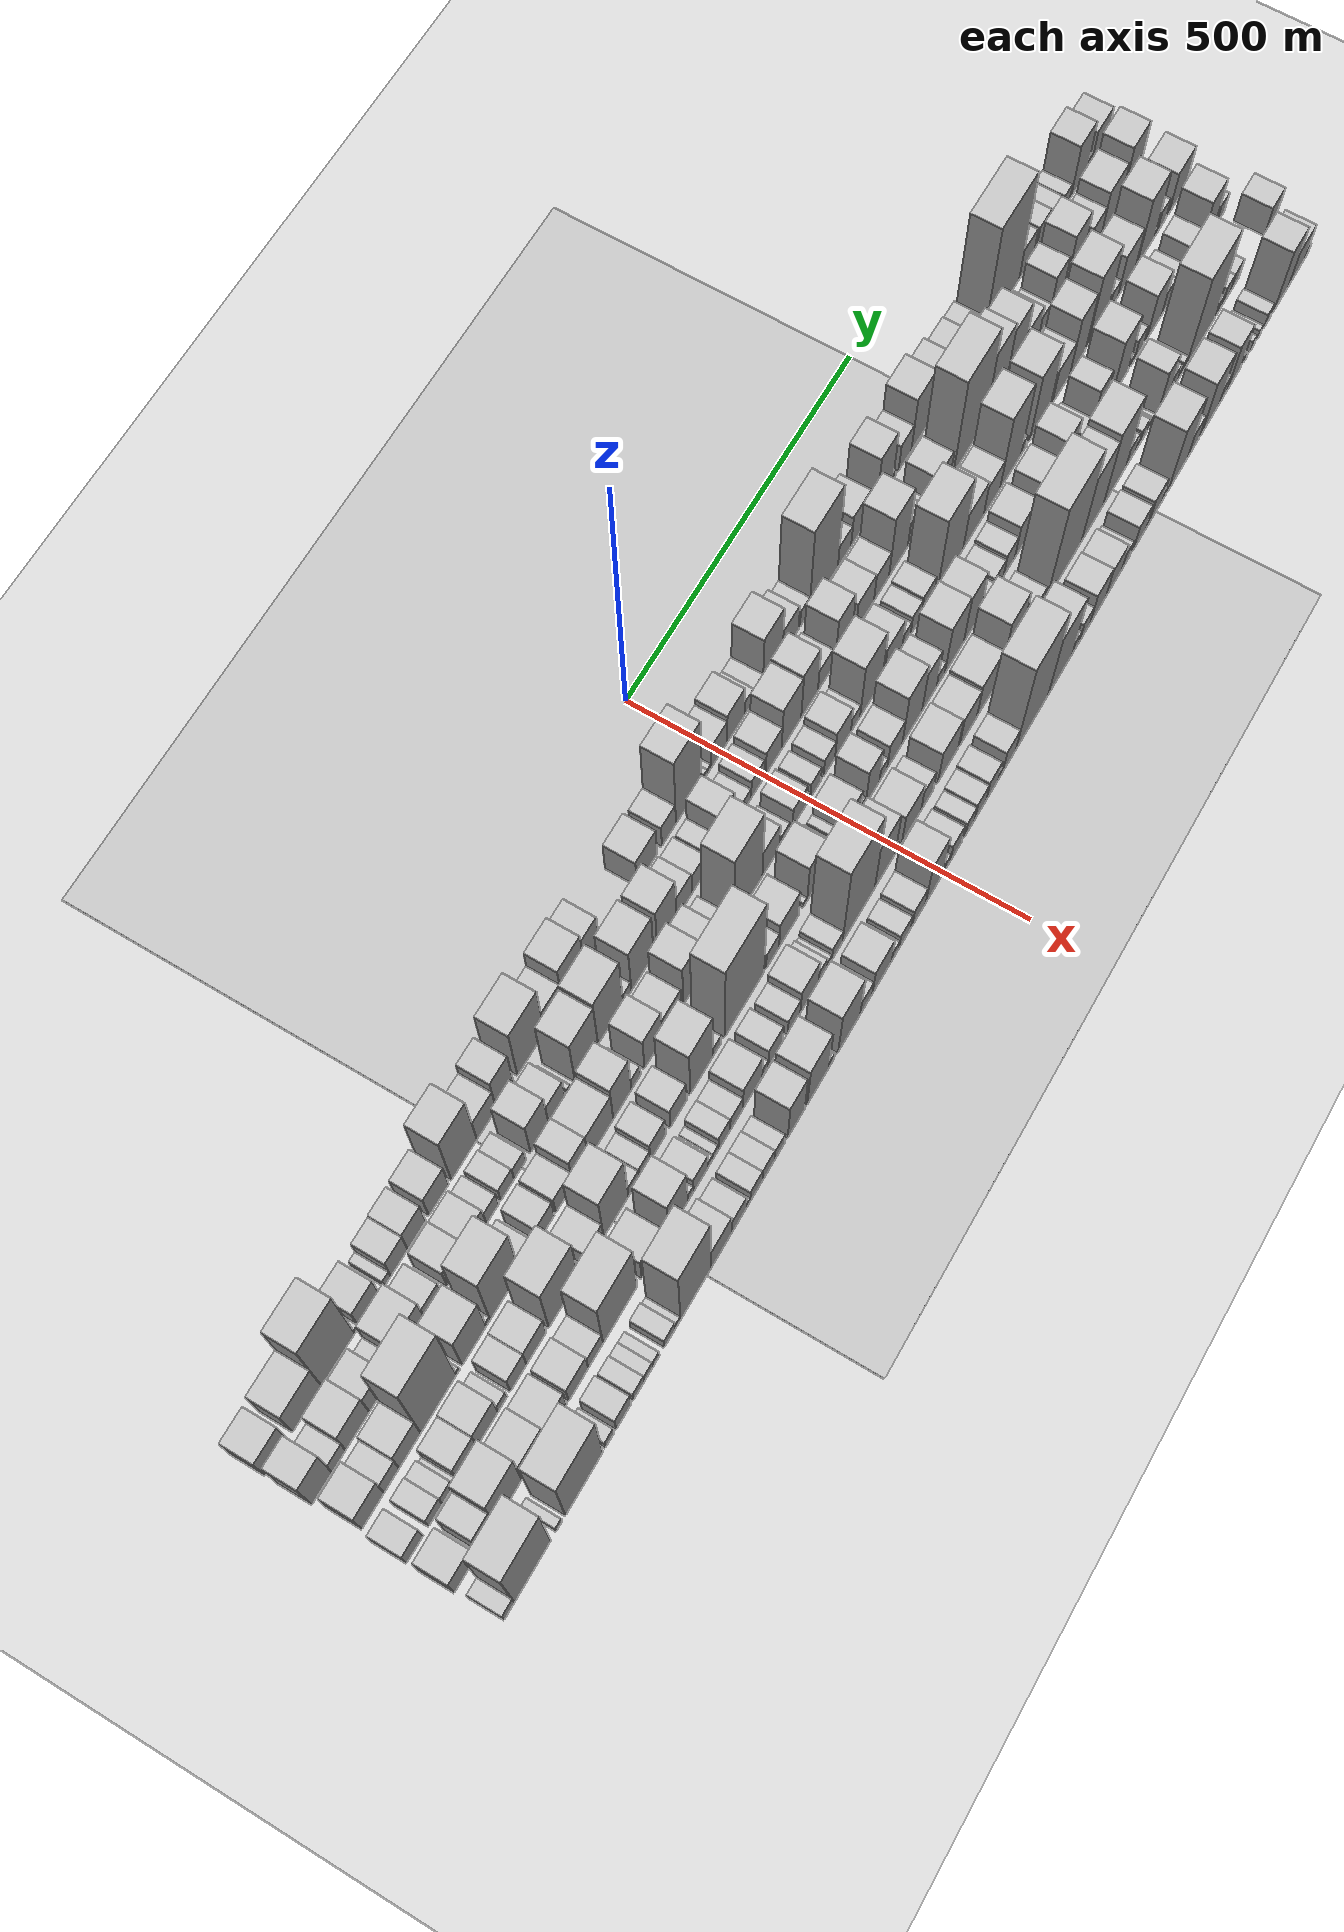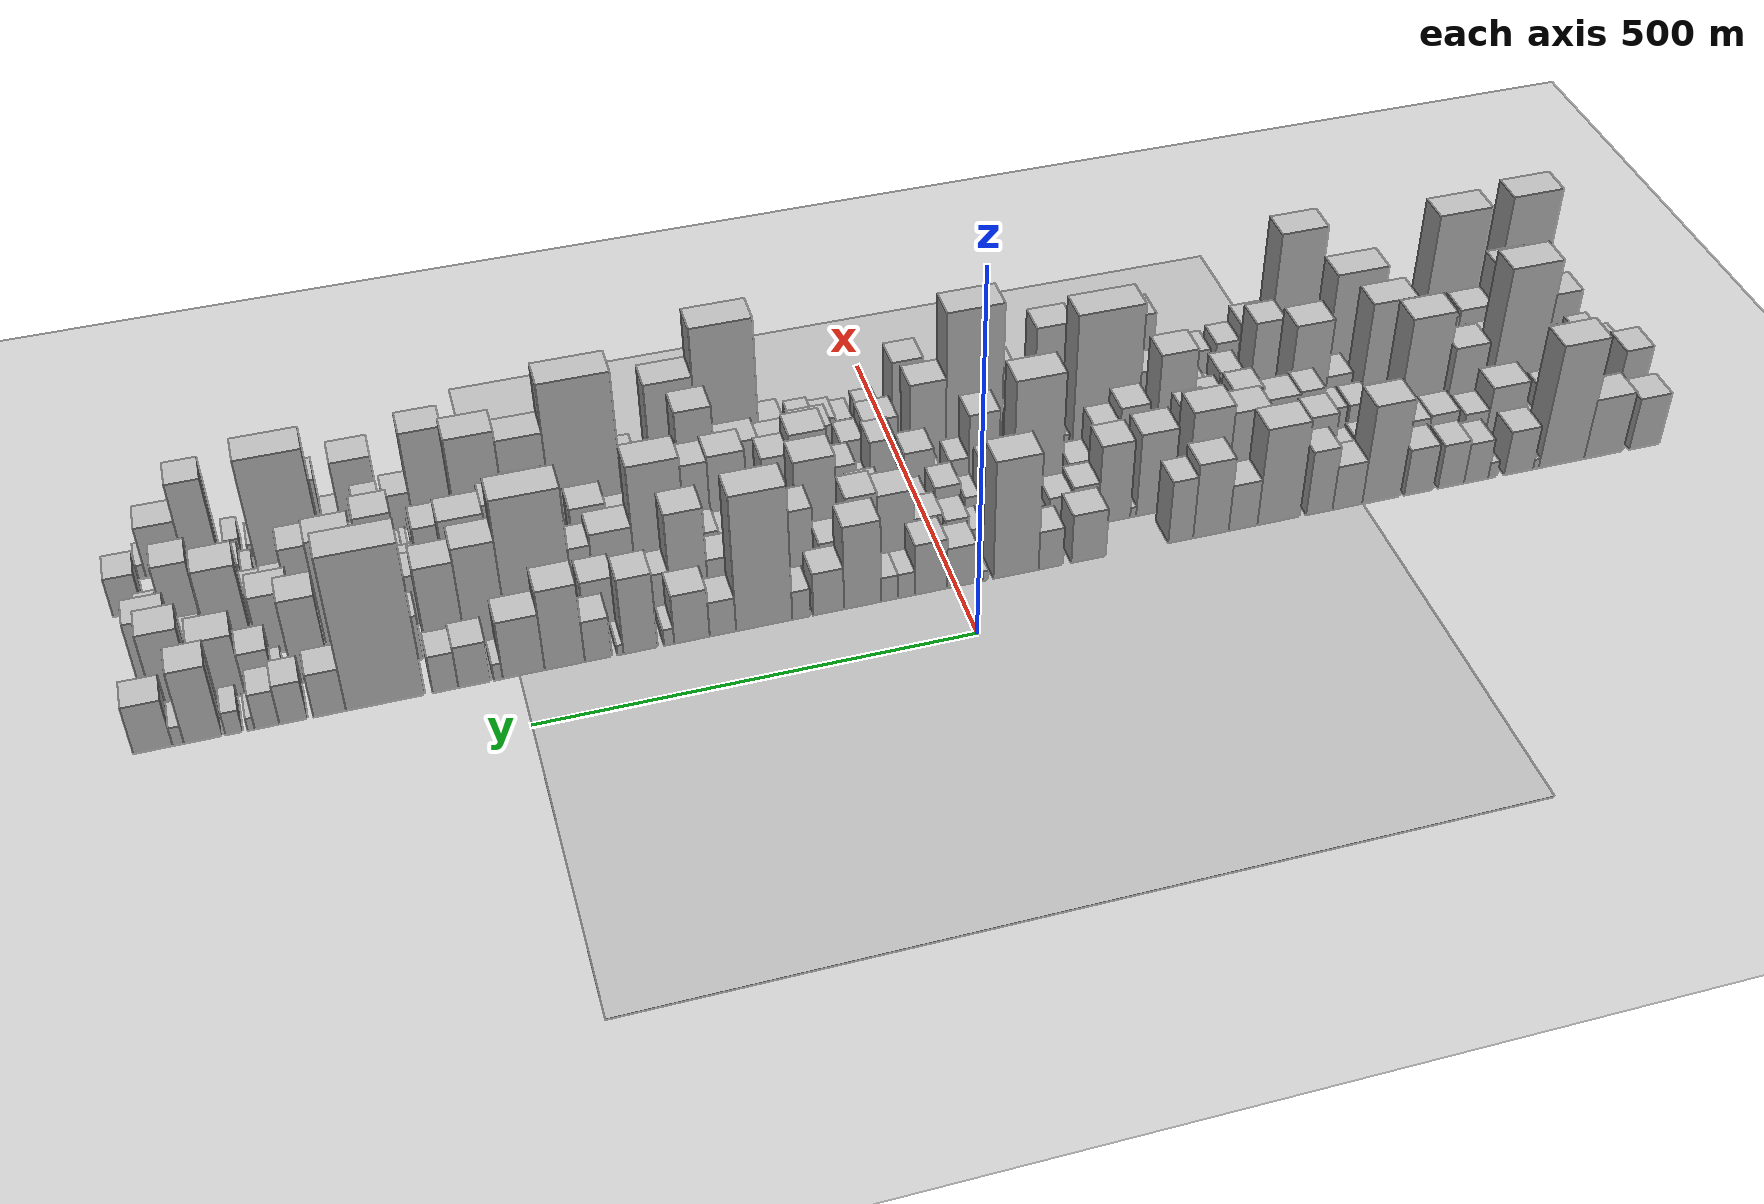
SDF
<?xml version="1.0" encoding="utf-8"?>

<sdf version="1.6">

   <world name="default">

      <gui fullscreen="0">

         <camera name="user_camera">

            <pose>-15 0 4.57585 0 0 0</pose>

            <view_controller>orbit</view_controller>

         </camera>

      </gui>

      <scene>

         <sky>

           <clouds>

             <speed>12</speed>

           </clouds>

         </sky>

         <ambient>0.4 0.4 0.4 1</ambient>

         <background>0.7 0.7 0.7 1</background>

         <shadows>1</shadows>

      </scene>

      <gravity>0 0 -9.8066</gravity>

      <magnetic_field>6e-06 2.3e-05 -4.2e-05</magnetic_field>

      <physics default="0" name="default_physics" type="ode">

         <ode>

            <solver>

               <type>quick</type>

               <iters>10</iters>

               <sor>1.0</sor>

               <use_dynamic_moi_rescaling>0</use_dynamic_moi_rescaling>

            </solver>

            <constraints>

               <cfm>0</cfm>

               <erp>0.2</erp>

               <contact_max_correcting_vel>100</contact_max_correcting_vel>

               <contact_surface_layer>0.001</contact_surface_layer>

            </constraints>

         </ode>

         <max_step_size>0.004</max_step_size>

         <real_time_factor>1</real_time_factor>

         <real_time_update_rate>250</real_time_update_rate>

      </physics>

      <light name="sun" type="directional">

         <cast_shadows>1</cast_shadows>

         <pose>0 0 10 0 0 0</pose>

         <diffuse>0.8 0.8 0.8 1</diffuse>

         <specular>0.2 0.2 0.2 1</specular>

         <attenuation>

            <range>1000</range>

            <constant>0.9</constant>

            <linear>0.01</linear>

            <quadratic>0.001</quadratic>

         </attenuation>

         <direction>-0.5 0.1 -0.9</direction>

      </light>

      <include>

         <name>ground_plane_1</name>

         <uri>model://HANNAS_ground_plane</uri>

         <pose>0 0 0  0 0 0</pose>

      </include>

      <include>

         <name>ground_plane_2</name>

         <uri>model://HANNAS_ground_plane</uri>

         <pose>100 0 0  0 0 0</pose>

      </include>

      <model name="building_1">

         <static>1</static>

         <pose frame="">100.0000 -869.5187 0 0.000000 0.000000 0.000000</pose>

         <link name="link">

            <pose frame="">0 0 39.00 0 0 0</pose>

            <collision name="collision">

               <geometry>

                  <box>

                     <size>40.0000 40.9626 78.0000</size>

                  </box>

               </geometry>

               <max_contacts>10</max_contacts>

               <surface>

                  <contact>

                     <ode/>

                  </contact>

                  <bounce/>

                  <friction>

                     <torsional>

                        <ode/>

                     </torsional>

                     <ode/>

                  </friction>

               </surface>

            </collision>

            <visual name="visual">

               <cast_shadows>0</cast_shadows>

               <geometry>

                  <box>

                     <size>40.0000 40.9626 78.0000</size>

                  </box>

               </geometry>

               <material>

                  <script>

                     <uri>model://HANNAS_wall/materials/scripts</uri>

                     <uri>model://HANNAS_wall/materials/textures</uri>

                     <name>vrc/HANNAS_wall</name>

                  </script>

               </material>

            </visual>

            <self_collide>0</self_collide>

            <enable_wind>0</enable_wind>

            <kinematic>0</kinematic>

         </link>

      </model>

      <model name="building_2">

         <static>1</static>

         <pose frame="">100.0000 -814.8399 0 0.000000 0.000000 0.000000</pose>

         <link name="link">

            <pose frame="">0 0 45.00 0 0 0</pose>

            <collision name="collision">

               <geometry>

                  <box>

                     <size>40.0000 52.3950 90.0000</size>

                  </box>

               </geometry>

               <max_contacts>10</max_contacts>

               <surface>

                  <contact>

                     <ode/>

                  </contact>

                  <bounce/>

                  <friction>

                     <torsional>

                        <ode/>

                     </torsional>

                     <ode/>

                  </friction>

               </surface>

            </collision>

            <visual name="visual">

               <cast_shadows>0</cast_shadows>

               <geometry>

                  <box>

                     <size>40.0000 52.3950 90.0000</size>

                  </box>

               </geometry>

               <material>

                  <script>

                     <uri>model://HANNAS_wall/materials/scripts</uri>

                     <uri>model://HANNAS_wall/materials/textures</uri>

                     <name>vrc/HANNAS_wall</name>

                  </script>

               </material>

            </visual>

            <self_collide>0</self_collide>

            <enable_wind>0</enable_wind>

            <kinematic>0</kinematic>

         </link>

      </model>

      <model name="building_3">

         <static>1</static>

         <pose frame="">100.0000 -758.5206 0 0.000000 0.000000 0.000000</pose>

         <link name="link">

            <pose frame="">0 0 91.50 0 0 0</pose>

            <collision name="collision">

               <geometry>

                  <box>

                     <size>40.0000 60.2436 183.0000</size>

                  </box>

               </geometry>

               <max_contacts>10</max_contacts>

               <surface>

                  <contact>

                     <ode/>

                  </contact>

                  <bounce/>

                  <friction>

                     <torsional>

                        <ode/>

                     </torsional>

                     <ode/>

                  </friction>

               </surface>

            </collision>

            <visual name="visual">

               <cast_shadows>0</cast_shadows>

               <geometry>

                  <box>

                     <size>40.0000 60.2436 183.0000</size>

                  </box>

               </geometry>

               <material>

                  <script>

                     <uri>model://HANNAS_wall/materials/scripts</uri>

                     <uri>model://HANNAS_wall/materials/textures</uri>

                     <name>vrc/HANNAS_wall</name>

                  </script>

               </material>

            </visual>

            <self_collide>0</self_collide>

            <enable_wind>0</enable_wind>

            <kinematic>0</kinematic>

         </link>

      </model>

      <model name="building_4">

         <static>1</static>

         <pose frame="">100.0000 -724.6863 0 0.000000 0.000000 0.000000</pose>

         <link name="link">

            <pose frame="">0 0 7.50 0 0 0</pose>

            <collision name="collision">

               <geometry>

                  <box>

                     <size>40.0000 7.4251 15.0000</size>

                  </box>

               </geometry>

               <max_contacts>10</max_contacts>

               <surface>

                  <contact>

                     <ode/>

                  </contact>

                  <bounce/>

                  <friction>

                     <torsional>

                        <ode/>

                     </torsional>

                     <ode/>

                  </friction>

               </surface>

            </collision>

            <visual name="visual">

               <cast_shadows>0</cast_shadows>

               <geometry>

                  <box>

                     <size>40.0000 7.4251 15.0000</size>

                  </box>

               </geometry>

               <material>

                  <script>

                     <uri>model://HANNAS_wall/materials/scripts</uri>

                     <uri>model://HANNAS_wall/materials/textures</uri>

                     <name>vrc/HANNAS_wall</name>

                  </script>

               </material>

            </visual>

            <self_collide>0</self_collide>

            <enable_wind>0</enable_wind>

            <kinematic>0</kinematic>

         </link>

      </model>

      <model name="building_5">

         <static>1</static>

         <pose frame="">100.0000 -701.8458 0 0.000000 0.000000 0.000000</pose>

         <link name="link">

            <pose frame="">0 0 33.00 0 0 0</pose>

            <collision name="collision">

               <geometry>

                  <box>

                     <size>40.0000 38.2559 66.0000</size>

                  </box>

               </geometry>

               <max_contacts>10</max_contacts>

               <surface>

                  <contact>

                     <ode/>

                  </contact>

                  <bounce/>

                  <friction>

                     <torsional>

                        <ode/>

                     </torsional>

                     <ode/>

                  </friction>

               </surface>

            </collision>

            <visual name="visual">

               <cast_shadows>0</cast_shadows>

               <geometry>

                  <box>

                     <size>40.0000 38.2559 66.0000</size>

                  </box>

               </geometry>

               <material>

                  <script>

                     <uri>model://HANNAS_wall/materials/scripts</uri>

                     <uri>model://HANNAS_wall/materials/textures</uri>

                     <name>vrc/HANNAS_wall</name>

                  </script>

               </material>

            </visual>

            <self_collide>0</self_collide>

            <enable_wind>0</enable_wind>

            <kinematic>0</kinematic>

         </link>

      </model>

      <model name="building_6">

         <static>1</static>

         <pose frame="">100.0000 -667.7672 0 0.000000 0.000000 0.000000</pose>

         <link name="link">

            <pose frame="">0 0 12.00 0 0 0</pose>

            <collision name="collision">

               <geometry>

                  <box>

                     <size>40.0000 11.9012 24.0000</size>

                  </box>

               </geometry>

               <max_contacts>10</max_contacts>

               <surface>

                  <contact>

                     <ode/>

                  </contact>

                  <bounce/>

                  <friction>

                     <torsional>

                        <ode/>

                     </torsional>

                     <ode/>

                  </friction>

               </surface>

            </collision>

            <visual name="visual">

               <cast_shadows>0</cast_shadows>

               <geometry>

                  <box>

                     <size>40.0000 11.9012 24.0000</size>

                  </box>

               </geometry>

               <material>

                  <script>

                     <uri>model://HANNAS_wall/materials/scripts</uri>

                     <uri>model://HANNAS_wall/materials/textures</uri>

                     <name>vrc/HANNAS_wall</name>

                  </script>

               </material>

            </visual>

            <self_collide>0</self_collide>

            <enable_wind>0</enable_wind>

            <kinematic>0</kinematic>

         </link>

      </model>

      <model name="building_7">

         <static>1</static>

         <pose frame="">100.0000 -646.0357 0 0.000000 0.000000 0.000000</pose>

         <link name="link">

            <pose frame="">0 0 30.00 0 0 0</pose>

            <collision name="collision">

               <geometry>

                  <box>

                     <size>40.0000 31.5618 60.0000</size>

                  </box>

               </geometry>

               <max_contacts>10</max_contacts>

               <surface>

                  <contact>

                     <ode/>

                  </contact>

                  <bounce/>

                  <friction>

                     <torsional>

                        <ode/>

                     </torsional>

                     <ode/>

                  </friction>

               </surface>

            </collision>

            <visual name="visual">

               <cast_shadows>0</cast_shadows>

               <geometry>

                  <box>

                     <size>40.0000 31.5618 60.0000</size>

                  </box>

               </geometry>

               <material>

                  <script>

                     <uri>model://HANNAS_wall/materials/scripts</uri>

                     <uri>model://HANNAS_wall/materials/textures</uri>

                     <name>vrc/HANNAS_wall</name>

                  </script>

               </material>

            </visual>

            <self_collide>0</self_collide>

            <enable_wind>0</enable_wind>

            <kinematic>0</kinematic>

         </link>

      </model>

      <model name="building_8">

         <static>1</static>

         <pose frame="">100.0000 -613.3074 0 0.000000 0.000000 0.000000</pose>

         <link name="link">

            <pose frame="">0 0 33.00 0 0 0</pose>

            <collision name="collision">

               <geometry>

                  <box>

                     <size>40.0000 33.8947 66.0000</size>

                  </box>

               </geometry>

               <max_contacts>10</max_contacts>

               <surface>

                  <contact>

                     <ode/>

                  </contact>

                  <bounce/>

                  <friction>

                     <torsional>

                        <ode/>

                     </torsional>

                     <ode/>

                  </friction>

               </surface>

            </collision>

            <visual name="visual">

               <cast_shadows>0</cast_shadows>

               <geometry>

                  <box>

                     <size>40.0000 33.8947 66.0000</size>

                  </box>

               </geometry>

               <material>

                  <script>

                     <uri>model://HANNAS_wall/materials/scripts</uri>

                     <uri>model://HANNAS_wall/materials/textures</uri>

                     <name>vrc/HANNAS_wall</name>

                  </script>

               </material>

            </visual>

            <self_collide>0</self_collide>

            <enable_wind>0</enable_wind>

            <kinematic>0</kinematic>

         </link>

      </model>

      <model name="building_9">

         <static>1</static>

         <pose frame="">100.0000 -571.5191 0 0.000000 0.000000 0.000000</pose>

         <link name="link">

            <pose frame="">0 0 34.50 0 0 0</pose>

            <collision name="collision">

               <geometry>

                  <box>

                     <size>40.0000 37.6818 69.0000</size>

                  </box>

               </geometry>

               <max_contacts>10</max_contacts>

               <surface>

                  <contact>

                     <ode/>

                  </contact>

                  <bounce/>

                  <friction>

                     <torsional>

                        <ode/>

                     </torsional>

                     <ode/>

                  </friction>

               </surface>

            </collision>

            <visual name="visual">

               <cast_shadows>0</cast_shadows>

               <geometry>

                  <box>

                     <size>40.0000 37.6818 69.0000</size>

                  </box>

               </geometry>

               <material>

                  <script>

                     <uri>model://HANNAS_wall/materials/scripts</uri>

                     <uri>model://HANNAS_wall/materials/textures</uri>

                     <name>vrc/HANNAS_wall</name>

                  </script>

               </material>

            </visual>

            <self_collide>0</self_collide>

            <enable_wind>0</enable_wind>

            <kinematic>0</kinematic>

         </link>

      </model>

      <model name="building_10">

         <static>1</static>

         <pose frame="">100.0000 -523.1911 0 0.000000 0.000000 0.000000</pose>

         <link name="link">

            <pose frame="">0 0 73.50 0 0 0</pose>

            <collision name="collision">

               <geometry>

                  <box>

                     <size>40.0000 48.9742 147.0000</size>

                  </box>

               </geometry>

               <max_contacts>10</max_contacts>

               <surface>

                  <contact>

                     <ode/>

                  </contact>

                  <bounce/>

                  <friction>

                     <torsional>

                        <ode/>

                     </torsional>

                     <ode/>

                  </friction>

               </surface>

            </collision>

            <visual name="visual">

               <cast_shadows>0</cast_shadows>

               <geometry>

                  <box>

                     <size>40.0000 48.9742 147.0000</size>

                  </box>

               </geometry>

               <material>

                  <script>

                     <uri>model://HANNAS_wall/materials/scripts</uri>

                     <uri>model://HANNAS_wall/materials/textures</uri>

                     <name>vrc/HANNAS_wall</name>

                  </script>

               </material>

            </visual>

            <self_collide>0</self_collide>

            <enable_wind>0</enable_wind>

            <kinematic>0</kinematic>

         </link>

      </model>

      <model name="building_11">

         <static>1</static>

         <pose frame="">100.0000 -479.7981 0 0.000000 0.000000 0.000000</pose>

         <link name="link">

            <pose frame="">0 0 33.00 0 0 0</pose>

            <collision name="collision">

               <geometry>

                  <box>

                     <size>40.0000 37.8118 66.0000</size>

                  </box>

               </geometry>

               <max_contacts>10</max_contacts>

               <surface>

                  <contact>

                     <ode/>

                  </contact>

                  <bounce/>

                  <friction>

                     <torsional>

                        <ode/>

                     </torsional>

                     <ode/>

                  </friction>

               </surface>

            </collision>

            <visual name="visual">

               <cast_shadows>0</cast_shadows>

               <geometry>

                  <box>

                     <size>40.0000 37.8118 66.0000</size>

                  </box>

               </geometry>

               <material>

                  <script>

                     <uri>model://HANNAS_wall/materials/scripts</uri>

                     <uri>model://HANNAS_wall/materials/textures</uri>

                     <name>vrc/HANNAS_wall</name>

                  </script>

               </material>

            </visual>

            <self_collide>0</self_collide>

            <enable_wind>0</enable_wind>

            <kinematic>0</kinematic>

         </link>

      </model>

      <model name="building_12">

         <static>1</static>

         <pose frame="">100.0000 -444.1729 0 0.000000 0.000000 0.000000</pose>

         <link name="link">

            <pose frame="">0 0 48.00 0 0 0</pose>

            <collision name="collision">

               <geometry>

                  <box>

                     <size>40.0000 33.4387 96.0000</size>

                  </box>

               </geometry>

               <max_contacts>10</max_contacts>

               <surface>

                  <contact>

                     <ode/>

                  </contact>

                  <bounce/>

                  <friction>

                     <torsional>

                        <ode/>

                     </torsional>

                     <ode/>

                  </friction>

               </surface>

            </collision>

            <visual name="visual">

               <cast_shadows>0</cast_shadows>

               <geometry>

                  <box>

                     <size>40.0000 33.4387 96.0000</size>

                  </box>

               </geometry>

               <material>

                  <script>

                     <uri>model://HANNAS_wall/materials/scripts</uri>

                     <uri>model://HANNAS_wall/materials/textures</uri>

                     <name>vrc/HANNAS_wall</name>

                  </script>

               </material>

            </visual>

            <self_collide>0</self_collide>

            <enable_wind>0</enable_wind>

            <kinematic>0</kinematic>

         </link>

      </model>

      <model name="building_13">

         <static>1</static>

         <pose frame="">100.0000 -392.7377 0 0.000000 0.000000 0.000000</pose>

         <link name="link">

            <pose frame="">0 0 72.00 0 0 0</pose>

            <collision name="collision">

               <geometry>

                  <box>

                     <size>40.0000 53.4315 144.0000</size>

                  </box>

               </geometry>

               <max_contacts>10</max_contacts>

               <surface>

                  <contact>

                     <ode/>

                  </contact>

                  <bounce/>

                  <friction>

                     <torsional>

                        <ode/>

                     </torsional>

                     <ode/>

                  </friction>

               </surface>

            </collision>

            <visual name="visual">

               <cast_shadows>0</cast_shadows>

               <geometry>

                  <box>

                     <size>40.0000 53.4315 144.0000</size>

                  </box>

               </geometry>

               <material>

                  <script>

                     <uri>model://HANNAS_wall/materials/scripts</uri>

                     <uri>model://HANNAS_wall/materials/textures</uri>

                     <name>vrc/HANNAS_wall</name>

                  </script>

               </material>

            </visual>

            <self_collide>0</self_collide>

            <enable_wind>0</enable_wind>

            <kinematic>0</kinematic>

         </link>

      </model>

      <model name="building_14">

         <static>1</static>

         <pose frame="">100.0000 -348.0701 0 0.000000 0.000000 0.000000</pose>

         <link name="link">

            <pose frame="">0 0 34.50 0 0 0</pose>

            <collision name="collision">

               <geometry>

                  <box>

                     <size>40.0000 35.9037 69.0000</size>

                  </box>

               </geometry>

               <max_contacts>10</max_contacts>

               <surface>

                  <contact>

                     <ode/>

                  </contact>

                  <bounce/>

                  <friction>

                     <torsional>

                        <ode/>

                     </torsional>

                     <ode/>

                  </friction>

               </surface>

            </collision>

            <visual name="visual">

               <cast_shadows>0</cast_shadows>

               <geometry>

                  <box>

                     <size>40.0000 35.9037 69.0000</size>

                  </box>

               </geometry>

               <material>

                  <script>

                     <uri>model://HANNAS_wall/materials/scripts</uri>

                     <uri>model://HANNAS_wall/materials/textures</uri>

                     <name>vrc/HANNAS_wall</name>

                  </script>

               </material>

            </visual>

            <self_collide>0</self_collide>

            <enable_wind>0</enable_wind>

            <kinematic>0</kinematic>

         </link>

      </model>

      <model name="building_15">

         <static>1</static>

         <pose frame="">100.0000 -308.0212 0 0.000000 0.000000 0.000000</pose>

         <link name="link">

            <pose frame="">0 0 55.50 0 0 0</pose>

            <collision name="collision">

               <geometry>

                  <box>

                     <size>40.0000 44.1941 111.0000</size>

                  </box>

               </geometry>

               <max_contacts>10</max_contacts>

               <surface>

                  <contact>

                     <ode/>

                  </contact>

                  <bounce/>

                  <friction>

                     <torsional>

                        <ode/>

                     </torsional>

                     <ode/>

                  </friction>

               </surface>

            </collision>

            <visual name="visual">

               <cast_shadows>0</cast_shadows>

               <geometry>

                  <box>

                     <size>40.0000 44.1941 111.0000</size>

                  </box>

               </geometry>

               <material>

                  <script>

                     <uri>model://HANNAS_wall/materials/scripts</uri>

                     <uri>model://HANNAS_wall/materials/textures</uri>

                     <name>vrc/HANNAS_wall</name>

                  </script>

               </material>

            </visual>

            <self_collide>0</self_collide>

            <enable_wind>0</enable_wind>

            <kinematic>0</kinematic>

         </link>

      </model>

      <model name="building_16">

         <static>1</static>

         <pose frame="">100.0000 -270.5389 0 0.000000 0.000000 0.000000</pose>

         <link name="link">

            <pose frame="">0 0 46.50 0 0 0</pose>

            <collision name="collision">

               <geometry>

                  <box>

                     <size>40.0000 30.7704 93.0000</size>

                  </box>

               </geometry>

               <max_contacts>10</max_contacts>

               <surface>

                  <contact>

                     <ode/>

                  </contact>

                  <bounce/>

                  <friction>

                     <torsional>

                        <ode/>

                     </torsional>

                     <ode/>

                  </friction>

               </surface>

            </collision>

            <visual name="visual">

               <cast_shadows>0</cast_shadows>

               <geometry>

                  <box>

                     <size>40.0000 30.7704 93.0000</size>

                  </box>

               </geometry>

               <material>

                  <script>

                     <uri>model://HANNAS_wall/materials/scripts</uri>

                     <uri>model://HANNAS_wall/materials/textures</uri>

                     <name>vrc/HANNAS_wall</name>

                  </script>

               </material>

            </visual>

            <self_collide>0</self_collide>

            <enable_wind>0</enable_wind>

            <kinematic>0</kinematic>

         </link>

      </model>

      <model name="building_17">

         <static>1</static>

         <pose frame="">100.0000 -157.5000 0 0.000000 0.000000 0.000000</pose>

         <link name="link">

            <pose frame="">0 0 36.00 0 0 0</pose>

            <collision name="collision">

               <geometry>

                  <box>

                     <size>40.0000 41.7692 72.0000</size>

                  </box>

               </geometry>

               <max_contacts>10</max_contacts>

               <surface>

                  <contact>

                     <ode/>

                  </contact>

                  <bounce/>

                  <friction>

                     <torsional>

                        <ode/>

                     </torsional>

                     <ode/>

                  </friction>

               </surface>

            </collision>

            <visual name="visual">

               <cast_shadows>0</cast_shadows>

               <geometry>

                  <box>

                     <size>40.0000 41.7692 72.0000</size>

                  </box>

               </geometry>

               <material>

                  <script>

                     <uri>model://HANNAS_wall/materials/scripts</uri>

                     <uri>model://HANNAS_wall/materials/textures</uri>

                     <name>vrc/HANNAS_wall</name>

                  </script>

               </material>

            </visual>

            <self_collide>0</self_collide>

            <enable_wind>0</enable_wind>

            <kinematic>0</kinematic>

         </link>

      </model>

      <model name="building_18">

         <static>1</static>

         <pose frame="">100.0000 -111.8447 0 0.000000 0.000000 0.000000</pose>

         <link name="link">

            <pose frame="">0 0 28.50 0 0 0</pose>

            <collision name="collision">

               <geometry>

                  <box>

                     <size>40.0000 29.5414 57.0000</size>

                  </box>

               </geometry>

               <max_contacts>10</max_contacts>

               <surface>

                  <contact>

                     <ode/>

                  </contact>

                  <bounce/>

                  <friction>

                     <torsional>

                        <ode/>

                     </torsional>

                     <ode/>

                  </friction>

               </surface>

            </collision>

            <visual name="visual">

               <cast_shadows>0</cast_shadows>

               <geometry>

                  <box>

                     <size>40.0000 29.5414 57.0000</size>

                  </box>

               </geometry>

               <material>

                  <script>

                     <uri>model://HANNAS_wall/materials/scripts</uri>

                     <uri>model://HANNAS_wall/materials/textures</uri>

                     <name>vrc/HANNAS_wall</name>

                  </script>

               </material>

            </visual>

            <self_collide>0</self_collide>

            <enable_wind>0</enable_wind>

            <kinematic>0</kinematic>

         </link>

      </model>

      <model name="building_19">

         <static>1</static>

         <pose frame="">100.0000 -69.9653 0 0.000000 0.000000 0.000000</pose>

         <link name="link">

            <pose frame="">0 0 87.00 0 0 0</pose>

            <collision name="collision">

               <geometry>

                  <box>

                     <size>40.0000 54.2176 174.0000</size>

                  </box>

               </geometry>

               <max_contacts>10</max_contacts>

               <surface>

                  <contact>

                     <ode/>

                  </contact>

                  <bounce/>

                  <friction>

                     <torsional>

                        <ode/>

                     </torsional>

                     <ode/>

                  </friction>

               </surface>

            </collision>

            <visual name="visual">

               <cast_shadows>0</cast_shadows>

               <geometry>

                  <box>

                     <size>40.0000 54.2176 174.0000</size>

                  </box>

               </geometry>

               <material>

                  <script>

                     <uri>model://HANNAS_wall/materials/scripts</uri>

                     <uri>model://HANNAS_wall/materials/textures</uri>

                     <name>vrc/HANNAS_wall</name>

                  </script>

               </material>

            </visual>

            <self_collide>0</self_collide>

            <enable_wind>0</enable_wind>

            <kinematic>0</kinematic>

         </link>

      </model>

      <model name="building_20">

         <static>1</static>

         <pose frame="">100.0000 -33.4122 0 0.000000 0.000000 0.000000</pose>

         <link name="link">

            <pose frame="">0 0 7.50 0 0 0</pose>

            <collision name="collision">

               <geometry>

                  <box>

                     <size>40.0000 6.8886 15.0000</size>

                  </box>

               </geometry>

               <max_contacts>10</max_contacts>

               <surface>

                  <contact>

                     <ode/>

                  </contact>

                  <bounce/>

                  <friction>

                     <torsional>

                        <ode/>

                     </torsional>

                     <ode/>

                  </friction>

               </surface>

            </collision>

            <visual name="visual">

               <cast_shadows>0</cast_shadows>

               <geometry>

                  <box>

                     <size>40.0000 6.8886 15.0000</size>

                  </box>

               </geometry>

               <material>

                  <script>

                     <uri>model://HANNAS_wall/materials/scripts</uri>

                     <uri>model://HANNAS_wall/materials/textures</uri>

                     <name>vrc/HANNAS_wall</name>

                  </script>

               </material>

            </visual>

            <self_collide>0</self_collide>

            <enable_wind>0</enable_wind>

            <kinematic>0</kinematic>

         </link>

      </model>

      <model name="building_21">

         <static>1</static>

         <pose frame="">100.0000 -26.3233 0 0.000000 0.000000 0.000000</pose>

         <link name="link">

            <pose frame="">0 0 7.50 0 0 0</pose>

            <collision name="collision">

               <geometry>

                  <box>

                     <size>40.0000 7.2892 15.0000</size>

                  </box>

               </geometry>

               <max_contacts>10</max_contacts>

               <surface>

                  <contact>

                     <ode/>

                  </contact>

                  <bounce/>

                  <friction>

                     <torsional>

                        <ode/>

                     </torsional>

                     <ode/>

                  </friction>

               </surface>

            </collision>

            <visual name="visual">

               <cast_shadows>0</cast_shadows>

               <geometry>

                  <box>

                     <size>40.0000 7.2892 15.0000</size>

                  </box>

               </geometry>

               <material>

                  <script>

                     <uri>model://HANNAS_wall/materials/scripts</uri>

                     <uri>model://HANNAS_wall/materials/textures</uri>

                     <name>vrc/HANNAS_wall</name>

                  </script>

               </material>

            </visual>

            <self_collide>0</self_collide>

            <enable_wind>0</enable_wind>

            <kinematic>0</kinematic>

         </link>

      </model>

      <model name="building_22">

         <static>1</static>

         <pose frame="">100.0000 -5.1696 0 0.000000 0.000000 0.000000</pose>

         <link name="link">

            <pose frame="">0 0 30.00 0 0 0</pose>

            <collision name="collision">

               <geometry>

                  <box>

                     <size>40.0000 35.0181 60.0000</size>

                  </box>

               </geometry>

               <max_contacts>10</max_contacts>

               <surface>

                  <contact>

                     <ode/>

                  </contact>

                  <bounce/>

                  <friction>

                     <torsional>

                        <ode/>

                     </torsional>

                     <ode/>

                  </friction>

               </surface>

            </collision>

            <visual name="visual">

               <cast_shadows>0</cast_shadows>

               <geometry>

                  <box>

                     <size>40.0000 35.0181 60.0000</size>

                  </box>

               </geometry>

               <material>

                  <script>

                     <uri>model://HANNAS_wall/materials/scripts</uri>

                     <uri>model://HANNAS_wall/materials/textures</uri>

                     <name>vrc/HANNAS_wall</name>

                  </script>

               </material>

            </visual>

            <self_collide>0</self_collide>

            <enable_wind>0</enable_wind>

            <kinematic>0</kinematic>

         </link>

      </model>

      <model name="building_23">

         <static>1</static>

         <pose frame="">100.0000 31.2205 0 0.000000 0.000000 0.000000</pose>

         <link name="link">

            <pose frame="">0 0 37.50 0 0 0</pose>

            <collision name="collision">

               <geometry>

                  <box>

                     <size>40.0000 37.7620 75.0000</size>

                  </box>

               </geometry>

               <max_contacts>10</max_contacts>

               <surface>

                  <contact>

                     <ode/>

                  </contact>

                  <bounce/>

                  <friction>

                     <torsional>

                        <ode/>

                     </torsional>

                     <ode/>

                  </friction>

               </surface>

            </collision>

            <visual name="visual">

               <cast_shadows>0</cast_shadows>

               <geometry>

                  <box>

                     <size>40.0000 37.7620 75.0000</size>

                  </box>

               </geometry>

               <material>

                  <script>

                     <uri>model://HANNAS_wall/materials/scripts</uri>

                     <uri>model://HANNAS_wall/materials/textures</uri>

                     <name>vrc/HANNAS_wall</name>

                  </script>

               </material>

            </visual>

            <self_collide>0</self_collide>

            <enable_wind>0</enable_wind>

            <kinematic>0</kinematic>

         </link>

      </model>

      <model name="building_24">

         <static>1</static>

         <pose frame="">100.0000 59.9034 0 0.000000 0.000000 0.000000</pose>

         <link name="link">

            <pose frame="">0 0 18.00 0 0 0</pose>

            <collision name="collision">

               <geometry>

                  <box>

                     <size>40.0000 19.6038 36.0000</size>

                  </box>

               </geometry>

               <max_contacts>10</max_contacts>

               <surface>

                  <contact>

                     <ode/>

                  </contact>

                  <bounce/>

                  <friction>

                     <torsional>

                        <ode/>

                     </torsional>

                     <ode/>

                  </friction>

               </surface>

            </collision>

            <visual name="visual">

               <cast_shadows>0</cast_shadows>

               <geometry>

                  <box>

                     <size>40.0000 19.6038 36.0000</size>

                  </box>

               </geometry>

               <material>

                  <script>

                     <uri>model://HANNAS_wall/materials/scripts</uri>

                     <uri>model://HANNAS_wall/materials/textures</uri>

                     <name>vrc/HANNAS_wall</name>

                  </script>

               </material>

            </visual>

            <self_collide>0</self_collide>

            <enable_wind>0</enable_wind>

            <kinematic>0</kinematic>

         </link>

      </model>

      <model name="building_25">

         <static>1</static>

         <pose frame="">100.0000 79.6964 0 0.000000 0.000000 0.000000</pose>

         <link name="link">

            <pose frame="">0 0 18.00 0 0 0</pose>

            <collision name="collision">

               <geometry>

                  <box>

                     <size>40.0000 19.9822 36.0000</size>

                  </box>

               </geometry>

               <max_contacts>10</max_contacts>

               <surface>

                  <contact>

                     <ode/>

                  </contact>

                  <bounce/>

                  <friction>

                     <torsional>

                        <ode/>

                     </torsional>

                     <ode/>

                  </friction>

               </surface>

            </collision>

            <visual name="visual">

               <cast_shadows>0</cast_shadows>

               <geometry>

                  <box>

                     <size>40.0000 19.9822 36.0000</size>

                  </box>

               </geometry>

               <material>

                  <script>

                     <uri>model://HANNAS_wall/materials/scripts</uri>

                     <uri>model://HANNAS_wall/materials/textures</uri>

                     <name>vrc/HANNAS_wall</name>

                  </script>

               </material>

            </visual>

            <self_collide>0</self_collide>

            <enable_wind>0</enable_wind>

            <kinematic>0</kinematic>

         </link>

      </model>

      <model name="building_26">

         <static>1</static>

         <pose frame="">100.0000 111.3581 0 0.000000 0.000000 0.000000</pose>

         <link name="link">

            <pose frame="">0 0 61.50 0 0 0</pose>

            <collision name="collision">

               <geometry>

                  <box>

                     <size>40.0000 43.3412 123.0000</size>

                  </box>

               </geometry>

               <max_contacts>10</max_contacts>

               <surface>

                  <contact>

                     <ode/>

                  </contact>

                  <bounce/>

                  <friction>

                     <torsional>

                        <ode/>

                     </torsional>

                     <ode/>

                  </friction>

               </surface>

            </collision>

            <visual name="visual">

               <cast_shadows>0</cast_shadows>

               <geometry>

                  <box>

                     <size>40.0000 43.3412 123.0000</size>

                  </box>

               </geometry>

               <material>

                  <script>

                     <uri>model://HANNAS_wall/materials/scripts</uri>

                     <uri>model://HANNAS_wall/materials/textures</uri>

                     <name>vrc/HANNAS_wall</name>

                  </script>

               </material>

            </visual>

            <self_collide>0</self_collide>

            <enable_wind>0</enable_wind>

            <kinematic>0</kinematic>

         </link>

      </model>

      <model name="building_27">

         <static>1</static>

         <pose frame="">100.0000 150.9429 0 0.000000 0.000000 0.000000</pose>

         <link name="link">

            <pose frame="">0 0 31.50 0 0 0</pose>

            <collision name="collision">

               <geometry>

                  <box>

                     <size>40.0000 35.8284 63.0000</size>

                  </box>

               </geometry>

               <max_contacts>10</max_contacts>

               <surface>

                  <contact>

                     <ode/>

                  </contact>

                  <bounce/>

                  <friction>

                     <torsional>

                        <ode/>

                     </torsional>

                     <ode/>

                  </friction>

               </surface>

            </collision>

            <visual name="visual">

               <cast_shadows>0</cast_shadows>

               <geometry>

                  <box>

                     <size>40.0000 35.8284 63.0000</size>

                  </box>

               </geometry>

               <material>

                  <script>

                     <uri>model://HANNAS_wall/materials/scripts</uri>

                     <uri>model://HANNAS_wall/materials/textures</uri>

                     <name>vrc/HANNAS_wall</name>

                  </script>

               </material>

            </visual>

            <self_collide>0</self_collide>

            <enable_wind>0</enable_wind>

            <kinematic>0</kinematic>

         </link>

      </model>

      <model name="building_28">

         <static>1</static>

         <pose frame="">100.0000 182.4115 0 0.000000 0.000000 0.000000</pose>

         <link name="link">

            <pose frame="">0 0 21.00 0 0 0</pose>

            <collision name="collision">

               <geometry>

                  <box>

                     <size>40.0000 21.1088 42.0000</size>

                  </box>

               </geometry>

               <max_contacts>10</max_contacts>

               <surface>

                  <contact>

                     <ode/>

                  </contact>

                  <bounce/>

                  <friction>

                     <torsional>

                        <ode/>

                     </torsional>

                     <ode/>

                  </friction>

               </surface>

            </collision>

            <visual name="visual">

               <cast_shadows>0</cast_shadows>

               <geometry>

                  <box>

                     <size>40.0000 21.1088 42.0000</size>

                  </box>

               </geometry>

               <material>

                  <script>

                     <uri>model://HANNAS_wall/materials/scripts</uri>

                     <uri>model://HANNAS_wall/materials/textures</uri>

                     <name>vrc/HANNAS_wall</name>

                  </script>

               </material>

            </visual>

            <self_collide>0</self_collide>

            <enable_wind>0</enable_wind>

            <kinematic>0</kinematic>

         </link>

      </model>

      <model name="building_29">

         <static>1</static>

         <pose frame="">100.0000 225.2210 0 0.000000 0.000000 0.000000</pose>

         <link name="link">

            <pose frame="">0 0 99.00 0 0 0</pose>

            <collision name="collision">

               <geometry>

                  <box>

                     <size>40.0000 64.5103 198.0000</size>

                  </box>

               </geometry>

               <max_contacts>10</max_contacts>

               <surface>

                  <contact>

                     <ode/>

                  </contact>

                  <bounce/>

                  <friction>

                     <torsional>

                        <ode/>

                     </torsional>

                     <ode/>

                  </friction>

               </surface>

            </collision>

            <visual name="visual">

               <cast_shadows>0</cast_shadows>

               <geometry>

                  <box>

                     <size>40.0000 64.5103 198.0000</size>

                  </box>

               </geometry>

               <material>

                  <script>

                     <uri>model://HANNAS_wall/materials/scripts</uri>

                     <uri>model://HANNAS_wall/materials/textures</uri>

                     <name>vrc/HANNAS_wall</name>

                  </script>

               </material>

            </visual>

            <self_collide>0</self_collide>

            <enable_wind>0</enable_wind>

            <kinematic>0</kinematic>

         </link>

      </model>

      <model name="building_30">

         <static>1</static>

         <pose frame="">100.0000 272.4925 0 0.000000 0.000000 0.000000</pose>

         <link name="link">

            <pose frame="">0 0 25.50 0 0 0</pose>

            <collision name="collision">

               <geometry>

                  <box>

                     <size>40.0000 30.0327 51.0000</size>

                  </box>

               </geometry>

               <max_contacts>10</max_contacts>

               <surface>

                  <contact>

                     <ode/>

                  </contact>

                  <bounce/>

                  <friction>

                     <torsional>

                        <ode/>

                     </torsional>

                     <ode/>

                  </friction>

               </surface>

            </collision>

            <visual name="visual">

               <cast_shadows>0</cast_shadows>

               <geometry>

                  <box>

                     <size>40.0000 30.0327 51.0000</size>

                  </box>

               </geometry>

               <material>

                  <script>

                     <uri>model://HANNAS_wall/materials/scripts</uri>

                     <uri>model://HANNAS_wall/materials/textures</uri>

                     <name>vrc/HANNAS_wall</name>

                  </script>

               </material>

            </visual>

            <self_collide>0</self_collide>

            <enable_wind>0</enable_wind>

            <kinematic>0</kinematic>

         </link>

      </model>

      <model name="building_31">

         <static>1</static>

         <pose frame="">100.0000 307.5906 0 0.000000 0.000000 0.000000</pose>

         <link name="link">

            <pose frame="">0 0 36.00 0 0 0</pose>

            <collision name="collision">

               <geometry>

                  <box>

                     <size>40.0000 40.1634 72.0000</size>

                  </box>

               </geometry>

               <max_contacts>10</max_contacts>

               <surface>

                  <contact>

                     <ode/>

                  </contact>

                  <bounce/>

                  <friction>

                     <torsional>

                        <ode/>

                     </torsional>

                     <ode/>

                  </friction>

               </surface>

            </collision>

            <visual name="visual">

               <cast_shadows>0</cast_shadows>

               <geometry>

                  <box>

                     <size>40.0000 40.1634 72.0000</size>

                  </box>

               </geometry>

               <material>

                  <script>

                     <uri>model://HANNAS_wall/materials/scripts</uri>

                     <uri>model://HANNAS_wall/materials/textures</uri>

                     <name>vrc/HANNAS_wall</name>

                  </script>

               </material>

            </visual>

            <self_collide>0</self_collide>

            <enable_wind>0</enable_wind>

            <kinematic>0</kinematic>

         </link>

      </model>

      <model name="building_32">

         <static>1</static>

         <pose frame="">100.0000 333.4766 0 0.000000 0.000000 0.000000</pose>

         <link name="link">

            <pose frame="">0 0 12.00 0 0 0</pose>

            <collision name="collision">

               <geometry>

                  <box>

                     <size>40.0000 11.6085 24.0000</size>

                  </box>

               </geometry>

               <max_contacts>10</max_contacts>

               <surface>

                  <contact>

                     <ode/>

                  </contact>

                  <bounce/>

                  <friction>

                     <torsional>

                        <ode/>

                     </torsional>

                     <ode/>

                  </friction>

               </surface>

            </collision>

            <visual name="visual">

               <cast_shadows>0</cast_shadows>

               <geometry>

                  <box>

                     <size>40.0000 11.6085 24.0000</size>

                  </box>

               </geometry>

               <material>

                  <script>

                     <uri>model://HANNAS_wall/materials/scripts</uri>

                     <uri>model://HANNAS_wall/materials/textures</uri>

                     <name>vrc/HANNAS_wall</name>

                  </script>

               </material>

            </visual>

            <self_collide>0</self_collide>

            <enable_wind>0</enable_wind>

            <kinematic>0</kinematic>

         </link>

      </model>

      <model name="building_33">

         <static>1</static>

         <pose frame="">100.0000 365.5160 0 0.000000 0.000000 0.000000</pose>

         <link name="link">

            <pose frame="">0 0 55.50 0 0 0</pose>

            <collision name="collision">

               <geometry>

                  <box>

                     <size>40.0000 38.4703 111.0000</size>

                  </box>

               </geometry>

               <max_contacts>10</max_contacts>

               <surface>

                  <contact>

                     <ode/>

                  </contact>

                  <bounce/>

                  <friction>

                     <torsional>

                        <ode/>

                     </torsional>

                     <ode/>

                  </friction>

               </surface>

            </collision>

            <visual name="visual">

               <cast_shadows>0</cast_shadows>

               <geometry>

                  <box>

                     <size>40.0000 38.4703 111.0000</size>

                  </box>

               </geometry>

               <material>

                  <script>

                     <uri>model://HANNAS_wall/materials/scripts</uri>

                     <uri>model://HANNAS_wall/materials/textures</uri>

                     <name>vrc/HANNAS_wall</name>

                  </script>

               </material>

            </visual>

            <self_collide>0</self_collide>

            <enable_wind>0</enable_wind>

            <kinematic>0</kinematic>

         </link>

      </model>

      <model name="building_34">

         <static>1</static>

         <pose frame="">100.0000 388.1148 0 0.000000 0.000000 0.000000</pose>

         <link name="link">

            <pose frame="">0 0 7.50 0 0 0</pose>

            <collision name="collision">

               <geometry>

                  <box>

                     <size>40.0000 6.7272 15.0000</size>

                  </box>

               </geometry>

               <max_contacts>10</max_contacts>

               <surface>

                  <contact>

                     <ode/>

                  </contact>

                  <bounce/>

                  <friction>

                     <torsional>

                        <ode/>

                     </torsional>

                     <ode/>

                  </friction>

               </surface>

            </collision>

            <visual name="visual">

               <cast_shadows>0</cast_shadows>

               <geometry>

                  <box>

                     <size>40.0000 6.7272 15.0000</size>

                  </box>

               </geometry>

               <material>

                  <script>

                     <uri>model://HANNAS_wall/materials/scripts</uri>

                     <uri>model://HANNAS_wall/materials/textures</uri>

                     <name>vrc/HANNAS_wall</name>

                  </script>

               </material>

            </visual>

            <self_collide>0</self_collide>

            <enable_wind>0</enable_wind>

            <kinematic>0</kinematic>

         </link>

      </model>

      <model name="building_35">

         <static>1</static>

         <pose frame="">100.0000 412.5603 0 0.000000 0.000000 0.000000</pose>

         <link name="link">

            <pose frame="">0 0 30.00 0 0 0</pose>

            <collision name="collision">

               <geometry>

                  <box>

                     <size>40.0000 30.1639 60.0000</size>

                  </box>

               </geometry>

               <max_contacts>10</max_contacts>

               <surface>

                  <contact>

                     <ode/>

                  </contact>

                  <bounce/>

                  <friction>

                     <torsional>

                        <ode/>

                     </torsional>

                     <ode/>

                  </friction>

               </surface>

            </collision>

            <visual name="visual">

               <cast_shadows>0</cast_shadows>

               <geometry>

                  <box>

                     <size>40.0000 30.1639 60.0000</size>

                  </box>

               </geometry>

               <material>

                  <script>

                     <uri>model://HANNAS_wall/materials/scripts</uri>

                     <uri>model://HANNAS_wall/materials/textures</uri>

                     <name>vrc/HANNAS_wall</name>

                  </script>

               </material>

            </visual>

            <self_collide>0</self_collide>

            <enable_wind>0</enable_wind>

            <kinematic>0</kinematic>

         </link>

      </model>

      <model name="building_36">

         <static>1</static>

         <pose frame="">100.0000 449.9111 0 0.000000 0.000000 0.000000</pose>

         <link name="link">

            <pose frame="">0 0 58.50 0 0 0</pose>

            <collision name="collision">

               <geometry>

                  <box>

                     <size>40.0000 44.5377 117.0000</size>

                  </box>

               </geometry>

               <max_contacts>10</max_contacts>

               <surface>

                  <contact>

                     <ode/>

                  </contact>

                  <bounce/>

                  <friction>

                     <torsional>

                        <ode/>

                     </torsional>

                     <ode/>

                  </friction>

               </surface>

            </collision>

            <visual name="visual">

               <cast_shadows>0</cast_shadows>

               <geometry>

                  <box>

                     <size>40.0000 44.5377 117.0000</size>

                  </box>

               </geometry>

               <material>

                  <script>

                     <uri>model://HANNAS_wall/materials/scripts</uri>

                     <uri>model://HANNAS_wall/materials/textures</uri>

                     <name>vrc/HANNAS_wall</name>

                  </script>

               </material>

            </visual>

            <self_collide>0</self_collide>

            <enable_wind>0</enable_wind>

            <kinematic>0</kinematic>

         </link>

      </model>

      <model name="building_37">

         <static>1</static>

         <pose frame="">100.0000 495.3001 0 0.000000 0.000000 0.000000</pose>

         <link name="link">

            <pose frame="">0 0 42.00 0 0 0</pose>

            <collision name="collision">

               <geometry>

                  <box>

                     <size>40.0000 46.2402 84.0000</size>

                  </box>

               </geometry>

               <max_contacts>10</max_contacts>

               <surface>

                  <contact>

                     <ode/>

                  </contact>

                  <bounce/>

                  <friction>

                     <torsional>

                        <ode/>

                     </torsional>

                     <ode/>

                  </friction>

               </surface>

            </collision>

            <visual name="visual">

               <cast_shadows>0</cast_shadows>

               <geometry>

                  <box>

                     <size>40.0000 46.2402 84.0000</size>

                  </box>

               </geometry>

               <material>

                  <script>

                     <uri>model://HANNAS_wall/materials/scripts</uri>

                     <uri>model://HANNAS_wall/materials/textures</uri>

                     <name>vrc/HANNAS_wall</name>

                  </script>

               </material>

            </visual>

            <self_collide>0</self_collide>

            <enable_wind>0</enable_wind>

            <kinematic>0</kinematic>

         </link>

      </model>

      <model name="building_38">

         <static>1</static>

         <pose frame="">100.0000 523.3465 0 0.000000 0.000000 0.000000</pose>

         <link name="link">

            <pose frame="">0 0 12.00 0 0 0</pose>

            <collision name="collision">

               <geometry>

                  <box>

                     <size>40.0000 9.8527 24.0000</size>

                  </box>

               </geometry>

               <max_contacts>10</max_contacts>

               <surface>

                  <contact>

                     <ode/>

                  </contact>

                  <bounce/>

                  <friction>

                     <torsional>

                        <ode/>

                     </torsional>

                     <ode/>

                  </friction>

               </surface>

            </collision>

            <visual name="visual">

               <cast_shadows>0</cast_shadows>

               <geometry>

                  <box>

                     <size>40.0000 9.8527 24.0000</size>

                  </box>

               </geometry>

               <material>

                  <script>

                     <uri>model://HANNAS_wall/materials/scripts</uri>

                     <uri>model://HANNAS_wall/materials/textures</uri>

                     <name>vrc/HANNAS_wall</name>

                  </script>

               </material>

            </visual>

            <self_collide>0</self_collide>

            <enable_wind>0</enable_wind>

            <kinematic>0</kinematic>

         </link>

      </model>

      <model name="building_39">

         <static>1</static>

         <pose frame="">100.0000 549.0333 0 0.000000 0.000000 0.000000</pose>

         <link name="link">

            <pose frame="">0 0 30.00 0 0 0</pose>

            <collision name="collision">

               <geometry>

                  <box>

                     <size>40.0000 35.5210 60.0000</size>

                  </box>

               </geometry>

               <max_contacts>10</max_contacts>

               <surface>

                  <contact>

                     <ode/>

                  </contact>

                  <bounce/>

                  <friction>

                     <torsional>

                        <ode/>

                     </torsional>

                     <ode/>

                  </friction>

               </surface>

            </collision>

            <visual name="visual">

               <cast_shadows>0</cast_shadows>

               <geometry>

                  <box>

                     <size>40.0000 35.5210 60.0000</size>

                  </box>

               </geometry>

               <material>

                  <script>

                     <uri>model://HANNAS_wall/materials/scripts</uri>

                     <uri>model://HANNAS_wall/materials/textures</uri>

                     <name>vrc/HANNAS_wall</name>

                  </script>

               </material>

            </visual>

            <self_collide>0</self_collide>

            <enable_wind>0</enable_wind>

            <kinematic>0</kinematic>

         </link>

      </model>

      <model name="building_40">

         <static>1</static>

         <pose frame="">100.0000 580.8331 0 0.000000 0.000000 0.000000</pose>

         <link name="link">

            <pose frame="">0 0 27.00 0 0 0</pose>

            <collision name="collision">

               <geometry>

                  <box>

                     <size>40.0000 28.0786 54.0000</size>

                  </box>

               </geometry>

               <max_contacts>10</max_contacts>

               <surface>

                  <contact>

                     <ode/>

                  </contact>

                  <bounce/>

                  <friction>

                     <torsional>

                        <ode/>

                     </torsional>

                     <ode/>

                  </friction>

               </surface>

            </collision>

            <visual name="visual">

               <cast_shadows>0</cast_shadows>

               <geometry>

                  <box>

                     <size>40.0000 28.0786 54.0000</size>

                  </box>

               </geometry>

               <material>

                  <script>

                     <uri>model://HANNAS_wall/materials/scripts</uri>

                     <uri>model://HANNAS_wall/materials/textures</uri>

                     <name>vrc/HANNAS_wall</name>

                  </script>

               </material>

            </visual>

            <self_collide>0</self_collide>

            <enable_wind>0</enable_wind>

            <kinematic>0</kinematic>

         </link>

      </model>

      <model name="building_41">

         <static>1</static>

         <pose frame="">100.0000 645.3778 0 0.000000 0.000000 0.000000</pose>

         <link name="link">

            <pose frame="">0 0 111.00 0 0 0</pose>

            <collision name="collision">

               <geometry>

                  <box>

                     <size>40.0000 85.0107 222.0000</size>

                  </box>

               </geometry>

               <max_contacts>10</max_contacts>

               <surface>

                  <contact>

                     <ode/>

                  </contact>

                  <bounce/>

                  <friction>

                     <torsional>

                        <ode/>

                     </torsional>

                     <ode/>

                  </friction>

               </surface>

            </collision>

            <visual name="visual">

               <cast_shadows>0</cast_shadows>

               <geometry>

                  <box>

                     <size>40.0000 85.0107 222.0000</size>

                  </box>

               </geometry>

               <material>

                  <script>

                     <uri>model://HANNAS_wall/materials/scripts</uri>

                     <uri>model://HANNAS_wall/materials/textures</uri>

                     <name>vrc/HANNAS_wall</name>

                  </script>

               </material>

            </visual>

            <self_collide>0</self_collide>

            <enable_wind>0</enable_wind>

            <kinematic>0</kinematic>

         </link>

      </model>

      <model name="building_42">

         <static>1</static>

         <pose frame="">100.0000 705.2268 0 0.000000 0.000000 0.000000</pose>

         <link name="link">

            <pose frame="">0 0 31.50 0 0 0</pose>

            <collision name="collision">

               <geometry>

                  <box>

                     <size>40.0000 34.6874 63.0000</size>

                  </box>

               </geometry>

               <max_contacts>10</max_contacts>

               <surface>

                  <contact>

                     <ode/>

                  </contact>

                  <bounce/>

                  <friction>

                     <torsional>

                        <ode/>

                     </torsional>

                     <ode/>

                  </friction>

               </surface>

            </collision>

            <visual name="visual">

               <cast_shadows>0</cast_shadows>

               <geometry>

                  <box>

                     <size>40.0000 34.6874 63.0000</size>

                  </box>

               </geometry>

               <material>

                  <script>

                     <uri>model://HANNAS_wall/materials/scripts</uri>

                     <uri>model://HANNAS_wall/materials/textures</uri>

                     <name>vrc/HANNAS_wall</name>

                  </script>

               </material>

            </visual>

            <self_collide>0</self_collide>

            <enable_wind>0</enable_wind>

            <kinematic>0</kinematic>

         </link>

      </model>

      <model name="building_43">

         <static>1</static>

         <pose frame="">100.0000 743.5656 0 0.000000 0.000000 0.000000</pose>

         <link name="link">

            <pose frame="">0 0 28.50 0 0 0</pose>

            <collision name="collision">

               <geometry>

                  <box>

                     <size>40.0000 29.9901 57.0000</size>

                  </box>

               </geometry>

               <max_contacts>10</max_contacts>

               <surface>

                  <contact>

                     <ode/>

                  </contact>

                  <bounce/>

                  <friction>

                     <torsional>

                        <ode/>

                     </torsional>

                     <ode/>

                  </friction>

               </surface>

            </collision>

            <visual name="visual">

               <cast_shadows>0</cast_shadows>

               <geometry>

                  <box>

                     <size>40.0000 29.9901 57.0000</size>

                  </box>

               </geometry>

               <material>

                  <script>

                     <uri>model://HANNAS_wall/materials/scripts</uri>

                     <uri>model://HANNAS_wall/materials/textures</uri>

                     <name>vrc/HANNAS_wall</name>

                  </script>

               </material>

            </visual>

            <self_collide>0</self_collide>

            <enable_wind>0</enable_wind>

            <kinematic>0</kinematic>

         </link>

      </model>

      <model name="building_44">

         <static>1</static>

         <pose frame="">100.0000 771.5494 0 0.000000 0.000000 0.000000</pose>

         <link name="link">

            <pose frame="">0 0 25.50 0 0 0</pose>

            <collision name="collision">

               <geometry>

                  <box>

                     <size>40.0000 25.9776 51.0000</size>

                  </box>

               </geometry>

               <max_contacts>10</max_contacts>

               <surface>

                  <contact>

                     <ode/>

                  </contact>

                  <bounce/>

                  <friction>

                     <torsional>

                        <ode/>

                     </torsional>

                     <ode/>

                  </friction>

               </surface>

            </collision>

            <visual name="visual">

               <cast_shadows>0</cast_shadows>

               <geometry>

                  <box>

                     <size>40.0000 25.9776 51.0000</size>

                  </box>

               </geometry>

               <material>

                  <script>

                     <uri>model://HANNAS_wall/materials/scripts</uri>

                     <uri>model://HANNAS_wall/materials/textures</uri>

                     <name>vrc/HANNAS_wall</name>

                  </script>

               </material>

            </visual>

            <self_collide>0</self_collide>

            <enable_wind>0</enable_wind>

            <kinematic>0</kinematic>

         </link>

      </model>

      <model name="building_45">

         <static>1</static>

         <pose frame="">100.0000 788.2415 0 0.000000 0.000000 0.000000</pose>

         <link name="link">

            <pose frame="">0 0 9.00 0 0 0</pose>

            <collision name="collision">

               <geometry>

                  <box>

                     <size>40.0000 7.4066 18.0000</size>

                  </box>

               </geometry>

               <max_contacts>10</max_contacts>

               <surface>

                  <contact>

                     <ode/>

                  </contact>

                  <bounce/>

                  <friction>

                     <torsional>

                        <ode/>

                     </torsional>

                     <ode/>

                  </friction>

               </surface>

            </collision>

            <visual name="visual">

               <cast_shadows>0</cast_shadows>

               <geometry>

                  <box>

                     <size>40.0000 7.4066 18.0000</size>

                  </box>

               </geometry>

               <material>

                  <script>

                     <uri>model://HANNAS_wall/materials/scripts</uri>

                     <uri>model://HANNAS_wall/materials/textures</uri>

                     <name>vrc/HANNAS_wall</name>

                  </script>

               </material>

            </visual>

            <self_collide>0</self_collide>

            <enable_wind>0</enable_wind>

            <kinematic>0</kinematic>

         </link>

      </model>

      <model name="building_46">

         <static>1</static>

         <pose frame="">100.0000 806.1011 0 0.000000 0.000000 0.000000</pose>

         <link name="link">

            <pose frame="">0 0 16.50 0 0 0</pose>

            <collision name="collision">

               <geometry>

                  <box>

                     <size>40.0000 18.3126 33.0000</size>

                  </box>

               </geometry>

               <max_contacts>10</max_contacts>

               <surface>

                  <contact>

                     <ode/>

                  </contact>

                  <bounce/>

                  <friction>

                     <torsional>

                        <ode/>

                     </torsional>

                     <ode/>

                  </friction>

               </surface>

            </collision>

            <visual name="visual">

               <cast_shadows>0</cast_shadows>

               <geometry>

                  <box>

                     <size>40.0000 18.3126 33.0000</size>

                  </box>

               </geometry>

               <material>

                  <script>

                     <uri>model://HANNAS_wall/materials/scripts</uri>

                     <uri>model://HANNAS_wall/materials/textures</uri>

                     <name>vrc/HANNAS_wall</name>

                  </script>

               </material>

            </visual>

            <self_collide>0</self_collide>

            <enable_wind>0</enable_wind>

            <kinematic>0</kinematic>

         </link>

      </model>

      <model name="building_47">

         <static>1</static>

         <pose frame="">100.0000 838.3187 0 0.000000 0.000000 0.000000</pose>

         <link name="link">

            <pose frame="">0 0 52.50 0 0 0</pose>

            <collision name="collision">

               <geometry>

                  <box>

                     <size>40.0000 40.1227 105.0000</size>

                  </box>

               </geometry>

               <max_contacts>10</max_contacts>

               <surface>

                  <contact>

                     <ode/>

                  </contact>

                  <bounce/>

                  <friction>

                     <torsional>

                        <ode/>

                     </torsional>

                     <ode/>

                  </friction>

               </surface>

            </collision>

            <visual name="visual">

               <cast_shadows>0</cast_shadows>

               <geometry>

                  <box>

                     <size>40.0000 40.1227 105.0000</size>

                  </box>

               </geometry>

               <material>

                  <script>

                     <uri>model://HANNAS_wall/materials/scripts</uri>

                     <uri>model://HANNAS_wall/materials/textures</uri>

                     <name>vrc/HANNAS_wall</name>

                  </script>

               </material>

            </visual>

            <self_collide>0</self_collide>

            <enable_wind>0</enable_wind>

            <kinematic>0</kinematic>

         </link>

      </model>

      <model name="building_48">

         <static>1</static>

         <pose frame="">100.0000 864.2418 0 0.000000 0.000000 0.000000</pose>

         <link name="link">

            <pose frame="">0 0 13.50 0 0 0</pose>

            <collision name="collision">

               <geometry>

                  <box>

                     <size>40.0000 11.7236 27.0000</size>

                  </box>

               </geometry>

               <max_contacts>10</max_contacts>

               <surface>

                  <contact>

                     <ode/>

                  </contact>

                  <bounce/>

                  <friction>

                     <torsional>

                        <ode/>

                     </torsional>

                     <ode/>

                  </friction>

               </surface>

            </collision>

            <visual name="visual">

               <cast_shadows>0</cast_shadows>

               <geometry>

                  <box>

                     <size>40.0000 11.7236 27.0000</size>

                  </box>

               </geometry>

               <material>

                  <script>

                     <uri>model://HANNAS_wall/materials/scripts</uri>

                     <uri>model://HANNAS_wall/materials/textures</uri>

                     <name>vrc/HANNAS_wall</name>

                  </script>

               </material>

            </visual>

            <self_collide>0</self_collide>

            <enable_wind>0</enable_wind>

            <kinematic>0</kinematic>

         </link>

      </model>

      <model name="building_49">

         <static>1</static>

         <pose frame="">100.0000 890.5071 0 0.000000 0.000000 0.000000</pose>

         <link name="link">

            <pose frame="">0 0 34.50 0 0 0</pose>

            <collision name="collision">

               <geometry>

                  <box>

                     <size>40.0000 40.8070 69.0000</size>

                  </box>

               </geometry>

               <max_contacts>10</max_contacts>

               <surface>

                  <contact>

                     <ode/>

                  </contact>

                  <bounce/>

                  <friction>

                     <torsional>

                        <ode/>

                     </torsional>

                     <ode/>

                  </friction>

               </surface>

            </collision>

            <visual name="visual">

               <cast_shadows>0</cast_shadows>

               <geometry>

                  <box>

                     <size>40.0000 40.8070 69.0000</size>

                  </box>

               </geometry>

               <material>

                  <script>

                     <uri>model://HANNAS_wall/materials/scripts</uri>

                     <uri>model://HANNAS_wall/materials/textures</uri>

                     <name>vrc/HANNAS_wall</name>

                  </script>

               </material>

            </visual>

            <self_collide>0</self_collide>

            <enable_wind>0</enable_wind>

            <kinematic>0</kinematic>

         </link>

      </model>

      <model name="building_50">

         <static>1</static>

         <pose frame="">155.0000 -871.8700 0 0.000000 0.000000 0.000000</pose>

         <link name="link">

            <pose frame="">0 0 54.00 0 0 0</pose>

            <collision name="collision">

               <geometry>

                  <box>

                     <size>40.0000 36.2600 108.0000</size>

                  </box>

               </geometry>

               <max_contacts>10</max_contacts>

               <surface>

                  <contact>

                     <ode/>

                  </contact>

                  <bounce/>

                  <friction>

                     <torsional>

                        <ode/>

                     </torsional>

                     <ode/>

                  </friction>

               </surface>

            </collision>

            <visual name="visual">

               <cast_shadows>0</cast_shadows>

               <geometry>

                  <box>

                     <size>40.0000 36.2600 108.0000</size>

                  </box>

               </geometry>

               <material>

                  <script>

                     <uri>model://HANNAS_wall/materials/scripts</uri>

                     <uri>model://HANNAS_wall/materials/textures</uri>

                     <name>vrc/HANNAS_wall</name>

                  </script>

               </material>

            </visual>

            <self_collide>0</self_collide>

            <enable_wind>0</enable_wind>

            <kinematic>0</kinematic>

         </link>

      </model>

      <model name="building_51">

         <static>1</static>

         <pose frame="">155.0000 -841.4327 0 0.000000 0.000000 0.000000</pose>

         <link name="link">

            <pose frame="">0 0 21.00 0 0 0</pose>

            <collision name="collision">

               <geometry>

                  <box>

                     <size>40.0000 24.6146 42.0000</size>

                  </box>

               </geometry>

               <max_contacts>10</max_contacts>

               <surface>

                  <contact>

                     <ode/>

                  </contact>

                  <bounce/>

                  <friction>

                     <torsional>

                        <ode/>

                     </torsional>

                     <ode/>

                  </friction>

               </surface>

            </collision>

            <visual name="visual">

               <cast_shadows>0</cast_shadows>

               <geometry>

                  <box>

                     <size>40.0000 24.6146 42.0000</size>

                  </box>

               </geometry>

               <material>

                  <script>

                     <uri>model://HANNAS_wall/materials/scripts</uri>

                     <uri>model://HANNAS_wall/materials/textures</uri>

                     <name>vrc/HANNAS_wall</name>

                  </script>

               </material>

            </visual>

            <self_collide>0</self_collide>

            <enable_wind>0</enable_wind>

            <kinematic>0</kinematic>

         </link>

      </model>

      <model name="building_52">

         <static>1</static>

         <pose frame="">155.0000 -807.6888 0 0.000000 0.000000 0.000000</pose>

         <link name="link">

            <pose frame="">0 0 39.00 0 0 0</pose>

            <collision name="collision">

               <geometry>

                  <box>

                     <size>40.0000 42.8733 78.0000</size>

                  </box>

               </geometry>

               <max_contacts>10</max_contacts>

               <surface>

                  <contact>

                     <ode/>

                  </contact>

                  <bounce/>

                  <friction>

                     <torsional>

                        <ode/>

                     </torsional>

                     <ode/>

                  </friction>

               </surface>

            </collision>

            <visual name="visual">

               <cast_shadows>0</cast_shadows>

               <geometry>

                  <box>

                     <size>40.0000 42.8733 78.0000</size>

                  </box>

               </geometry>

               <material>

                  <script>

                     <uri>model://HANNAS_wall/materials/scripts</uri>

                     <uri>model://HANNAS_wall/materials/textures</uri>

                     <name>vrc/HANNAS_wall</name>

                  </script>

               </material>

            </visual>

            <self_collide>0</self_collide>

            <enable_wind>0</enable_wind>

            <kinematic>0</kinematic>

         </link>

      </model>

      <model name="building_53">

         <static>1</static>

         <pose frame="">155.0000 -768.3859 0 0.000000 0.000000 0.000000</pose>

         <link name="link">

            <pose frame="">0 0 34.50 0 0 0</pose>

            <collision name="collision">

               <geometry>

                  <box>

                     <size>40.0000 35.7324 69.0000</size>

                  </box>

               </geometry>

               <max_contacts>10</max_contacts>

               <surface>

                  <contact>

                     <ode/>

                  </contact>

                  <bounce/>

                  <friction>

                     <torsional>

                        <ode/>

                     </torsional>

                     <ode/>

                  </friction>

               </surface>

            </collision>

            <visual name="visual">

               <cast_shadows>0</cast_shadows>

               <geometry>

                  <box>

                     <size>40.0000 35.7324 69.0000</size>

                  </box>

               </geometry>

               <material>

                  <script>

                     <uri>model://HANNAS_wall/materials/scripts</uri>

                     <uri>model://HANNAS_wall/materials/textures</uri>

                     <name>vrc/HANNAS_wall</name>

                  </script>

               </material>

            </visual>

            <self_collide>0</self_collide>

            <enable_wind>0</enable_wind>

            <kinematic>0</kinematic>

         </link>

      </model>

      <model name="building_54">

         <static>1</static>

         <pose frame="">155.0000 -740.6411 0 0.000000 0.000000 0.000000</pose>

         <link name="link">

            <pose frame="">0 0 16.50 0 0 0</pose>

            <collision name="collision">

               <geometry>

                  <box>

                     <size>40.0000 19.7573 33.0000</size>

                  </box>

               </geometry>

               <max_contacts>10</max_contacts>

               <surface>

                  <contact>

                     <ode/>

                  </contact>

                  <bounce/>

                  <friction>

                     <torsional>

                        <ode/>

                     </torsional>

                     <ode/>

                  </friction>

               </surface>

            </collision>

            <visual name="visual">

               <cast_shadows>0</cast_shadows>

               <geometry>

                  <box>

                     <size>40.0000 19.7573 33.0000</size>

                  </box>

               </geometry>

               <material>

                  <script>

                     <uri>model://HANNAS_wall/materials/scripts</uri>

                     <uri>model://HANNAS_wall/materials/textures</uri>

                     <name>vrc/HANNAS_wall</name>

                  </script>

               </material>

            </visual>

            <self_collide>0</self_collide>

            <enable_wind>0</enable_wind>

            <kinematic>0</kinematic>

         </link>

      </model>

      <model name="building_55">

         <static>1</static>

         <pose frame="">155.0000 -706.4413 0 0.000000 0.000000 0.000000</pose>

         <link name="link">

            <pose frame="">0 0 45.00 0 0 0</pose>

            <collision name="collision">

               <geometry>

                  <box>

                     <size>40.0000 48.6423 90.0000</size>

                  </box>

               </geometry>

               <max_contacts>10</max_contacts>

               <surface>

                  <contact>

                     <ode/>

                  </contact>

                  <bounce/>

                  <friction>

                     <torsional>

                        <ode/>

                     </torsional>

                     <ode/>

                  </friction>

               </surface>

            </collision>

            <visual name="visual">

               <cast_shadows>0</cast_shadows>

               <geometry>

                  <box>

                     <size>40.0000 48.6423 90.0000</size>

                  </box>

               </geometry>

               <material>

                  <script>

                     <uri>model://HANNAS_wall/materials/scripts</uri>

                     <uri>model://HANNAS_wall/materials/textures</uri>

                     <name>vrc/HANNAS_wall</name>

                  </script>

               </material>

            </visual>

            <self_collide>0</self_collide>

            <enable_wind>0</enable_wind>

            <kinematic>0</kinematic>

         </link>

      </model>

      <model name="building_56">

         <static>1</static>

         <pose frame="">155.0000 -666.5677 0 0.000000 0.000000 0.000000</pose>

         <link name="link">

            <pose frame="">0 0 28.50 0 0 0</pose>

            <collision name="collision">

               <geometry>

                  <box>

                     <size>40.0000 31.1049 57.0000</size>

                  </box>

               </geometry>

               <max_contacts>10</max_contacts>

               <surface>

                  <contact>

                     <ode/>

                  </contact>

                  <bounce/>

                  <friction>

                     <torsional>

                        <ode/>

                     </torsional>

                     <ode/>

                  </friction>

               </surface>

            </collision>

            <visual name="visual">

               <cast_shadows>0</cast_shadows>

               <geometry>

                  <box>

                     <size>40.0000 31.1049 57.0000</size>

                  </box>

               </geometry>

               <material>

                  <script>

                     <uri>model://HANNAS_wall/materials/scripts</uri>

                     <uri>model://HANNAS_wall/materials/textures</uri>

                     <name>vrc/HANNAS_wall</name>

                  </script>

               </material>

            </visual>

            <self_collide>0</self_collide>

            <enable_wind>0</enable_wind>

            <kinematic>0</kinematic>

         </link>

      </model>

      <model name="building_57">

         <static>1</static>

         <pose frame="">155.0000 -623.4818 0 0.000000 0.000000 0.000000</pose>

         <link name="link">

            <pose frame="">0 0 33.00 0 0 0</pose>

            <collision name="collision">

               <geometry>

                  <box>

                     <size>40.0000 37.0669 66.0000</size>

                  </box>

               </geometry>

               <max_contacts>10</max_contacts>

               <surface>

                  <contact>

                     <ode/>

                  </contact>

                  <bounce/>

                  <friction>

                     <torsional>

                        <ode/>

                     </torsional>

                     <ode/>

                  </friction>

               </surface>

            </collision>

            <visual name="visual">

               <cast_shadows>0</cast_shadows>

               <geometry>

                  <box>

                     <size>40.0000 37.0669 66.0000</size>

                  </box>

               </geometry>

               <material>

                  <script>

                     <uri>model://HANNAS_wall/materials/scripts</uri>

                     <uri>model://HANNAS_wall/materials/textures</uri>

                     <name>vrc/HANNAS_wall</name>

                  </script>

               </material>

            </visual>

            <self_collide>0</self_collide>

            <enable_wind>0</enable_wind>

            <kinematic>0</kinematic>

         </link>

      </model>

      <model name="building_58">

         <static>1</static>

         <pose frame="">155.0000 -586.4904 0 0.000000 0.000000 0.000000</pose>

         <link name="link">

            <pose frame="">0 0 31.50 0 0 0</pose>

            <collision name="collision">

               <geometry>

                  <box>

                     <size>40.0000 36.9159 63.0000</size>

                  </box>

               </geometry>

               <max_contacts>10</max_contacts>

               <surface>

                  <contact>

                     <ode/>

                  </contact>

                  <bounce/>

                  <friction>

                     <torsional>

                        <ode/>

                     </torsional>

                     <ode/>

                  </friction>

               </surface>

            </collision>

            <visual name="visual">

               <cast_shadows>0</cast_shadows>

               <geometry>

                  <box>

                     <size>40.0000 36.9159 63.0000</size>

                  </box>

               </geometry>

               <material>

                  <script>

                     <uri>model://HANNAS_wall/materials/scripts</uri>

                     <uri>model://HANNAS_wall/materials/textures</uri>

                     <name>vrc/HANNAS_wall</name>

                  </script>

               </material>

            </visual>

            <self_collide>0</self_collide>

            <enable_wind>0</enable_wind>

            <kinematic>0</kinematic>

         </link>

      </model>

      <model name="building_59">

         <static>1</static>

         <pose frame="">155.0000 -556.2455 0 0.000000 0.000000 0.000000</pose>

         <link name="link">

            <pose frame="">0 0 22.50 0 0 0</pose>

            <collision name="collision">

               <geometry>

                  <box>

                     <size>40.0000 23.5738 45.0000</size>

                  </box>

               </geometry>

               <max_contacts>10</max_contacts>

               <surface>

                  <contact>

                     <ode/>

                  </contact>

                  <bounce/>

                  <friction>

                     <torsional>

                        <ode/>

                     </torsional>

                     <ode/>

                  </friction>

               </surface>

            </collision>

            <visual name="visual">

               <cast_shadows>0</cast_shadows>

               <geometry>

                  <box>

                     <size>40.0000 23.5738 45.0000</size>

                  </box>

               </geometry>

               <material>

                  <script>

                     <uri>model://HANNAS_wall/materials/scripts</uri>

                     <uri>model://HANNAS_wall/materials/textures</uri>

                     <name>vrc/HANNAS_wall</name>

                  </script>

               </material>

            </visual>

            <self_collide>0</self_collide>

            <enable_wind>0</enable_wind>

            <kinematic>0</kinematic>

         </link>

      </model>

      <model name="building_60">

         <static>1</static>

         <pose frame="">155.0000 -527.4854 0 0.000000 0.000000 0.000000</pose>

         <link name="link">

            <pose frame="">0 0 22.50 0 0 0</pose>

            <collision name="collision">

               <geometry>

                  <box>

                     <size>40.0000 25.9465 45.0000</size>

                  </box>

               </geometry>

               <max_contacts>10</max_contacts>

               <surface>

                  <contact>

                     <ode/>

                  </contact>

                  <bounce/>

                  <friction>

                     <torsional>

                        <ode/>

                     </torsional>

                     <ode/>

                  </friction>

               </surface>

            </collision>

            <visual name="visual">

               <cast_shadows>0</cast_shadows>

               <geometry>

                  <box>

                     <size>40.0000 25.9465 45.0000</size>

                  </box>

               </geometry>

               <material>

                  <script>

                     <uri>model://HANNAS_wall/materials/scripts</uri>

                     <uri>model://HANNAS_wall/materials/textures</uri>

                     <name>vrc/HANNAS_wall</name>

                  </script>

               </material>

            </visual>

            <self_collide>0</self_collide>

            <enable_wind>0</enable_wind>

            <kinematic>0</kinematic>

         </link>

      </model>

      <model name="building_61">

         <static>1</static>

         <pose frame="">155.0000 -502.9721 0 0.000000 0.000000 0.000000</pose>

         <link name="link">

            <pose frame="">0 0 19.50 0 0 0</pose>

            <collision name="collision">

               <geometry>

                  <box>

                     <size>40.0000 23.0800 39.0000</size>

                  </box>

               </geometry>

               <max_contacts>10</max_contacts>

               <surface>

                  <contact>

                     <ode/>

                  </contact>

                  <bounce/>

                  <friction>

                     <torsional>

                        <ode/>

                     </torsional>

                     <ode/>

                  </friction>

               </surface>

            </collision>

            <visual name="visual">

               <cast_shadows>0</cast_shadows>

               <geometry>

                  <box>

                     <size>40.0000 23.0800 39.0000</size>

                  </box>

               </geometry>

               <material>

                  <script>

                     <uri>model://HANNAS_wall/materials/scripts</uri>

                     <uri>model://HANNAS_wall/materials/textures</uri>

                     <name>vrc/HANNAS_wall</name>

                  </script>

               </material>

            </visual>

            <self_collide>0</self_collide>

            <enable_wind>0</enable_wind>

            <kinematic>0</kinematic>

         </link>

      </model>

      <model name="building_62">

         <static>1</static>

         <pose frame="">155.0000 -464.9087 0 0.000000 0.000000 0.000000</pose>

         <link name="link">

            <pose frame="">0 0 49.50 0 0 0</pose>

            <collision name="collision">

               <geometry>

                  <box>

                     <size>40.0000 35.0468 99.0000</size>

                  </box>

               </geometry>

               <max_contacts>10</max_contacts>

               <surface>

                  <contact>

                     <ode/>

                  </contact>

                  <bounce/>

                  <friction>

                     <torsional>

                        <ode/>

                     </torsional>

                     <ode/>

                  </friction>

               </surface>

            </collision>

            <visual name="visual">

               <cast_shadows>0</cast_shadows>

               <geometry>

                  <box>

                     <size>40.0000 35.0468 99.0000</size>

                  </box>

               </geometry>

               <material>

                  <script>

                     <uri>model://HANNAS_wall/materials/scripts</uri>

                     <uri>model://HANNAS_wall/materials/textures</uri>

                     <name>vrc/HANNAS_wall</name>

                  </script>

               </material>

            </visual>

            <self_collide>0</self_collide>

            <enable_wind>0</enable_wind>

            <kinematic>0</kinematic>

         </link>

      </model>

      <model name="building_63">

         <static>1</static>

         <pose frame="">155.0000 -431.0790 0 0.000000 0.000000 0.000000</pose>

         <link name="link">

            <pose frame="">0 0 31.50 0 0 0</pose>

            <collision name="collision">

               <geometry>

                  <box>

                     <size>40.0000 32.6125 63.0000</size>

                  </box>

               </geometry>

               <max_contacts>10</max_contacts>

               <surface>

                  <contact>

                     <ode/>

                  </contact>

                  <bounce/>

                  <friction>

                     <torsional>

                        <ode/>

                     </torsional>

                     <ode/>

                  </friction>

               </surface>

            </collision>

            <visual name="visual">

               <cast_shadows>0</cast_shadows>

               <geometry>

                  <box>

                     <size>40.0000 32.6125 63.0000</size>

                  </box>

               </geometry>

               <material>

                  <script>

                     <uri>model://HANNAS_wall/materials/scripts</uri>

                     <uri>model://HANNAS_wall/materials/textures</uri>

                     <name>vrc/HANNAS_wall</name>

                  </script>

               </material>

            </visual>

            <self_collide>0</self_collide>

            <enable_wind>0</enable_wind>

            <kinematic>0</kinematic>

         </link>

      </model>

      <model name="building_64">

         <static>1</static>

         <pose frame="">155.0000 -406.5843 0 0.000000 0.000000 0.000000</pose>

         <link name="link">

            <pose frame="">0 0 7.50 0 0 0</pose>

            <collision name="collision">

               <geometry>

                  <box>

                     <size>40.0000 6.3770 15.0000</size>

                  </box>

               </geometry>

               <max_contacts>10</max_contacts>

               <surface>

                  <contact>

                     <ode/>

                  </contact>

                  <bounce/>

                  <friction>

                     <torsional>

                        <ode/>

                     </torsional>

                     <ode/>

                  </friction>

               </surface>

            </collision>

            <visual name="visual">

               <cast_shadows>0</cast_shadows>

               <geometry>

                  <box>

                     <size>40.0000 6.3770 15.0000</size>

                  </box>

               </geometry>

               <material>

                  <script>

                     <uri>model://HANNAS_wall/materials/scripts</uri>

                     <uri>model://HANNAS_wall/materials/textures</uri>

                     <name>vrc/HANNAS_wall</name>

                  </script>

               </material>

            </visual>

            <self_collide>0</self_collide>

            <enable_wind>0</enable_wind>

            <kinematic>0</kinematic>

         </link>

      </model>

      <model name="building_65">

         <static>1</static>

         <pose frame="">155.0000 -372.2850 0 0.000000 0.000000 0.000000</pose>

         <link name="link">

            <pose frame="">0 0 64.50 0 0 0</pose>

            <collision name="collision">

               <geometry>

                  <box>

                     <size>40.0000 46.2216 129.0000</size>

                  </box>

               </geometry>

               <max_contacts>10</max_contacts>

               <surface>

                  <contact>

                     <ode/>

                  </contact>

                  <bounce/>

                  <friction>

                     <torsional>

                        <ode/>

                     </torsional>

                     <ode/>

                  </friction>

               </surface>

            </collision>

            <visual name="visual">

               <cast_shadows>0</cast_shadows>

               <geometry>

                  <box>

                     <size>40.0000 46.2216 129.0000</size>

                  </box>

               </geometry>

               <material>

                  <script>

                     <uri>model://HANNAS_wall/materials/scripts</uri>

                     <uri>model://HANNAS_wall/materials/textures</uri>

                     <name>vrc/HANNAS_wall</name>

                  </script>

               </material>

            </visual>

            <self_collide>0</self_collide>

            <enable_wind>0</enable_wind>

            <kinematic>0</kinematic>

         </link>

      </model>

      <model name="building_66">

         <static>1</static>

         <pose frame="">155.0000 -323.7393 0 0.000000 0.000000 0.000000</pose>

         <link name="link">

            <pose frame="">0 0 70.50 0 0 0</pose>

            <collision name="collision">

               <geometry>

                  <box>

                     <size>40.0000 50.8699 141.0000</size>

                  </box>

               </geometry>

               <max_contacts>10</max_contacts>

               <surface>

                  <contact>

                     <ode/>

                  </contact>

                  <bounce/>

                  <friction>

                     <torsional>

                        <ode/>

                     </torsional>

                     <ode/>

                  </friction>

               </surface>

            </collision>

            <visual name="visual">

               <cast_shadows>0</cast_shadows>

               <geometry>

                  <box>

                     <size>40.0000 50.8699 141.0000</size>

                  </box>

               </geometry>

               <material>

                  <script>

                     <uri>model://HANNAS_wall/materials/scripts</uri>

                     <uri>model://HANNAS_wall/materials/textures</uri>

                     <name>vrc/HANNAS_wall</name>

                  </script>

               </material>

            </visual>

            <self_collide>0</self_collide>

            <enable_wind>0</enable_wind>

            <kinematic>0</kinematic>

         </link>

      </model>

      <model name="building_67">

         <static>1</static>

         <pose frame="">155.0000 -289.9436 0 0.000000 0.000000 0.000000</pose>

         <link name="link">

            <pose frame="">0 0 15.00 0 0 0</pose>

            <collision name="collision">

               <geometry>

                  <box>

                     <size>40.0000 16.7214 30.0000</size>

                  </box>

               </geometry>

               <max_contacts>10</max_contacts>

               <surface>

                  <contact>

                     <ode/>

                  </contact>

                  <bounce/>

                  <friction>

                     <torsional>

                        <ode/>

                     </torsional>

                     <ode/>

                  </friction>

               </surface>

            </collision>

            <visual name="visual">

               <cast_shadows>0</cast_shadows>

               <geometry>

                  <box>

                     <size>40.0000 16.7214 30.0000</size>

                  </box>

               </geometry>

               <material>

                  <script>

                     <uri>model://HANNAS_wall/materials/scripts</uri>

                     <uri>model://HANNAS_wall/materials/textures</uri>

                     <name>vrc/HANNAS_wall</name>

                  </script>

               </material>

            </visual>

            <self_collide>0</self_collide>

            <enable_wind>0</enable_wind>

            <kinematic>0</kinematic>

         </link>

      </model>

      <model name="building_68">

         <static>1</static>

         <pose frame="">155.0000 -258.8616 0 0.000000 0.000000 0.000000</pose>

         <link name="link">

            <pose frame="">0 0 61.50 0 0 0</pose>

            <collision name="collision">

               <geometry>

                  <box>

                     <size>40.0000 45.4427 123.0000</size>

                  </box>

               </geometry>

               <max_contacts>10</max_contacts>

               <surface>

                  <contact>

                     <ode/>

                  </contact>

                  <bounce/>

                  <friction>

                     <torsional>

                        <ode/>

                     </torsional>

                     <ode/>

                  </friction>

               </surface>

            </collision>

            <visual name="visual">

               <cast_shadows>0</cast_shadows>

               <geometry>

                  <box>

                     <size>40.0000 45.4427 123.0000</size>

                  </box>

               </geometry>

               <material>

                  <script>

                     <uri>model://HANNAS_wall/materials/scripts</uri>

                     <uri>model://HANNAS_wall/materials/textures</uri>

                     <name>vrc/HANNAS_wall</name>

                  </script>

               </material>

            </visual>

            <self_collide>0</self_collide>

            <enable_wind>0</enable_wind>

            <kinematic>0</kinematic>

         </link>

      </model>

      <model name="building_69">

         <static>1</static>

         <pose frame="">155.0000 -232.4272 0 0.000000 0.000000 0.000000</pose>

         <link name="link">

            <pose frame="">0 0 7.50 0 0 0</pose>

            <collision name="collision">

               <geometry>

                  <box>

                     <size>40.0000 7.4260 15.0000</size>

                  </box>

               </geometry>

               <max_contacts>10</max_contacts>

               <surface>

                  <contact>

                     <ode/>

                  </contact>

                  <bounce/>

                  <friction>

                     <torsional>

                        <ode/>

                     </torsional>

                     <ode/>

                  </friction>

               </surface>

            </collision>

            <visual name="visual">

               <cast_shadows>0</cast_shadows>

               <geometry>

                  <box>

                     <size>40.0000 7.4260 15.0000</size>

                  </box>

               </geometry>

               <material>

                  <script>

                     <uri>model://HANNAS_wall/materials/scripts</uri>

                     <uri>model://HANNAS_wall/materials/textures</uri>

                     <name>vrc/HANNAS_wall</name>

                  </script>

               </material>

            </visual>

            <self_collide>0</self_collide>

            <enable_wind>0</enable_wind>

            <kinematic>0</kinematic>

         </link>

      </model>

      <model name="building_70">

         <static>1</static>

         <pose frame="">155.0000 -208.6007 0 0.000000 0.000000 0.000000</pose>

         <link name="link">

            <pose frame="">0 0 58.50 0 0 0</pose>

            <collision name="collision">

               <geometry>

                  <box>

                     <size>40.0000 40.2268 117.0000</size>

                  </box>

               </geometry>

               <max_contacts>10</max_contacts>

               <surface>

                  <contact>

                     <ode/>

                  </contact>

                  <bounce/>

                  <friction>

                     <torsional>

                        <ode/>

                     </torsional>

                     <ode/>

                  </friction>

               </surface>

            </collision>

            <visual name="visual">

               <cast_shadows>0</cast_shadows>

               <geometry>

                  <box>

                     <size>40.0000 40.2268 117.0000</size>

                  </box>

               </geometry>

               <material>

                  <script>

                     <uri>model://HANNAS_wall/materials/scripts</uri>

                     <uri>model://HANNAS_wall/materials/textures</uri>

                     <name>vrc/HANNAS_wall</name>

                  </script>

               </material>

            </visual>

            <self_collide>0</self_collide>

            <enable_wind>0</enable_wind>

            <kinematic>0</kinematic>

         </link>

      </model>

      <model name="building_71">

         <static>1</static>

         <pose frame="">155.0000 -172.5178 0 0.000000 0.000000 0.000000</pose>

         <link name="link">

            <pose frame="">0 0 31.50 0 0 0</pose>

            <collision name="collision">

               <geometry>

                  <box>

                     <size>40.0000 31.9391 63.0000</size>

                  </box>

               </geometry>

               <max_contacts>10</max_contacts>

               <surface>

                  <contact>

                     <ode/>

                  </contact>

                  <bounce/>

                  <friction>

                     <torsional>

                        <ode/>

                     </torsional>

                     <ode/>

                  </friction>

               </surface>

            </collision>

            <visual name="visual">

               <cast_shadows>0</cast_shadows>

               <geometry>

                  <box>

                     <size>40.0000 31.9391 63.0000</size>

                  </box>

               </geometry>

               <material>

                  <script>

                     <uri>model://HANNAS_wall/materials/scripts</uri>

                     <uri>model://HANNAS_wall/materials/textures</uri>

                     <name>vrc/HANNAS_wall</name>

                  </script>

               </material>

            </visual>

            <self_collide>0</self_collide>

            <enable_wind>0</enable_wind>

            <kinematic>0</kinematic>

         </link>

      </model>

      <model name="building_72">

         <static>1</static>

         <pose frame="">155.0000 -141.9587 0 0.000000 0.000000 0.000000</pose>

         <link name="link">

            <pose frame="">0 0 27.00 0 0 0</pose>

            <collision name="collision">

               <geometry>

                  <box>

                     <size>40.0000 29.1791 54.0000</size>

                  </box>

               </geometry>

               <max_contacts>10</max_contacts>

               <surface>

                  <contact>

                     <ode/>

                  </contact>

                  <bounce/>

                  <friction>

                     <torsional>

                        <ode/>

                     </torsional>

                     <ode/>

                  </friction>

               </surface>

            </collision>

            <visual name="visual">

               <cast_shadows>0</cast_shadows>

               <geometry>

                  <box>

                     <size>40.0000 29.1791 54.0000</size>

                  </box>

               </geometry>

               <material>

                  <script>

                     <uri>model://HANNAS_wall/materials/scripts</uri>

                     <uri>model://HANNAS_wall/materials/textures</uri>

                     <name>vrc/HANNAS_wall</name>

                  </script>

               </material>

            </visual>

            <self_collide>0</self_collide>

            <enable_wind>0</enable_wind>

            <kinematic>0</kinematic>

         </link>

      </model>

      <model name="building_73">

         <static>1</static>

         <pose frame="">155.0000 -110.8235 0 0.000000 0.000000 0.000000</pose>

         <link name="link">

            <pose frame="">0 0 22.50 0 0 0</pose>

            <collision name="collision">

               <geometry>

                  <box>

                     <size>40.0000 23.0912 45.0000</size>

                  </box>

               </geometry>

               <max_contacts>10</max_contacts>

               <surface>

                  <contact>

                     <ode/>

                  </contact>

                  <bounce/>

                  <friction>

                     <torsional>

                        <ode/>

                     </torsional>

                     <ode/>

                  </friction>

               </surface>

            </collision>

            <visual name="visual">

               <cast_shadows>0</cast_shadows>

               <geometry>

                  <box>

                     <size>40.0000 23.0912 45.0000</size>

                  </box>

               </geometry>

               <material>

                  <script>

                     <uri>model://HANNAS_wall/materials/scripts</uri>

                     <uri>model://HANNAS_wall/materials/textures</uri>

                     <name>vrc/HANNAS_wall</name>

                  </script>

               </material>

            </visual>

            <self_collide>0</self_collide>

            <enable_wind>0</enable_wind>

            <kinematic>0</kinematic>

         </link>

      </model>

      <model name="building_74">

         <static>1</static>

         <pose frame="">155.0000 -83.1987 0 0.000000 0.000000 0.000000</pose>

         <link name="link">

            <pose frame="">0 0 49.50 0 0 0</pose>

            <collision name="collision">

               <geometry>

                  <box>

                     <size>40.0000 32.1584 99.0000</size>

                  </box>

               </geometry>

               <max_contacts>10</max_contacts>

               <surface>

                  <contact>

                     <ode/>

                  </contact>

                  <bounce/>

                  <friction>

                     <torsional>

                        <ode/>

                     </torsional>

                     <ode/>

                  </friction>

               </surface>

            </collision>

            <visual name="visual">

               <cast_shadows>0</cast_shadows>

               <geometry>

                  <box>

                     <size>40.0000 32.1584 99.0000</size>

                  </box>

               </geometry>

               <material>

                  <script>

                     <uri>model://HANNAS_wall/materials/scripts</uri>

                     <uri>model://HANNAS_wall/materials/textures</uri>

                     <name>vrc/HANNAS_wall</name>

                  </script>

               </material>

            </visual>

            <self_collide>0</self_collide>

            <enable_wind>0</enable_wind>

            <kinematic>0</kinematic>

         </link>

      </model>

      <model name="building_75">

         <static>1</static>

         <pose frame="">155.0000 -62.4927 0 0.000000 0.000000 0.000000</pose>

         <link name="link">

            <pose frame="">0 0 10.50 0 0 0</pose>

            <collision name="collision">

               <geometry>

                  <box>

                     <size>40.0000 9.2536 21.0000</size>

                  </box>

               </geometry>

               <max_contacts>10</max_contacts>

               <surface>

                  <contact>

                     <ode/>

                  </contact>

                  <bounce/>

                  <friction>

                     <torsional>

                        <ode/>

                     </torsional>

                     <ode/>

                  </friction>

               </surface>

            </collision>

            <visual name="visual">

               <cast_shadows>0</cast_shadows>

               <geometry>

                  <box>

                     <size>40.0000 9.2536 21.0000</size>

                  </box>

               </geometry>

               <material>

                  <script>

                     <uri>model://HANNAS_wall/materials/scripts</uri>

                     <uri>model://HANNAS_wall/materials/textures</uri>

                     <name>vrc/HANNAS_wall</name>

                  </script>

               </material>

            </visual>

            <self_collide>0</self_collide>

            <enable_wind>0</enable_wind>

            <kinematic>0</kinematic>

         </link>

      </model>

      <model name="building_76">

         <static>1</static>

         <pose frame="">155.0000 -39.8707 0 0.000000 0.000000 0.000000</pose>

         <link name="link">

            <pose frame="">0 0 15.00 0 0 0</pose>

            <collision name="collision">

               <geometry>

                  <box>

                     <size>40.0000 17.9904 30.0000</size>

                  </box>

               </geometry>

               <max_contacts>10</max_contacts>

               <surface>

                  <contact>

                     <ode/>

                  </contact>

                  <bounce/>

                  <friction>

                     <torsional>

                        <ode/>

                     </torsional>

                     <ode/>

                  </friction>

               </surface>

            </collision>

            <visual name="visual">

               <cast_shadows>0</cast_shadows>

               <geometry>

                  <box>

                     <size>40.0000 17.9904 30.0000</size>

                  </box>

               </geometry>

               <material>

                  <script>

                     <uri>model://HANNAS_wall/materials/scripts</uri>

                     <uri>model://HANNAS_wall/materials/textures</uri>

                     <name>vrc/HANNAS_wall</name>

                  </script>

               </material>

            </visual>

            <self_collide>0</self_collide>

            <enable_wind>0</enable_wind>

            <kinematic>0</kinematic>

         </link>

      </model>

      <model name="building_77">

         <static>1</static>

         <pose frame="">155.0000 -16.7138 0 0.000000 0.000000 0.000000</pose>

         <link name="link">

            <pose frame="">0 0 25.50 0 0 0</pose>

            <collision name="collision">

               <geometry>

                  <box>

                     <size>40.0000 28.3234 51.0000</size>

                  </box>

               </geometry>

               <max_contacts>10</max_contacts>

               <surface>

                  <contact>

                     <ode/>

                  </contact>

                  <bounce/>

                  <friction>

                     <torsional>

                        <ode/>

                     </torsional>

                     <ode/>

                  </friction>

               </surface>

            </collision>

            <visual name="visual">

               <cast_shadows>0</cast_shadows>

               <geometry>

                  <box>

                     <size>40.0000 28.3234 51.0000</size>

                  </box>

               </geometry>

               <material>

                  <script>

                     <uri>model://HANNAS_wall/materials/scripts</uri>

                     <uri>model://HANNAS_wall/materials/textures</uri>

                     <name>vrc/HANNAS_wall</name>

                  </script>

               </material>

            </visual>

            <self_collide>0</self_collide>

            <enable_wind>0</enable_wind>

            <kinematic>0</kinematic>

         </link>

      </model>

      <model name="building_78">

         <static>1</static>

         <pose frame="">155.0000 17.7227 0 0.000000 0.000000 0.000000</pose>

         <link name="link">

            <pose frame="">0 0 31.50 0 0 0</pose>

            <collision name="collision">

               <geometry>

                  <box>

                     <size>40.0000 34.5494 63.0000</size>

                  </box>

               </geometry>

               <max_contacts>10</max_contacts>

               <surface>

                  <contact>

                     <ode/>

                  </contact>

                  <bounce/>

                  <friction>

                     <torsional>

                        <ode/>

                     </torsional>

                     <ode/>

                  </friction>

               </surface>

            </collision>

            <visual name="visual">

               <cast_shadows>0</cast_shadows>

               <geometry>

                  <box>

                     <size>40.0000 34.5494 63.0000</size>

                  </box>

               </geometry>

               <material>

                  <script>

                     <uri>model://HANNAS_wall/materials/scripts</uri>

                     <uri>model://HANNAS_wall/materials/textures</uri>

                     <name>vrc/HANNAS_wall</name>

                  </script>

               </material>

            </visual>

            <self_collide>0</self_collide>

            <enable_wind>0</enable_wind>

            <kinematic>0</kinematic>

         </link>

      </model>

      <model name="building_79">

         <static>1</static>

         <pose frame="">155.0000 56.5482 0 0.000000 0.000000 0.000000</pose>

         <link name="link">

            <pose frame="">0 0 54.00 0 0 0</pose>

            <collision name="collision">

               <geometry>

                  <box>

                     <size>40.0000 43.1017 108.0000</size>

                  </box>

               </geometry>

               <max_contacts>10</max_contacts>

               <surface>

                  <contact>

                     <ode/>

                  </contact>

                  <bounce/>

                  <friction>

                     <torsional>

                        <ode/>

                     </torsional>

                     <ode/>

                  </friction>

               </surface>

            </collision>

            <visual name="visual">

               <cast_shadows>0</cast_shadows>

               <geometry>

                  <box>

                     <size>40.0000 43.1017 108.0000</size>

                  </box>

               </geometry>

               <material>

                  <script>

                     <uri>model://HANNAS_wall/materials/scripts</uri>

                     <uri>model://HANNAS_wall/materials/textures</uri>

                     <name>vrc/HANNAS_wall</name>

                  </script>

               </material>

            </visual>

            <self_collide>0</self_collide>

            <enable_wind>0</enable_wind>

            <kinematic>0</kinematic>

         </link>

      </model>

      <model name="building_80">

         <static>1</static>

         <pose frame="">155.0000 96.5559 0 0.000000 0.000000 0.000000</pose>

         <link name="link">

            <pose frame="">0 0 57.00 0 0 0</pose>

            <collision name="collision">

               <geometry>

                  <box>

                     <size>40.0000 36.9138 114.0000</size>

                  </box>

               </geometry>

               <max_contacts>10</max_contacts>

               <surface>

                  <contact>

                     <ode/>

                  </contact>

                  <bounce/>

                  <friction>

                     <torsional>

                        <ode/>

                     </torsional>

                     <ode/>

                  </friction>

               </surface>

            </collision>

            <visual name="visual">

               <cast_shadows>0</cast_shadows>

               <geometry>

                  <box>

                     <size>40.0000 36.9138 114.0000</size>

                  </box>

               </geometry>

               <material>

                  <script>

                     <uri>model://HANNAS_wall/materials/scripts</uri>

                     <uri>model://HANNAS_wall/materials/textures</uri>

                     <name>vrc/HANNAS_wall</name>

                  </script>

               </material>

            </visual>

            <self_collide>0</self_collide>

            <enable_wind>0</enable_wind>

            <kinematic>0</kinematic>

         </link>

      </model>

      <model name="building_81">

         <static>1</static>

         <pose frame="">155.0000 130.6852 0 0.000000 0.000000 0.000000</pose>

         <link name="link">

            <pose frame="">0 0 27.00 0 0 0</pose>

            <collision name="collision">

               <geometry>

                  <box>

                     <size>40.0000 31.3448 54.0000</size>

                  </box>

               </geometry>

               <max_contacts>10</max_contacts>

               <surface>

                  <contact>

                     <ode/>

                  </contact>

                  <bounce/>

                  <friction>

                     <torsional>

                        <ode/>

                     </torsional>

                     <ode/>

                  </friction>

               </surface>

            </collision>

            <visual name="visual">

               <cast_shadows>0</cast_shadows>

               <geometry>

                  <box>

                     <size>40.0000 31.3448 54.0000</size>

                  </box>

               </geometry>

               <material>

                  <script>

                     <uri>model://HANNAS_wall/materials/scripts</uri>

                     <uri>model://HANNAS_wall/materials/textures</uri>

                     <name>vrc/HANNAS_wall</name>

                  </script>

               </material>

            </visual>

            <self_collide>0</self_collide>

            <enable_wind>0</enable_wind>

            <kinematic>0</kinematic>

         </link>

      </model>

      <model name="building_82">

         <static>1</static>

         <pose frame="">155.0000 172.1442 0 0.000000 0.000000 0.000000</pose>

         <link name="link">

            <pose frame="">0 0 55.50 0 0 0</pose>

            <collision name="collision">

               <geometry>

                  <box>

                     <size>40.0000 37.5732 111.0000</size>

                  </box>

               </geometry>

               <max_contacts>10</max_contacts>

               <surface>

                  <contact>

                     <ode/>

                  </contact>

                  <bounce/>

                  <friction>

                     <torsional>

                        <ode/>

                     </torsional>

                     <ode/>

                  </friction>

               </surface>

            </collision>

            <visual name="visual">

               <cast_shadows>0</cast_shadows>

               <geometry>

                  <box>

                     <size>40.0000 37.5732 111.0000</size>

                  </box>

               </geometry>

               <material>

                  <script>

                     <uri>model://HANNAS_wall/materials/scripts</uri>

                     <uri>model://HANNAS_wall/materials/textures</uri>

                     <name>vrc/HANNAS_wall</name>

                  </script>

               </material>

            </visual>

            <self_collide>0</self_collide>

            <enable_wind>0</enable_wind>

            <kinematic>0</kinematic>

         </link>

      </model>

      <model name="building_83">

         <static>1</static>

         <pose frame="">155.0000 220.5691 0 0.000000 0.000000 0.000000</pose>

         <link name="link">

            <pose frame="">0 0 34.50 0 0 0</pose>

            <collision name="collision">

               <geometry>

                  <box>

                     <size>40.0000 41.2764 69.0000</size>

                  </box>

               </geometry>

               <max_contacts>10</max_contacts>

               <surface>

                  <contact>

                     <ode/>

                  </contact>

                  <bounce/>

                  <friction>

                     <torsional>

                        <ode/>

                     </torsional>

                     <ode/>

                  </friction>

               </surface>

            </collision>

            <visual name="visual">

               <cast_shadows>0</cast_shadows>

               <geometry>

                  <box>

                     <size>40.0000 41.2764 69.0000</size>

                  </box>

               </geometry>

               <material>

                  <script>

                     <uri>model://HANNAS_wall/materials/scripts</uri>

                     <uri>model://HANNAS_wall/materials/textures</uri>

                     <name>vrc/HANNAS_wall</name>

                  </script>

               </material>

            </visual>

            <self_collide>0</self_collide>

            <enable_wind>0</enable_wind>

            <kinematic>0</kinematic>

         </link>

      </model>

      <model name="building_84">

         <static>1</static>

         <pose frame="">155.0000 258.3768 0 0.000000 0.000000 0.000000</pose>

         <link name="link">

            <pose frame="">0 0 31.50 0 0 0</pose>

            <collision name="collision">

               <geometry>

                  <box>

                     <size>40.0000 34.3391 63.0000</size>

                  </box>

               </geometry>

               <max_contacts>10</max_contacts>

               <surface>

                  <contact>

                     <ode/>

                  </contact>

                  <bounce/>

                  <friction>

                     <torsional>

                        <ode/>

                     </torsional>

                     <ode/>

                  </friction>

               </surface>

            </collision>

            <visual name="visual">

               <cast_shadows>0</cast_shadows>

               <geometry>

                  <box>

                     <size>40.0000 34.3391 63.0000</size>

                  </box>

               </geometry>

               <material>

                  <script>

                     <uri>model://HANNAS_wall/materials/scripts</uri>

                     <uri>model://HANNAS_wall/materials/textures</uri>

                     <name>vrc/HANNAS_wall</name>

                  </script>

               </material>

            </visual>

            <self_collide>0</self_collide>

            <enable_wind>0</enable_wind>

            <kinematic>0</kinematic>

         </link>

      </model>

      <model name="building_85">

         <static>1</static>

         <pose frame="">155.0000 297.3075 0 0.000000 0.000000 0.000000</pose>

         <link name="link">

            <pose frame="">0 0 70.50 0 0 0</pose>

            <collision name="collision">

               <geometry>

                  <box>

                     <size>40.0000 43.5222 141.0000</size>

                  </box>

               </geometry>

               <max_contacts>10</max_contacts>

               <surface>

                  <contact>

                     <ode/>

                  </contact>

                  <bounce/>

                  <friction>

                     <torsional>

                        <ode/>

                     </torsional>

                     <ode/>

                  </friction>

               </surface>

            </collision>

            <visual name="visual">

               <cast_shadows>0</cast_shadows>

               <geometry>

                  <box>

                     <size>40.0000 43.5222 141.0000</size>

                  </box>

               </geometry>

               <material>

                  <script>

                     <uri>model://HANNAS_wall/materials/scripts</uri>

                     <uri>model://HANNAS_wall/materials/textures</uri>

                     <name>vrc/HANNAS_wall</name>

                  </script>

               </material>

            </visual>

            <self_collide>0</self_collide>

            <enable_wind>0</enable_wind>

            <kinematic>0</kinematic>

         </link>

      </model>

      <model name="building_86">

         <static>1</static>

         <pose frame="">155.0000 333.8665 0 0.000000 0.000000 0.000000</pose>

         <link name="link">

            <pose frame="">0 0 28.50 0 0 0</pose>

            <collision name="collision">

               <geometry>

                  <box>

                     <size>40.0000 29.5959 57.0000</size>

                  </box>

               </geometry>

               <max_contacts>10</max_contacts>

               <surface>

                  <contact>

                     <ode/>

                  </contact>

                  <bounce/>

                  <friction>

                     <torsional>

                        <ode/>

                     </torsional>

                     <ode/>

                  </friction>

               </surface>

            </collision>

            <visual name="visual">

               <cast_shadows>0</cast_shadows>

               <geometry>

                  <box>

                     <size>40.0000 29.5959 57.0000</size>

                  </box>

               </geometry>

               <material>

                  <script>

                     <uri>model://HANNAS_wall/materials/scripts</uri>

                     <uri>model://HANNAS_wall/materials/textures</uri>

                     <name>vrc/HANNAS_wall</name>

                  </script>

               </material>

            </visual>

            <self_collide>0</self_collide>

            <enable_wind>0</enable_wind>

            <kinematic>0</kinematic>

         </link>

      </model>

      <model name="building_87">

         <static>1</static>

         <pose frame="">155.0000 364.9199 0 0.000000 0.000000 0.000000</pose>

         <link name="link">

            <pose frame="">0 0 13.50 0 0 0</pose>

            <collision name="collision">

               <geometry>

                  <box>

                     <size>40.0000 12.5108 27.0000</size>

                  </box>

               </geometry>

               <max_contacts>10</max_contacts>

               <surface>

                  <contact>

                     <ode/>

                  </contact>

                  <bounce/>

                  <friction>

                     <torsional>

                        <ode/>

                     </torsional>

                     <ode/>

                  </friction>

               </surface>

            </collision>

            <visual name="visual">

               <cast_shadows>0</cast_shadows>

               <geometry>

                  <box>

                     <size>40.0000 12.5108 27.0000</size>

                  </box>

               </geometry>

               <material>

                  <script>

                     <uri>model://HANNAS_wall/materials/scripts</uri>

                     <uri>model://HANNAS_wall/materials/textures</uri>

                     <name>vrc/HANNAS_wall</name>

                  </script>

               </material>

            </visual>

            <self_collide>0</self_collide>

            <enable_wind>0</enable_wind>

            <kinematic>0</kinematic>

         </link>

      </model>

      <model name="building_88">

         <static>1</static>

         <pose frame="">155.0000 399.1207 0 0.000000 0.000000 0.000000</pose>

         <link name="link">

            <pose frame="">0 0 33.00 0 0 0</pose>

            <collision name="collision">

               <geometry>

                  <box>

                     <size>40.0000 37.8909 66.0000</size>

                  </box>

               </geometry>

               <max_contacts>10</max_contacts>

               <surface>

                  <contact>

                     <ode/>

                  </contact>

                  <bounce/>

                  <friction>

                     <torsional>

                        <ode/>

                     </torsional>

                     <ode/>

                  </friction>

               </surface>

            </collision>

            <visual name="visual">

               <cast_shadows>0</cast_shadows>

               <geometry>

                  <box>

                     <size>40.0000 37.8909 66.0000</size>

                  </box>

               </geometry>

               <material>

                  <script>

                     <uri>model://HANNAS_wall/materials/scripts</uri>

                     <uri>model://HANNAS_wall/materials/textures</uri>

                     <name>vrc/HANNAS_wall</name>

                  </script>

               </material>

            </visual>

            <self_collide>0</self_collide>

            <enable_wind>0</enable_wind>

            <kinematic>0</kinematic>

         </link>

      </model>

      <model name="building_89">

         <static>1</static>

         <pose frame="">155.0000 464.3736 0 0.000000 0.000000 0.000000</pose>

         <link name="link">

            <pose frame="">0 0 103.50 0 0 0</pose>

            <collision name="collision">

               <geometry>

                  <box>

                     <size>40.0000 76.6148 207.0000</size>

                  </box>

               </geometry>

               <max_contacts>10</max_contacts>

               <surface>

                  <contact>

                     <ode/>

                  </contact>

                  <bounce/>

                  <friction>

                     <torsional>

                        <ode/>

                     </torsional>

                     <ode/>

                  </friction>

               </surface>

            </collision>

            <visual name="visual">

               <cast_shadows>0</cast_shadows>

               <geometry>

                  <box>

                     <size>40.0000 76.6148 207.0000</size>

                  </box>

               </geometry>

               <material>

                  <script>

                     <uri>model://HANNAS_wall/materials/scripts</uri>

                     <uri>model://HANNAS_wall/materials/textures</uri>

                     <name>vrc/HANNAS_wall</name>

                  </script>

               </material>

            </visual>

            <self_collide>0</self_collide>

            <enable_wind>0</enable_wind>

            <kinematic>0</kinematic>

         </link>

      </model>

      <model name="building_90">

         <static>1</static>

         <pose frame="">155.0000 525.9546 0 0.000000 0.000000 0.000000</pose>

         <link name="link">

            <pose frame="">0 0 75.00 0 0 0</pose>

            <collision name="collision">

               <geometry>

                  <box>

                     <size>40.0000 46.5472 150.0000</size>

                  </box>

               </geometry>

               <max_contacts>10</max_contacts>

               <surface>

                  <contact>

                     <ode/>

                  </contact>

                  <bounce/>

                  <friction>

                     <torsional>

                        <ode/>

                     </torsional>

                     <ode/>

                  </friction>

               </surface>

            </collision>

            <visual name="visual">

               <cast_shadows>0</cast_shadows>

               <geometry>

                  <box>

                     <size>40.0000 46.5472 150.0000</size>

                  </box>

               </geometry>

               <material>

                  <script>

                     <uri>model://HANNAS_wall/materials/scripts</uri>

                     <uri>model://HANNAS_wall/materials/textures</uri>

                     <name>vrc/HANNAS_wall</name>

                  </script>

               </material>

            </visual>

            <self_collide>0</self_collide>

            <enable_wind>0</enable_wind>

            <kinematic>0</kinematic>

         </link>

      </model>

      <model name="building_91">

         <static>1</static>

         <pose frame="">155.0000 570.8298 0 0.000000 0.000000 0.000000</pose>

         <link name="link">

            <pose frame="">0 0 66.00 0 0 0</pose>

            <collision name="collision">

               <geometry>

                  <box>

                     <size>40.0000 43.2031 132.0000</size>

                  </box>

               </geometry>

               <max_contacts>10</max_contacts>

               <surface>

                  <contact>

                     <ode/>

                  </contact>

                  <bounce/>

                  <friction>

                     <torsional>

                        <ode/>

                     </torsional>

                     <ode/>

                  </friction>

               </surface>

            </collision>

            <visual name="visual">

               <cast_shadows>0</cast_shadows>

               <geometry>

                  <box>

                     <size>40.0000 43.2031 132.0000</size>

                  </box>

               </geometry>

               <material>

                  <script>

                     <uri>model://HANNAS_wall/materials/scripts</uri>

                     <uri>model://HANNAS_wall/materials/textures</uri>

                     <name>vrc/HANNAS_wall</name>

                  </script>

               </material>

            </visual>

            <self_collide>0</self_collide>

            <enable_wind>0</enable_wind>

            <kinematic>0</kinematic>

         </link>

      </model>

      <model name="building_92">

         <static>1</static>

         <pose frame="">155.0000 615.0993 0 0.000000 0.000000 0.000000</pose>

         <link name="link">

            <pose frame="">0 0 33.00 0 0 0</pose>

            <collision name="collision">

               <geometry>

                  <box>

                     <size>40.0000 37.3359 66.0000</size>

                  </box>

               </geometry>

               <max_contacts>10</max_contacts>

               <surface>

                  <contact>

                     <ode/>

                  </contact>

                  <bounce/>

                  <friction>

                     <torsional>

                        <ode/>

                     </torsional>

                     <ode/>

                  </friction>

               </surface>

            </collision>

            <visual name="visual">

               <cast_shadows>0</cast_shadows>

               <geometry>

                  <box>

                     <size>40.0000 37.3359 66.0000</size>

                  </box>

               </geometry>

               <material>

                  <script>

                     <uri>model://HANNAS_wall/materials/scripts</uri>

                     <uri>model://HANNAS_wall/materials/textures</uri>

                     <name>vrc/HANNAS_wall</name>

                  </script>

               </material>

            </visual>

            <self_collide>0</self_collide>

            <enable_wind>0</enable_wind>

            <kinematic>0</kinematic>

         </link>

      </model>

      <model name="building_93">

         <static>1</static>

         <pose frame="">155.0000 645.3813 0 0.000000 0.000000 0.000000</pose>

         <link name="link">

            <pose frame="">0 0 19.50 0 0 0</pose>

            <collision name="collision">

               <geometry>

                  <box>

                     <size>40.0000 23.2282 39.0000</size>

                  </box>

               </geometry>

               <max_contacts>10</max_contacts>

               <surface>

                  <contact>

                     <ode/>

                  </contact>

                  <bounce/>

                  <friction>

                     <torsional>

                        <ode/>

                     </torsional>

                     <ode/>

                  </friction>

               </surface>

            </collision>

            <visual name="visual">

               <cast_shadows>0</cast_shadows>

               <geometry>

                  <box>

                     <size>40.0000 23.2282 39.0000</size>

                  </box>

               </geometry>

               <material>

                  <script>

                     <uri>model://HANNAS_wall/materials/scripts</uri>

                     <uri>model://HANNAS_wall/materials/textures</uri>

                     <name>vrc/HANNAS_wall</name>

                  </script>

               </material>

            </visual>

            <self_collide>0</self_collide>

            <enable_wind>0</enable_wind>

            <kinematic>0</kinematic>

         </link>

      </model>

      <model name="building_94">

         <static>1</static>

         <pose frame="">155.0000 672.9916 0 0.000000 0.000000 0.000000</pose>

         <link name="link">

            <pose frame="">0 0 46.50 0 0 0</pose>

            <collision name="collision">

               <geometry>

                  <box>

                     <size>40.0000 31.9923 93.0000</size>

                  </box>

               </geometry>

               <max_contacts>10</max_contacts>

               <surface>

                  <contact>

                     <ode/>

                  </contact>

                  <bounce/>

                  <friction>

                     <torsional>

                        <ode/>

                     </torsional>

                     <ode/>

                  </friction>

               </surface>

            </collision>

            <visual name="visual">

               <cast_shadows>0</cast_shadows>

               <geometry>

                  <box>

                     <size>40.0000 31.9923 93.0000</size>

                  </box>

               </geometry>

               <material>

                  <script>

                     <uri>model://HANNAS_wall/materials/scripts</uri>

                     <uri>model://HANNAS_wall/materials/textures</uri>

                     <name>vrc/HANNAS_wall</name>

                  </script>

               </material>

            </visual>

            <self_collide>0</self_collide>

            <enable_wind>0</enable_wind>

            <kinematic>0</kinematic>

         </link>

      </model>

      <model name="building_95">

         <static>1</static>

         <pose frame="">155.0000 716.8056 0 0.000000 0.000000 0.000000</pose>

         <link name="link">

            <pose frame="">0 0 61.50 0 0 0</pose>

            <collision name="collision">

               <geometry>

                  <box>

                     <size>40.0000 39.6357 123.0000</size>

                  </box>

               </geometry>

               <max_contacts>10</max_contacts>

               <surface>

                  <contact>

                     <ode/>

                  </contact>

                  <bounce/>

                  <friction>

                     <torsional>

                        <ode/>

                     </torsional>

                     <ode/>

                  </friction>

               </surface>

            </collision>

            <visual name="visual">

               <cast_shadows>0</cast_shadows>

               <geometry>

                  <box>

                     <size>40.0000 39.6357 123.0000</size>

                  </box>

               </geometry>

               <material>

                  <script>

                     <uri>model://HANNAS_wall/materials/scripts</uri>

                     <uri>model://HANNAS_wall/materials/textures</uri>

                     <name>vrc/HANNAS_wall</name>

                  </script>

               </material>

            </visual>

            <self_collide>0</self_collide>

            <enable_wind>0</enable_wind>

            <kinematic>0</kinematic>

         </link>

      </model>

      <model name="building_96">

         <static>1</static>

         <pose frame="">155.0000 751.3839 0 0.000000 0.000000 0.000000</pose>

         <link name="link">

            <pose frame="">0 0 12.00 0 0 0</pose>

            <collision name="collision">

               <geometry>

                  <box>

                     <size>40.0000 11.5209 24.0000</size>

                  </box>

               </geometry>

               <max_contacts>10</max_contacts>

               <surface>

                  <contact>

                     <ode/>

                  </contact>

                  <bounce/>

                  <friction>

                     <torsional>

                        <ode/>

                     </torsional>

                     <ode/>

                  </friction>

               </surface>

            </collision>

            <visual name="visual">

               <cast_shadows>0</cast_shadows>

               <geometry>

                  <box>

                     <size>40.0000 11.5209 24.0000</size>

                  </box>

               </geometry>

               <material>

                  <script>

                     <uri>model://HANNAS_wall/materials/scripts</uri>

                     <uri>model://HANNAS_wall/materials/textures</uri>

                     <name>vrc/HANNAS_wall</name>

                  </script>

               </material>

            </visual>

            <self_collide>0</self_collide>

            <enable_wind>0</enable_wind>

            <kinematic>0</kinematic>

         </link>

      </model>

      <model name="building_97">

         <static>1</static>

         <pose frame="">155.0000 773.3418 0 0.000000 0.000000 0.000000</pose>

         <link name="link">

            <pose frame="">0 0 30.00 0 0 0</pose>

            <collision name="collision">

               <geometry>

                  <box>

                     <size>40.0000 32.3949 60.0000</size>

                  </box>

               </geometry>

               <max_contacts>10</max_contacts>

               <surface>

                  <contact>

                     <ode/>

                  </contact>

                  <bounce/>

                  <friction>

                     <torsional>

                        <ode/>

                     </torsional>

                     <ode/>

                  </friction>

               </surface>

            </collision>

            <visual name="visual">

               <cast_shadows>0</cast_shadows>

               <geometry>

                  <box>

                     <size>40.0000 32.3949 60.0000</size>

                  </box>

               </geometry>

               <material>

                  <script>

                     <uri>model://HANNAS_wall/materials/scripts</uri>

                     <uri>model://HANNAS_wall/materials/textures</uri>

                     <name>vrc/HANNAS_wall</name>

                  </script>

               </material>

            </visual>

            <self_collide>0</self_collide>

            <enable_wind>0</enable_wind>

            <kinematic>0</kinematic>

         </link>

      </model>

      <model name="building_98">

         <static>1</static>

         <pose frame="">155.0000 812.8300 0 0.000000 0.000000 0.000000</pose>

         <link name="link">

            <pose frame="">0 0 45.00 0 0 0</pose>

            <collision name="collision">

               <geometry>

                  <box>

                     <size>40.0000 46.5817 90.0000</size>

                  </box>

               </geometry>

               <max_contacts>10</max_contacts>

               <surface>

                  <contact>

                     <ode/>

                  </contact>

                  <bounce/>

                  <friction>

                     <torsional>

                        <ode/>

                     </torsional>

                     <ode/>

                  </friction>

               </surface>

            </collision>

            <visual name="visual">

               <cast_shadows>0</cast_shadows>

               <geometry>

                  <box>

                     <size>40.0000 46.5817 90.0000</size>

                  </box>

               </geometry>

               <material>

                  <script>

                     <uri>model://HANNAS_wall/materials/scripts</uri>

                     <uri>model://HANNAS_wall/materials/textures</uri>

                     <name>vrc/HANNAS_wall</name>

                  </script>

               </material>

            </visual>

            <self_collide>0</self_collide>

            <enable_wind>0</enable_wind>

            <kinematic>0</kinematic>

         </link>

      </model>

      <model name="building_99">

         <static>1</static>

         <pose frame="">155.0000 862.5686 0 0.000000 0.000000 0.000000</pose>

         <link name="link">

            <pose frame="">0 0 57.00 0 0 0</pose>

            <collision name="collision">

               <geometry>

                  <box>

                     <size>40.0000 42.8955 114.0000</size>

                  </box>

               </geometry>

               <max_contacts>10</max_contacts>

               <surface>

                  <contact>

                     <ode/>

                  </contact>

                  <bounce/>

                  <friction>

                     <torsional>

                        <ode/>

                     </torsional>

                     <ode/>

                  </friction>

               </surface>

            </collision>

            <visual name="visual">

               <cast_shadows>0</cast_shadows>

               <geometry>

                  <box>

                     <size>40.0000 42.8955 114.0000</size>

                  </box>

               </geometry>

               <material>

                  <script>

                     <uri>model://HANNAS_wall/materials/scripts</uri>

                     <uri>model://HANNAS_wall/materials/textures</uri>

                     <name>vrc/HANNAS_wall</name>

                  </script>

               </material>

            </visual>

            <self_collide>0</self_collide>

            <enable_wind>0</enable_wind>

            <kinematic>0</kinematic>

         </link>

      </model>

      <model name="building_100">

         <static>1</static>

         <pose frame="">155.0000 887.2083 0 0.000000 0.000000 0.000000</pose>

         <link name="link">

            <pose frame="">0 0 7.50 0 0 0</pose>

            <collision name="collision">

               <geometry>

                  <box>

                     <size>40.0000 6.3840 15.0000</size>

                  </box>

               </geometry>

               <max_contacts>10</max_contacts>

               <surface>

                  <contact>

                     <ode/>

                  </contact>

                  <bounce/>

                  <friction>

                     <torsional>

                        <ode/>

                     </torsional>

                     <ode/>

                  </friction>

               </surface>

            </collision>

            <visual name="visual">

               <cast_shadows>0</cast_shadows>

               <geometry>

                  <box>

                     <size>40.0000 6.3840 15.0000</size>

                  </box>

               </geometry>

               <material>

                  <script>

                     <uri>model://HANNAS_wall/materials/scripts</uri>

                     <uri>model://HANNAS_wall/materials/textures</uri>

                     <name>vrc/HANNAS_wall</name>

                  </script>

               </material>

            </visual>

            <self_collide>0</self_collide>

            <enable_wind>0</enable_wind>

            <kinematic>0</kinematic>

         </link>

      </model>

      <model name="building_101">

         <static>1</static>

         <pose frame="">210.0000 -864.8608 0 0.000000 0.000000 0.000000</pose>

         <link name="link">

            <pose frame="">0 0 37.50 0 0 0</pose>

            <collision name="collision">

               <geometry>

                  <box>

                     <size>40.0000 40.2783 75.0000</size>

                  </box>

               </geometry>

               <max_contacts>10</max_contacts>

               <surface>

                  <contact>

                     <ode/>

                  </contact>

                  <bounce/>

                  <friction>

                     <torsional>

                        <ode/>

                     </torsional>

                     <ode/>

                  </friction>

               </surface>

            </collision>

            <visual name="visual">

               <cast_shadows>0</cast_shadows>

               <geometry>

                  <box>

                     <size>40.0000 40.2783 75.0000</size>

                  </box>

               </geometry>

               <material>

                  <script>

                     <uri>model://HANNAS_wall/materials/scripts</uri>

                     <uri>model://HANNAS_wall/materials/textures</uri>

                     <name>vrc/HANNAS_wall</name>

                  </script>

               </material>

            </visual>

            <self_collide>0</self_collide>

            <enable_wind>0</enable_wind>

            <kinematic>0</kinematic>

         </link>

      </model>

      <model name="building_102">

         <static>1</static>

         <pose frame="">210.0000 -831.0557 0 0.000000 0.000000 0.000000</pose>

         <link name="link">

            <pose frame="">0 0 25.50 0 0 0</pose>

            <collision name="collision">

               <geometry>

                  <box>

                     <size>40.0000 27.3321 51.0000</size>

                  </box>

               </geometry>

               <max_contacts>10</max_contacts>

               <surface>

                  <contact>

                     <ode/>

                  </contact>

                  <bounce/>

                  <friction>

                     <torsional>

                        <ode/>

                     </torsional>

                     <ode/>

                  </friction>

               </surface>

            </collision>

            <visual name="visual">

               <cast_shadows>0</cast_shadows>

               <geometry>

                  <box>

                     <size>40.0000 27.3321 51.0000</size>

                  </box>

               </geometry>

               <material>

                  <script>

                     <uri>model://HANNAS_wall/materials/scripts</uri>

                     <uri>model://HANNAS_wall/materials/textures</uri>

                     <name>vrc/HANNAS_wall</name>

                  </script>

               </material>

            </visual>

            <self_collide>0</self_collide>

            <enable_wind>0</enable_wind>

            <kinematic>0</kinematic>

         </link>

      </model>

      <model name="building_103">

         <static>1</static>

         <pose frame="">210.0000 -797.6632 0 0.000000 0.000000 0.000000</pose>

         <link name="link">

            <pose frame="">0 0 34.50 0 0 0</pose>

            <collision name="collision">

               <geometry>

                  <box>

                     <size>40.0000 39.4527 69.0000</size>

                  </box>

               </geometry>

               <max_contacts>10</max_contacts>

               <surface>

                  <contact>

                     <ode/>

                  </contact>

                  <bounce/>

                  <friction>

                     <torsional>

                        <ode/>

                     </torsional>

                     <ode/>

                  </friction>

               </surface>

            </collision>

            <visual name="visual">

               <cast_shadows>0</cast_shadows>

               <geometry>

                  <box>

                     <size>40.0000 39.4527 69.0000</size>

                  </box>

               </geometry>

               <material>

                  <script>

                     <uri>model://HANNAS_wall/materials/scripts</uri>

                     <uri>model://HANNAS_wall/materials/textures</uri>

                     <name>vrc/HANNAS_wall</name>

                  </script>

               </material>

            </visual>

            <self_collide>0</self_collide>

            <enable_wind>0</enable_wind>

            <kinematic>0</kinematic>

         </link>

      </model>

      <model name="building_104">

         <static>1</static>

         <pose frame="">210.0000 -745.0322 0 0.000000 0.000000 0.000000</pose>

         <link name="link">

            <pose frame="">0 0 109.50 0 0 0</pose>

            <collision name="collision">

               <geometry>

                  <box>

                     <size>40.0000 65.8093 219.0000</size>

                  </box>

               </geometry>

               <max_contacts>10</max_contacts>

               <surface>

                  <contact>

                     <ode/>

                  </contact>

                  <bounce/>

                  <friction>

                     <torsional>

                        <ode/>

                     </torsional>

                     <ode/>

                  </friction>

               </surface>

            </collision>

            <visual name="visual">

               <cast_shadows>0</cast_shadows>

               <geometry>

                  <box>

                     <size>40.0000 65.8093 219.0000</size>

                  </box>

               </geometry>

               <material>

                  <script>

                     <uri>model://HANNAS_wall/materials/scripts</uri>

                     <uri>model://HANNAS_wall/materials/textures</uri>

                     <name>vrc/HANNAS_wall</name>

                  </script>

               </material>

            </visual>

            <self_collide>0</self_collide>

            <enable_wind>0</enable_wind>

            <kinematic>0</kinematic>

         </link>

      </model>

      <model name="building_105">

         <static>1</static>

         <pose frame="">210.0000 -709.1058 0 0.000000 0.000000 0.000000</pose>

         <link name="link">

            <pose frame="">0 0 7.50 0 0 0</pose>

            <collision name="collision">

               <geometry>

                  <box>

                     <size>40.0000 6.0436 15.0000</size>

                  </box>

               </geometry>

               <max_contacts>10</max_contacts>

               <surface>

                  <contact>

                     <ode/>

                  </contact>

                  <bounce/>

                  <friction>

                     <torsional>

                        <ode/>

                     </torsional>

                     <ode/>

                  </friction>

               </surface>

            </collision>

            <visual name="visual">

               <cast_shadows>0</cast_shadows>

               <geometry>

                  <box>

                     <size>40.0000 6.0436 15.0000</size>

                  </box>

               </geometry>

               <material>

                  <script>

                     <uri>model://HANNAS_wall/materials/scripts</uri>

                     <uri>model://HANNAS_wall/materials/textures</uri>

                     <name>vrc/HANNAS_wall</name>

                  </script>

               </material>

            </visual>

            <self_collide>0</self_collide>

            <enable_wind>0</enable_wind>

            <kinematic>0</kinematic>

         </link>

      </model>

      <model name="building_106">

         <static>1</static>

         <pose frame="">210.0000 -678.6502 0 0.000000 0.000000 0.000000</pose>

         <link name="link">

            <pose frame="">0 0 57.00 0 0 0</pose>

            <collision name="collision">

               <geometry>

                  <box>

                     <size>40.0000 44.8677 114.0000</size>

                  </box>

               </geometry>

               <max_contacts>10</max_contacts>

               <surface>

                  <contact>

                     <ode/>

                  </contact>

                  <bounce/>

                  <friction>

                     <torsional>

                        <ode/>

                     </torsional>

                     <ode/>

                  </friction>

               </surface>

            </collision>

            <visual name="visual">

               <cast_shadows>0</cast_shadows>

               <geometry>

                  <box>

                     <size>40.0000 44.8677 114.0000</size>

                  </box>

               </geometry>

               <material>

                  <script>

                     <uri>model://HANNAS_wall/materials/scripts</uri>

                     <uri>model://HANNAS_wall/materials/textures</uri>

                     <name>vrc/HANNAS_wall</name>

                  </script>

               </material>

            </visual>

            <self_collide>0</self_collide>

            <enable_wind>0</enable_wind>

            <kinematic>0</kinematic>

         </link>

      </model>

      <model name="building_107">

         <static>1</static>

         <pose frame="">210.0000 -652.4173 0 0.000000 0.000000 0.000000</pose>

         <link name="link">

            <pose frame="">0 0 9.00 0 0 0</pose>

            <collision name="collision">

               <geometry>

                  <box>

                     <size>40.0000 7.5981 18.0000</size>

                  </box>

               </geometry>

               <max_contacts>10</max_contacts>

               <surface>

                  <contact>

                     <ode/>

                  </contact>

                  <bounce/>

                  <friction>

                     <torsional>

                        <ode/>

                     </torsional>

                     <ode/>

                  </friction>

               </surface>

            </collision>

            <visual name="visual">

               <cast_shadows>0</cast_shadows>

               <geometry>

                  <box>

                     <size>40.0000 7.5981 18.0000</size>

                  </box>

               </geometry>

               <material>

                  <script>

                     <uri>model://HANNAS_wall/materials/scripts</uri>

                     <uri>model://HANNAS_wall/materials/textures</uri>

                     <name>vrc/HANNAS_wall</name>

                  </script>

               </material>

            </visual>

            <self_collide>0</self_collide>

            <enable_wind>0</enable_wind>

            <kinematic>0</kinematic>

         </link>

      </model>

      <model name="building_108">

         <static>1</static>

         <pose frame="">210.0000 -620.5702 0 0.000000 0.000000 0.000000</pose>

         <link name="link">

            <pose frame="">0 0 85.50 0 0 0</pose>

            <collision name="collision">

               <geometry>

                  <box>

                     <size>40.0000 56.0961 171.0000</size>

                  </box>

               </geometry>

               <max_contacts>10</max_contacts>

               <surface>

                  <contact>

                     <ode/>

                  </contact>

                  <bounce/>

                  <friction>

                     <torsional>

                        <ode/>

                     </torsional>

                     <ode/>

                  </friction>

               </surface>

            </collision>

            <visual name="visual">

               <cast_shadows>0</cast_shadows>

               <geometry>

                  <box>

                     <size>40.0000 56.0961 171.0000</size>

                  </box>

               </geometry>

               <material>

                  <script>

                     <uri>model://HANNAS_wall/materials/scripts</uri>

                     <uri>model://HANNAS_wall/materials/textures</uri>

                     <name>vrc/HANNAS_wall</name>

                  </script>

               </material>

            </visual>

            <self_collide>0</self_collide>

            <enable_wind>0</enable_wind>

            <kinematic>0</kinematic>

         </link>

      </model>

      <model name="building_109">

         <static>1</static>

         <pose frame="">210.0000 -579.2036 0 0.000000 0.000000 0.000000</pose>

         <link name="link">

            <pose frame="">0 0 25.50 0 0 0</pose>

            <collision name="collision">

               <geometry>

                  <box>

                     <size>40.0000 26.6370 51.0000</size>

                  </box>

               </geometry>

               <max_contacts>10</max_contacts>

               <surface>

                  <contact>

                     <ode/>

                  </contact>

                  <bounce/>

                  <friction>

                     <torsional>

                        <ode/>

                     </torsional>

                     <ode/>

                  </friction>

               </surface>

            </collision>

            <visual name="visual">

               <cast_shadows>0</cast_shadows>

               <geometry>

                  <box>

                     <size>40.0000 26.6370 51.0000</size>

                  </box>

               </geometry>

               <material>

                  <script>

                     <uri>model://HANNAS_wall/materials/scripts</uri>

                     <uri>model://HANNAS_wall/materials/textures</uri>

                     <name>vrc/HANNAS_wall</name>

                  </script>

               </material>

            </visual>

            <self_collide>0</self_collide>

            <enable_wind>0</enable_wind>

            <kinematic>0</kinematic>

         </link>

      </model>

      <model name="building_110">

         <static>1</static>

         <pose frame="">210.0000 -541.3025 0 0.000000 0.000000 0.000000</pose>

         <link name="link">

            <pose frame="">0 0 28.50 0 0 0</pose>

            <collision name="collision">

               <geometry>

                  <box>

                     <size>40.0000 31.1652 57.0000</size>

                  </box>

               </geometry>

               <max_contacts>10</max_contacts>

               <surface>

                  <contact>

                     <ode/>

                  </contact>

                  <bounce/>

                  <friction>

                     <torsional>

                        <ode/>

                     </torsional>

                     <ode/>

                  </friction>

               </surface>

            </collision>

            <visual name="visual">

               <cast_shadows>0</cast_shadows>

               <geometry>

                  <box>

                     <size>40.0000 31.1652 57.0000</size>

                  </box>

               </geometry>

               <material>

                  <script>

                     <uri>model://HANNAS_wall/materials/scripts</uri>

                     <uri>model://HANNAS_wall/materials/textures</uri>

                     <name>vrc/HANNAS_wall</name>

                  </script>

               </material>

            </visual>

            <self_collide>0</self_collide>

            <enable_wind>0</enable_wind>

            <kinematic>0</kinematic>

         </link>

      </model>

      <model name="building_111">

         <static>1</static>

         <pose frame="">210.0000 -506.1158 0 0.000000 0.000000 0.000000</pose>

         <link name="link">

            <pose frame="">0 0 28.50 0 0 0</pose>

            <collision name="collision">

               <geometry>

                  <box>

                     <size>40.0000 33.2083 57.0000</size>

                  </box>

               </geometry>

               <max_contacts>10</max_contacts>

               <surface>

                  <contact>

                     <ode/>

                  </contact>

                  <bounce/>

                  <friction>

                     <torsional>

                        <ode/>

                     </torsional>

                     <ode/>

                  </friction>

               </surface>

            </collision>

            <visual name="visual">

               <cast_shadows>0</cast_shadows>

               <geometry>

                  <box>

                     <size>40.0000 33.2083 57.0000</size>

                  </box>

               </geometry>

               <material>

                  <script>

                     <uri>model://HANNAS_wall/materials/scripts</uri>

                     <uri>model://HANNAS_wall/materials/textures</uri>

                     <name>vrc/HANNAS_wall</name>

                  </script>

               </material>

            </visual>

            <self_collide>0</self_collide>

            <enable_wind>0</enable_wind>

            <kinematic>0</kinematic>

         </link>

      </model>

      <model name="building_112">

         <static>1</static>

         <pose frame="">210.0000 -474.1436 0 0.000000 0.000000 0.000000</pose>

         <link name="link">

            <pose frame="">0 0 46.50 0 0 0</pose>

            <collision name="collision">

               <geometry>

                  <box>

                     <size>40.0000 30.7360 93.0000</size>

                  </box>

               </geometry>

               <max_contacts>10</max_contacts>

               <surface>

                  <contact>

                     <ode/>

                  </contact>

                  <bounce/>

                  <friction>

                     <torsional>

                        <ode/>

                     </torsional>

                     <ode/>

                  </friction>

               </surface>

            </collision>

            <visual name="visual">

               <cast_shadows>0</cast_shadows>

               <geometry>

                  <box>

                     <size>40.0000 30.7360 93.0000</size>

                  </box>

               </geometry>

               <material>

                  <script>

                     <uri>model://HANNAS_wall/materials/scripts</uri>

                     <uri>model://HANNAS_wall/materials/textures</uri>

                     <name>vrc/HANNAS_wall</name>

                  </script>

               </material>

            </visual>

            <self_collide>0</self_collide>

            <enable_wind>0</enable_wind>

            <kinematic>0</kinematic>

         </link>

      </model>

      <model name="building_113">

         <static>1</static>

         <pose frame="">210.0000 -434.2194 0 0.000000 0.000000 0.000000</pose>

         <link name="link">

            <pose frame="">0 0 45.00 0 0 0</pose>

            <collision name="collision">

               <geometry>

                  <box>

                     <size>40.0000 49.1123 90.0000</size>

                  </box>

               </geometry>

               <max_contacts>10</max_contacts>

               <surface>

                  <contact>

                     <ode/>

                  </contact>

                  <bounce/>

                  <friction>

                     <torsional>

                        <ode/>

                     </torsional>

                     <ode/>

                  </friction>

               </surface>

            </collision>

            <visual name="visual">

               <cast_shadows>0</cast_shadows>

               <geometry>

                  <box>

                     <size>40.0000 49.1123 90.0000</size>

                  </box>

               </geometry>

               <material>

                  <script>

                     <uri>model://HANNAS_wall/materials/scripts</uri>

                     <uri>model://HANNAS_wall/materials/textures</uri>

                     <name>vrc/HANNAS_wall</name>

                  </script>

               </material>

            </visual>

            <self_collide>0</self_collide>

            <enable_wind>0</enable_wind>

            <kinematic>0</kinematic>

         </link>

      </model>

      <model name="building_114">

         <static>1</static>

         <pose frame="">210.0000 -391.4846 0 0.000000 0.000000 0.000000</pose>

         <link name="link">

            <pose frame="">0 0 55.50 0 0 0</pose>

            <collision name="collision">

               <geometry>

                  <box>

                     <size>40.0000 36.3574 111.0000</size>

                  </box>

               </geometry>

               <max_contacts>10</max_contacts>

               <surface>

                  <contact>

                     <ode/>

                  </contact>

                  <bounce/>

                  <friction>

                     <torsional>

                        <ode/>

                     </torsional>

                     <ode/>

                  </friction>

               </surface>

            </collision>

            <visual name="visual">

               <cast_shadows>0</cast_shadows>

               <geometry>

                  <box>

                     <size>40.0000 36.3574 111.0000</size>

                  </box>

               </geometry>

               <material>

                  <script>

                     <uri>model://HANNAS_wall/materials/scripts</uri>

                     <uri>model://HANNAS_wall/materials/textures</uri>

                     <name>vrc/HANNAS_wall</name>

                  </script>

               </material>

            </visual>

            <self_collide>0</self_collide>

            <enable_wind>0</enable_wind>

            <kinematic>0</kinematic>

         </link>

      </model>

      <model name="building_115">

         <static>1</static>

         <pose frame="">210.0000 -364.0473 0 0.000000 0.000000 0.000000</pose>

         <link name="link">

            <pose frame="">0 0 18.00 0 0 0</pose>

            <collision name="collision">

               <geometry>

                  <box>

                     <size>40.0000 18.5171 36.0000</size>

                  </box>

               </geometry>

               <max_contacts>10</max_contacts>

               <surface>

                  <contact>

                     <ode/>

                  </contact>

                  <bounce/>

                  <friction>

                     <torsional>

                        <ode/>

                     </torsional>

                     <ode/>

                  </friction>

               </surface>

            </collision>

            <visual name="visual">

               <cast_shadows>0</cast_shadows>

               <geometry>

                  <box>

                     <size>40.0000 18.5171 36.0000</size>

                  </box>

               </geometry>

               <material>

                  <script>

                     <uri>model://HANNAS_wall/materials/scripts</uri>

                     <uri>model://HANNAS_wall/materials/textures</uri>

                     <name>vrc/HANNAS_wall</name>

                  </script>

               </material>

            </visual>

            <self_collide>0</self_collide>

            <enable_wind>0</enable_wind>

            <kinematic>0</kinematic>

         </link>

      </model>

      <model name="building_116">

         <static>1</static>

         <pose frame="">210.0000 -328.5736 0 0.000000 0.000000 0.000000</pose>

         <link name="link">

            <pose frame="">0 0 48.00 0 0 0</pose>

            <collision name="collision">

               <geometry>

                  <box>

                     <size>40.0000 36.4304 96.0000</size>

                  </box>

               </geometry>

               <max_contacts>10</max_contacts>

               <surface>

                  <contact>

                     <ode/>

                  </contact>

                  <bounce/>

                  <friction>

                     <torsional>

                        <ode/>

                     </torsional>

                     <ode/>

                  </friction>

               </surface>

            </collision>

            <visual name="visual">

               <cast_shadows>0</cast_shadows>

               <geometry>

                  <box>

                     <size>40.0000 36.4304 96.0000</size>

                  </box>

               </geometry>

               <material>

                  <script>

                     <uri>model://HANNAS_wall/materials/scripts</uri>

                     <uri>model://HANNAS_wall/materials/textures</uri>

                     <name>vrc/HANNAS_wall</name>

                  </script>

               </material>

            </visual>

            <self_collide>0</self_collide>

            <enable_wind>0</enable_wind>

            <kinematic>0</kinematic>

         </link>

      </model>

      <model name="building_117">

         <static>1</static>

         <pose frame="">210.0000 -290.9938 0 0.000000 0.000000 0.000000</pose>

         <link name="link">

            <pose frame="">0 0 33.00 0 0 0</pose>

            <collision name="collision">

               <geometry>

                  <box>

                     <size>40.0000 38.7291 66.0000</size>

                  </box>

               </geometry>

               <max_contacts>10</max_contacts>

               <surface>

                  <contact>

                     <ode/>

                  </contact>

                  <bounce/>

                  <friction>

                     <torsional>

                        <ode/>

                     </torsional>

                     <ode/>

                  </friction>

               </surface>

            </collision>

            <visual name="visual">

               <cast_shadows>0</cast_shadows>

               <geometry>

                  <box>

                     <size>40.0000 38.7291 66.0000</size>

                  </box>

               </geometry>

               <material>

                  <script>

                     <uri>model://HANNAS_wall/materials/scripts</uri>

                     <uri>model://HANNAS_wall/materials/textures</uri>

                     <name>vrc/HANNAS_wall</name>

                  </script>

               </material>

            </visual>

            <self_collide>0</self_collide>

            <enable_wind>0</enable_wind>

            <kinematic>0</kinematic>

         </link>

      </model>

      <model name="building_118">

         <static>1</static>

         <pose frame="">210.0000 -249.4739 0 0.000000 0.000000 0.000000</pose>

         <link name="link">

            <pose frame="">0 0 60.00 0 0 0</pose>

            <collision name="collision">

               <geometry>

                  <box>

                     <size>40.0000 36.3107 120.0000</size>

                  </box>

               </geometry>

               <max_contacts>10</max_contacts>

               <surface>

                  <contact>

                     <ode/>

                  </contact>

                  <bounce/>

                  <friction>

                     <torsional>

                        <ode/>

                     </torsional>

                     <ode/>

                  </friction>

               </surface>

            </collision>

            <visual name="visual">

               <cast_shadows>0</cast_shadows>

               <geometry>

                  <box>

                     <size>40.0000 36.3107 120.0000</size>

                  </box>

               </geometry>

               <material>

                  <script>

                     <uri>model://HANNAS_wall/materials/scripts</uri>

                     <uri>model://HANNAS_wall/materials/textures</uri>

                     <name>vrc/HANNAS_wall</name>

                  </script>

               </material>

            </visual>

            <self_collide>0</self_collide>

            <enable_wind>0</enable_wind>

            <kinematic>0</kinematic>

         </link>

      </model>

      <model name="building_119">

         <static>1</static>

         <pose frame="">210.0000 -215.6604 0 0.000000 0.000000 0.000000</pose>

         <link name="link">

            <pose frame="">0 0 49.50 0 0 0</pose>

            <collision name="collision">

               <geometry>

                  <box>

                     <size>40.0000 31.3165 99.0000</size>

                  </box>

               </geometry>

               <max_contacts>10</max_contacts>

               <surface>

                  <contact>

                     <ode/>

                  </contact>

                  <bounce/>

                  <friction>

                     <torsional>

                        <ode/>

                     </torsional>

                     <ode/>

                  </friction>

               </surface>

            </collision>

            <visual name="visual">

               <cast_shadows>0</cast_shadows>

               <geometry>

                  <box>

                     <size>40.0000 31.3165 99.0000</size>

                  </box>

               </geometry>

               <material>

                  <script>

                     <uri>model://HANNAS_wall/materials/scripts</uri>

                     <uri>model://HANNAS_wall/materials/textures</uri>

                     <name>vrc/HANNAS_wall</name>

                  </script>

               </material>

            </visual>

            <self_collide>0</self_collide>

            <enable_wind>0</enable_wind>

            <kinematic>0</kinematic>

         </link>

      </model>

      <model name="building_120">

         <static>1</static>

         <pose frame="">210.0000 -185.1532 0 0.000000 0.000000 0.000000</pose>

         <link name="link">

            <pose frame="">0 0 25.50 0 0 0</pose>

            <collision name="collision">

               <geometry>

                  <box>

                     <size>40.0000 29.6978 51.0000</size>

                  </box>

               </geometry>

               <max_contacts>10</max_contacts>

               <surface>

                  <contact>

                     <ode/>

                  </contact>

                  <bounce/>

                  <friction>

                     <torsional>

                        <ode/>

                     </torsional>

                     <ode/>

                  </friction>

               </surface>

            </collision>

            <visual name="visual">

               <cast_shadows>0</cast_shadows>

               <geometry>

                  <box>

                     <size>40.0000 29.6978 51.0000</size>

                  </box>

               </geometry>

               <material>

                  <script>

                     <uri>model://HANNAS_wall/materials/scripts</uri>

                     <uri>model://HANNAS_wall/materials/textures</uri>

                     <name>vrc/HANNAS_wall</name>

                  </script>

               </material>

            </visual>

            <self_collide>0</self_collide>

            <enable_wind>0</enable_wind>

            <kinematic>0</kinematic>

         </link>

      </model>

      <model name="building_121">

         <static>1</static>

         <pose frame="">210.0000 -132.1970 0 0.000000 0.000000 0.000000</pose>

         <link name="link">

            <pose frame="">0 0 94.50 0 0 0</pose>

            <collision name="collision">

               <geometry>

                  <box>

                     <size>40.0000 60.2146 189.0000</size>

                  </box>

               </geometry>

               <max_contacts>10</max_contacts>

               <surface>

                  <contact>

                     <ode/>

                  </contact>

                  <bounce/>

                  <friction>

                     <torsional>

                        <ode/>

                     </torsional>

                     <ode/>

                  </friction>

               </surface>

            </collision>

            <visual name="visual">

               <cast_shadows>0</cast_shadows>

               <geometry>

                  <box>

                     <size>40.0000 60.2146 189.0000</size>

                  </box>

               </geometry>

               <material>

                  <script>

                     <uri>model://HANNAS_wall/materials/scripts</uri>

                     <uri>model://HANNAS_wall/materials/textures</uri>

                     <name>vrc/HANNAS_wall</name>

                  </script>

               </material>

            </visual>

            <self_collide>0</self_collide>

            <enable_wind>0</enable_wind>

            <kinematic>0</kinematic>

         </link>

      </model>

      <model name="building_122">

         <static>1</static>

         <pose frame="">210.0000 -83.7476 0 0.000000 0.000000 0.000000</pose>

         <link name="link">

            <pose frame="">0 0 36.00 0 0 0</pose>

            <collision name="collision">

               <geometry>

                  <box>

                     <size>40.0000 36.6844 72.0000</size>

                  </box>

               </geometry>

               <max_contacts>10</max_contacts>

               <surface>

                  <contact>

                     <ode/>

                  </contact>

                  <bounce/>

                  <friction>

                     <torsional>

                        <ode/>

                     </torsional>

                     <ode/>

                  </friction>

               </surface>

            </collision>

            <visual name="visual">

               <cast_shadows>0</cast_shadows>

               <geometry>

                  <box>

                     <size>40.0000 36.6844 72.0000</size>

                  </box>

               </geometry>

               <material>

                  <script>

                     <uri>model://HANNAS_wall/materials/scripts</uri>

                     <uri>model://HANNAS_wall/materials/textures</uri>

                     <name>vrc/HANNAS_wall</name>

                  </script>

               </material>

            </visual>

            <self_collide>0</self_collide>

            <enable_wind>0</enable_wind>

            <kinematic>0</kinematic>

         </link>

      </model>

      <model name="building_123">

         <static>1</static>

         <pose frame="">210.0000 -52.4311 0 0.000000 0.000000 0.000000</pose>

         <link name="link">

            <pose frame="">0 0 15.00 0 0 0</pose>

            <collision name="collision">

               <geometry>

                  <box>

                     <size>40.0000 17.9485 30.0000</size>

                  </box>

               </geometry>

               <max_contacts>10</max_contacts>

               <surface>

                  <contact>

                     <ode/>

                  </contact>

                  <bounce/>

                  <friction>

                     <torsional>

                        <ode/>

                     </torsional>

                     <ode/>

                  </friction>

               </surface>

            </collision>

            <visual name="visual">

               <cast_shadows>0</cast_shadows>

               <geometry>

                  <box>

                     <size>40.0000 17.9485 30.0000</size>

                  </box>

               </geometry>

               <material>

                  <script>

                     <uri>model://HANNAS_wall/materials/scripts</uri>

                     <uri>model://HANNAS_wall/materials/textures</uri>

                     <name>vrc/HANNAS_wall</name>

                  </script>

               </material>

            </visual>

            <self_collide>0</self_collide>

            <enable_wind>0</enable_wind>

            <kinematic>0</kinematic>

         </link>

      </model>

      <model name="building_124">

         <static>1</static>

         <pose frame="">210.0000 -21.9474 0 0.000000 0.000000 0.000000</pose>

         <link name="link">

            <pose frame="">0 0 27.00 0 0 0</pose>

            <collision name="collision">

               <geometry>

                  <box>

                     <size>40.0000 31.0190 54.0000</size>

                  </box>

               </geometry>

               <max_contacts>10</max_contacts>

               <surface>

                  <contact>

                     <ode/>

                  </contact>

                  <bounce/>

                  <friction>

                     <torsional>

                        <ode/>

                     </torsional>

                     <ode/>

                  </friction>

               </surface>

            </collision>

            <visual name="visual">

               <cast_shadows>0</cast_shadows>

               <geometry>

                  <box>

                     <size>40.0000 31.0190 54.0000</size>

                  </box>

               </geometry>

               <material>

                  <script>

                     <uri>model://HANNAS_wall/materials/scripts</uri>

                     <uri>model://HANNAS_wall/materials/textures</uri>

                     <name>vrc/HANNAS_wall</name>

                  </script>

               </material>

            </visual>

            <self_collide>0</self_collide>

            <enable_wind>0</enable_wind>

            <kinematic>0</kinematic>

         </link>

      </model>

      <model name="building_125">

         <static>1</static>

         <pose frame="">210.0000 -2.5361 0 0.000000 0.000000 0.000000</pose>

         <link name="link">

            <pose frame="">0 0 9.00 0 0 0</pose>

            <collision name="collision">

               <geometry>

                  <box>

                     <size>40.0000 7.8035 18.0000</size>

                  </box>

               </geometry>

               <max_contacts>10</max_contacts>

               <surface>

                  <contact>

                     <ode/>

                  </contact>

                  <bounce/>

                  <friction>

                     <torsional>

                        <ode/>

                     </torsional>

                     <ode/>

                  </friction>

               </surface>

            </collision>

            <visual name="visual">

               <cast_shadows>0</cast_shadows>

               <geometry>

                  <box>

                     <size>40.0000 7.8035 18.0000</size>

                  </box>

               </geometry>

               <material>

                  <script>

                     <uri>model://HANNAS_wall/materials/scripts</uri>

                     <uri>model://HANNAS_wall/materials/textures</uri>

                     <name>vrc/HANNAS_wall</name>

                  </script>

               </material>

            </visual>

            <self_collide>0</self_collide>

            <enable_wind>0</enable_wind>

            <kinematic>0</kinematic>

         </link>

      </model>

      <model name="building_126">

         <static>1</static>

         <pose frame="">210.0000 12.7888 0 0.000000 0.000000 0.000000</pose>

         <link name="link">

            <pose frame="">0 0 21.00 0 0 0</pose>

            <collision name="collision">

               <geometry>

                  <box>

                     <size>40.0000 22.8464 42.0000</size>

                  </box>

               </geometry>

               <max_contacts>10</max_contacts>

               <surface>

                  <contact>

                     <ode/>

                  </contact>

                  <bounce/>

                  <friction>

                     <torsional>

                        <ode/>

                     </torsional>

                     <ode/>

                  </friction>

               </surface>

            </collision>

            <visual name="visual">

               <cast_shadows>0</cast_shadows>

               <geometry>

                  <box>

                     <size>40.0000 22.8464 42.0000</size>

                  </box>

               </geometry>

               <material>

                  <script>

                     <uri>model://HANNAS_wall/materials/scripts</uri>

                     <uri>model://HANNAS_wall/materials/textures</uri>

                     <name>vrc/HANNAS_wall</name>

                  </script>

               </material>

            </visual>

            <self_collide>0</self_collide>

            <enable_wind>0</enable_wind>

            <kinematic>0</kinematic>

         </link>

      </model>

      <model name="building_127">

         <static>1</static>

         <pose frame="">210.0000 42.8778 0 0.000000 0.000000 0.000000</pose>

         <link name="link">

            <pose frame="">0 0 24.00 0 0 0</pose>

            <collision name="collision">

               <geometry>

                  <box>

                     <size>40.0000 25.3316 48.0000</size>

                  </box>

               </geometry>

               <max_contacts>10</max_contacts>

               <surface>

                  <contact>

                     <ode/>

                  </contact>

                  <bounce/>

                  <friction>

                     <torsional>

                        <ode/>

                     </torsional>

                     <ode/>

                  </friction>

               </surface>

            </collision>

            <visual name="visual">

               <cast_shadows>0</cast_shadows>

               <geometry>

                  <box>

                     <size>40.0000 25.3316 48.0000</size>

                  </box>

               </geometry>

               <material>

                  <script>

                     <uri>model://HANNAS_wall/materials/scripts</uri>

                     <uri>model://HANNAS_wall/materials/textures</uri>

                     <name>vrc/HANNAS_wall</name>

                  </script>

               </material>

            </visual>

            <self_collide>0</self_collide>

            <enable_wind>0</enable_wind>

            <kinematic>0</kinematic>

         </link>

      </model>

      <model name="building_128">

         <static>1</static>

         <pose frame="">210.0000 73.1585 0 0.000000 0.000000 0.000000</pose>

         <link name="link">

            <pose frame="">0 0 34.50 0 0 0</pose>

            <collision name="collision">

               <geometry>

                  <box>

                     <size>40.0000 35.2298 69.0000</size>

                  </box>

               </geometry>

               <max_contacts>10</max_contacts>

               <surface>

                  <contact>

                     <ode/>

                  </contact>

                  <bounce/>

                  <friction>

                     <torsional>

                        <ode/>

                     </torsional>

                     <ode/>

                  </friction>

               </surface>

            </collision>

            <visual name="visual">

               <cast_shadows>0</cast_shadows>

               <geometry>

                  <box>

                     <size>40.0000 35.2298 69.0000</size>

                  </box>

               </geometry>

               <material>

                  <script>

                     <uri>model://HANNAS_wall/materials/scripts</uri>

                     <uri>model://HANNAS_wall/materials/textures</uri>

                     <name>vrc/HANNAS_wall</name>

                  </script>

               </material>

            </visual>

            <self_collide>0</self_collide>

            <enable_wind>0</enable_wind>

            <kinematic>0</kinematic>

         </link>

      </model>

      <model name="building_129">

         <static>1</static>

         <pose frame="">210.0000 101.0013 0 0.000000 0.000000 0.000000</pose>

         <link name="link">

            <pose frame="">0 0 18.00 0 0 0</pose>

            <collision name="collision">

               <geometry>

                  <box>

                     <size>40.0000 20.4558 36.0000</size>

                  </box>

               </geometry>

               <max_contacts>10</max_contacts>

               <surface>

                  <contact>

                     <ode/>

                  </contact>

                  <bounce/>

                  <friction>

                     <torsional>

                        <ode/>

                     </torsional>

                     <ode/>

                  </friction>

               </surface>

            </collision>

            <visual name="visual">

               <cast_shadows>0</cast_shadows>

               <geometry>

                  <box>

                     <size>40.0000 20.4558 36.0000</size>

                  </box>

               </geometry>

               <material>

                  <script>

                     <uri>model://HANNAS_wall/materials/scripts</uri>

                     <uri>model://HANNAS_wall/materials/textures</uri>

                     <name>vrc/HANNAS_wall</name>

                  </script>

               </material>

            </visual>

            <self_collide>0</self_collide>

            <enable_wind>0</enable_wind>

            <kinematic>0</kinematic>

         </link>

      </model>

      <model name="building_130">

         <static>1</static>

         <pose frame="">210.0000 135.6846 0 0.000000 0.000000 0.000000</pose>

         <link name="link">

            <pose frame="">0 0 66.00 0 0 0</pose>

            <collision name="collision">

               <geometry>

                  <box>

                     <size>40.0000 48.9107 132.0000</size>

                  </box>

               </geometry>

               <max_contacts>10</max_contacts>

               <surface>

                  <contact>

                     <ode/>

                  </contact>

                  <bounce/>

                  <friction>

                     <torsional>

                        <ode/>

                     </torsional>

                     <ode/>

                  </friction>

               </surface>

            </collision>

            <visual name="visual">

               <cast_shadows>0</cast_shadows>

               <geometry>

                  <box>

                     <size>40.0000 48.9107 132.0000</size>

                  </box>

               </geometry>

               <material>

                  <script>

                     <uri>model://HANNAS_wall/materials/scripts</uri>

                     <uri>model://HANNAS_wall/materials/textures</uri>

                     <name>vrc/HANNAS_wall</name>

                  </script>

               </material>

            </visual>

            <self_collide>0</self_collide>

            <enable_wind>0</enable_wind>

            <kinematic>0</kinematic>

         </link>

      </model>

      <model name="building_131">

         <static>1</static>

         <pose frame="">210.0000 185.0956 0 0.000000 0.000000 0.000000</pose>

         <link name="link">

            <pose frame="">0 0 39.00 0 0 0</pose>

            <collision name="collision">

               <geometry>

                  <box>

                     <size>40.0000 41.9114 78.0000</size>

                  </box>

               </geometry>

               <max_contacts>10</max_contacts>

               <surface>

                  <contact>

                     <ode/>

                  </contact>

                  <bounce/>

                  <friction>

                     <torsional>

                        <ode/>

                     </torsional>

                     <ode/>

                  </friction>

               </surface>

            </collision>

            <visual name="visual">

               <cast_shadows>0</cast_shadows>

               <geometry>

                  <box>

                     <size>40.0000 41.9114 78.0000</size>

                  </box>

               </geometry>

               <material>

                  <script>

                     <uri>model://HANNAS_wall/materials/scripts</uri>

                     <uri>model://HANNAS_wall/materials/textures</uri>

                     <name>vrc/HANNAS_wall</name>

                  </script>

               </material>

            </visual>

            <self_collide>0</self_collide>

            <enable_wind>0</enable_wind>

            <kinematic>0</kinematic>

         </link>

      </model>

      <model name="building_132">

         <static>1</static>

         <pose frame="">210.0000 215.6216 0 0.000000 0.000000 0.000000</pose>

         <link name="link">

            <pose frame="">0 0 18.00 0 0 0</pose>

            <collision name="collision">

               <geometry>

                  <box>

                     <size>40.0000 19.1405 36.0000</size>

                  </box>

               </geometry>

               <max_contacts>10</max_contacts>

               <surface>

                  <contact>

                     <ode/>

                  </contact>

                  <bounce/>

                  <friction>

                     <torsional>

                        <ode/>

                     </torsional>

                     <ode/>

                  </friction>

               </surface>

            </collision>

            <visual name="visual">

               <cast_shadows>0</cast_shadows>

               <geometry>

                  <box>

                     <size>40.0000 19.1405 36.0000</size>

                  </box>

               </geometry>

               <material>

                  <script>

                     <uri>model://HANNAS_wall/materials/scripts</uri>

                     <uri>model://HANNAS_wall/materials/textures</uri>

                     <name>vrc/HANNAS_wall</name>

                  </script>

               </material>

            </visual>

            <self_collide>0</self_collide>

            <enable_wind>0</enable_wind>

            <kinematic>0</kinematic>

         </link>

      </model>

      <model name="building_133">

         <static>1</static>

         <pose frame="">210.0000 237.2124 0 0.000000 0.000000 0.000000</pose>

         <link name="link">

            <pose frame="">0 0 24.00 0 0 0</pose>

            <collision name="collision">

               <geometry>

                  <box>

                     <size>40.0000 24.0410 48.0000</size>

                  </box>

               </geometry>

               <max_contacts>10</max_contacts>

               <surface>

                  <contact>

                     <ode/>

                  </contact>

                  <bounce/>

                  <friction>

                     <torsional>

                        <ode/>

                     </torsional>

                     <ode/>

                  </friction>

               </surface>

            </collision>

            <visual name="visual">

               <cast_shadows>0</cast_shadows>

               <geometry>

                  <box>

                     <size>40.0000 24.0410 48.0000</size>

                  </box>

               </geometry>

               <material>

                  <script>

                     <uri>model://HANNAS_wall/materials/scripts</uri>

                     <uri>model://HANNAS_wall/materials/textures</uri>

                     <name>vrc/HANNAS_wall</name>

                  </script>

               </material>

            </visual>

            <self_collide>0</self_collide>

            <enable_wind>0</enable_wind>

            <kinematic>0</kinematic>

         </link>

      </model>

      <model name="building_134">

         <static>1</static>

         <pose frame="">210.0000 263.9055 0 0.000000 0.000000 0.000000</pose>

         <link name="link">

            <pose frame="">0 0 27.00 0 0 0</pose>

            <collision name="collision">

               <geometry>

                  <box>

                     <size>40.0000 29.3453 54.0000</size>

                  </box>

               </geometry>

               <max_contacts>10</max_contacts>

               <surface>

                  <contact>

                     <ode/>

                  </contact>

                  <bounce/>

                  <friction>

                     <torsional>

                        <ode/>

                     </torsional>

                     <ode/>

                  </friction>

               </surface>

            </collision>

            <visual name="visual">

               <cast_shadows>0</cast_shadows>

               <geometry>

                  <box>

                     <size>40.0000 29.3453 54.0000</size>

                  </box>

               </geometry>

               <material>

                  <script>

                     <uri>model://HANNAS_wall/materials/scripts</uri>

                     <uri>model://HANNAS_wall/materials/textures</uri>

                     <name>vrc/HANNAS_wall</name>

                  </script>

               </material>

            </visual>

            <self_collide>0</self_collide>

            <enable_wind>0</enable_wind>

            <kinematic>0</kinematic>

         </link>

      </model>

      <model name="building_135">

         <static>1</static>

         <pose frame="">210.0000 317.5242 0 0.000000 0.000000 0.000000</pose>

         <link name="link">

            <pose frame="">0 0 85.50 0 0 0</pose>

            <collision name="collision">

               <geometry>

                  <box>

                     <size>40.0000 59.8922 171.0000</size>

                  </box>

               </geometry>

               <max_contacts>10</max_contacts>

               <surface>

                  <contact>

                     <ode/>

                  </contact>

                  <bounce/>

                  <friction>

                     <torsional>

                        <ode/>

                     </torsional>

                     <ode/>

                  </friction>

               </surface>

            </collision>

            <visual name="visual">

               <cast_shadows>0</cast_shadows>

               <geometry>

                  <box>

                     <size>40.0000 59.8922 171.0000</size>

                  </box>

               </geometry>

               <material>

                  <script>

                     <uri>model://HANNAS_wall/materials/scripts</uri>

                     <uri>model://HANNAS_wall/materials/textures</uri>

                     <name>vrc/HANNAS_wall</name>

                  </script>

               </material>

            </visual>

            <self_collide>0</self_collide>

            <enable_wind>0</enable_wind>

            <kinematic>0</kinematic>

         </link>

      </model>

      <model name="building_136">

         <static>1</static>

         <pose frame="">210.0000 371.5395 0 0.000000 0.000000 0.000000</pose>

         <link name="link">

            <pose frame="">0 0 42.00 0 0 0</pose>

            <collision name="collision">

               <geometry>

                  <box>

                     <size>40.0000 48.1383 84.0000</size>

                  </box>

               </geometry>

               <max_contacts>10</max_contacts>

               <surface>

                  <contact>

                     <ode/>

                  </contact>

                  <bounce/>

                  <friction>

                     <torsional>

                        <ode/>

                     </torsional>

                     <ode/>

                  </friction>

               </surface>

            </collision>

            <visual name="visual">

               <cast_shadows>0</cast_shadows>

               <geometry>

                  <box>

                     <size>40.0000 48.1383 84.0000</size>

                  </box>

               </geometry>

               <material>

                  <script>

                     <uri>model://HANNAS_wall/materials/scripts</uri>

                     <uri>model://HANNAS_wall/materials/textures</uri>

                     <name>vrc/HANNAS_wall</name>

                  </script>

               </material>

            </visual>

            <self_collide>0</self_collide>

            <enable_wind>0</enable_wind>

            <kinematic>0</kinematic>

         </link>

      </model>

      <model name="building_137">

         <static>1</static>

         <pose frame="">210.0000 415.1972 0 0.000000 0.000000 0.000000</pose>

         <link name="link">

            <pose frame="">0 0 34.50 0 0 0</pose>

            <collision name="collision">

               <geometry>

                  <box>

                     <size>40.0000 39.1772 69.0000</size>

                  </box>

               </geometry>

               <max_contacts>10</max_contacts>

               <surface>

                  <contact>

                     <ode/>

                  </contact>

                  <bounce/>

                  <friction>

                     <torsional>

                        <ode/>

                     </torsional>

                     <ode/>

                  </friction>

               </surface>

            </collision>

            <visual name="visual">

               <cast_shadows>0</cast_shadows>

               <geometry>

                  <box>

                     <size>40.0000 39.1772 69.0000</size>

                  </box>

               </geometry>

               <material>

                  <script>

                     <uri>model://HANNAS_wall/materials/scripts</uri>

                     <uri>model://HANNAS_wall/materials/textures</uri>

                     <name>vrc/HANNAS_wall</name>

                  </script>

               </material>

            </visual>

            <self_collide>0</self_collide>

            <enable_wind>0</enable_wind>

            <kinematic>0</kinematic>

         </link>

      </model>

      <model name="building_138">

         <static>1</static>

         <pose frame="">210.0000 460.1755 0 0.000000 0.000000 0.000000</pose>

         <link name="link">

            <pose frame="">0 0 81.00 0 0 0</pose>

            <collision name="collision">

               <geometry>

                  <box>

                     <size>40.0000 50.7792 162.0000</size>

                  </box>

               </geometry>

               <max_contacts>10</max_contacts>

               <surface>

                  <contact>

                     <ode/>

                  </contact>

                  <bounce/>

                  <friction>

                     <torsional>

                        <ode/>

                     </torsional>

                     <ode/>

                  </friction>

               </surface>

            </collision>

            <visual name="visual">

               <cast_shadows>0</cast_shadows>

               <geometry>

                  <box>

                     <size>40.0000 50.7792 162.0000</size>

                  </box>

               </geometry>

               <material>

                  <script>

                     <uri>model://HANNAS_wall/materials/scripts</uri>

                     <uri>model://HANNAS_wall/materials/textures</uri>

                     <name>vrc/HANNAS_wall</name>

                  </script>

               </material>

            </visual>

            <self_collide>0</self_collide>

            <enable_wind>0</enable_wind>

            <kinematic>0</kinematic>

         </link>

      </model>

      <model name="building_139">

         <static>1</static>

         <pose frame="">210.0000 491.9238 0 0.000000 0.000000 0.000000</pose>

         <link name="link">

            <pose frame="">0 0 13.50 0 0 0</pose>

            <collision name="collision">

               <geometry>

                  <box>

                     <size>40.0000 12.7174 27.0000</size>

                  </box>

               </geometry>

               <max_contacts>10</max_contacts>

               <surface>

                  <contact>

                     <ode/>

                  </contact>

                  <bounce/>

                  <friction>

                     <torsional>

                        <ode/>

                     </torsional>

                     <ode/>

                  </friction>

               </surface>

            </collision>

            <visual name="visual">

               <cast_shadows>0</cast_shadows>

               <geometry>

                  <box>

                     <size>40.0000 12.7174 27.0000</size>

                  </box>

               </geometry>

               <material>

                  <script>

                     <uri>model://HANNAS_wall/materials/scripts</uri>

                     <uri>model://HANNAS_wall/materials/textures</uri>

                     <name>vrc/HANNAS_wall</name>

                  </script>

               </material>

            </visual>

            <self_collide>0</self_collide>

            <enable_wind>0</enable_wind>

            <kinematic>0</kinematic>

         </link>

      </model>

      <model name="building_140">

         <static>1</static>

         <pose frame="">210.0000 531.1478 0 0.000000 0.000000 0.000000</pose>

         <link name="link">

            <pose frame="">0 0 72.00 0 0 0</pose>

            <collision name="collision">

               <geometry>

                  <box>

                     <size>40.0000 49.7306 144.0000</size>

                  </box>

               </geometry>

               <max_contacts>10</max_contacts>

               <surface>

                  <contact>

                     <ode/>

                  </contact>

                  <bounce/>

                  <friction>

                     <torsional>

                        <ode/>

                     </torsional>

                     <ode/>

                  </friction>

               </surface>

            </collision>

            <visual name="visual">

               <cast_shadows>0</cast_shadows>

               <geometry>

                  <box>

                     <size>40.0000 49.7306 144.0000</size>

                  </box>

               </geometry>

               <material>

                  <script>

                     <uri>model://HANNAS_wall/materials/scripts</uri>

                     <uri>model://HANNAS_wall/materials/textures</uri>

                     <name>vrc/HANNAS_wall</name>

                  </script>

               </material>

            </visual>

            <self_collide>0</self_collide>

            <enable_wind>0</enable_wind>

            <kinematic>0</kinematic>

         </link>

      </model>

      <model name="building_141">

         <static>1</static>

         <pose frame="">210.0000 582.8501 0 0.000000 0.000000 0.000000</pose>

         <link name="link">

            <pose frame="">0 0 37.50 0 0 0</pose>

            <collision name="collision">

               <geometry>

                  <box>

                     <size>40.0000 43.6741 75.0000</size>

                  </box>

               </geometry>

               <max_contacts>10</max_contacts>

               <surface>

                  <contact>

                     <ode/>

                  </contact>

                  <bounce/>

                  <friction>

                     <torsional>

                        <ode/>

                     </torsional>

                     <ode/>

                  </friction>

               </surface>

            </collision>

            <visual name="visual">

               <cast_shadows>0</cast_shadows>

               <geometry>

                  <box>

                     <size>40.0000 43.6741 75.0000</size>

                  </box>

               </geometry>

               <material>

                  <script>

                     <uri>model://HANNAS_wall/materials/scripts</uri>

                     <uri>model://HANNAS_wall/materials/textures</uri>

                     <name>vrc/HANNAS_wall</name>

                  </script>

               </material>

            </visual>

            <self_collide>0</self_collide>

            <enable_wind>0</enable_wind>

            <kinematic>0</kinematic>

         </link>

      </model>

      <model name="building_142">

         <static>1</static>

         <pose frame="">210.0000 624.2639 0 0.000000 0.000000 0.000000</pose>

         <link name="link">

            <pose frame="">0 0 61.50 0 0 0</pose>

            <collision name="collision">

               <geometry>

                  <box>

                     <size>40.0000 39.1534 123.0000</size>

                  </box>

               </geometry>

               <max_contacts>10</max_contacts>

               <surface>

                  <contact>

                     <ode/>

                  </contact>

                  <bounce/>

                  <friction>

                     <torsional>

                        <ode/>

                     </torsional>

                     <ode/>

                  </friction>

               </surface>

            </collision>

            <visual name="visual">

               <cast_shadows>0</cast_shadows>

               <geometry>

                  <box>

                     <size>40.0000 39.1534 123.0000</size>

                  </box>

               </geometry>

               <material>

                  <script>

                     <uri>model://HANNAS_wall/materials/scripts</uri>

                     <uri>model://HANNAS_wall/materials/textures</uri>

                     <name>vrc/HANNAS_wall</name>

                  </script>

               </material>

            </visual>

            <self_collide>0</self_collide>

            <enable_wind>0</enable_wind>

            <kinematic>0</kinematic>

         </link>

      </model>

      <model name="building_143">

         <static>1</static>

         <pose frame="">210.0000 672.5170 0 0.000000 0.000000 0.000000</pose>

         <link name="link">

            <pose frame="">0 0 75.00 0 0 0</pose>

            <collision name="collision">

               <geometry>

                  <box>

                     <size>40.0000 49.3529 150.0000</size>

                  </box>

               </geometry>

               <max_contacts>10</max_contacts>

               <surface>

                  <contact>

                     <ode/>

                  </contact>

                  <bounce/>

                  <friction>

                     <torsional>

                        <ode/>

                     </torsional>

                     <ode/>

                  </friction>

               </surface>

            </collision>

            <visual name="visual">

               <cast_shadows>0</cast_shadows>

               <geometry>

                  <box>

                     <size>40.0000 49.3529 150.0000</size>

                  </box>

               </geometry>

               <material>

                  <script>

                     <uri>model://HANNAS_wall/materials/scripts</uri>

                     <uri>model://HANNAS_wall/materials/textures</uri>

                     <name>vrc/HANNAS_wall</name>

                  </script>

               </material>

            </visual>

            <self_collide>0</self_collide>

            <enable_wind>0</enable_wind>

            <kinematic>0</kinematic>

         </link>

      </model>

      <model name="building_144">

         <static>1</static>

         <pose frame="">210.0000 713.4249 0 0.000000 0.000000 0.000000</pose>

         <link name="link">

            <pose frame="">0 0 19.50 0 0 0</pose>

            <collision name="collision">

               <geometry>

                  <box>

                     <size>40.0000 22.4629 39.0000</size>

                  </box>

               </geometry>

               <max_contacts>10</max_contacts>

               <surface>

                  <contact>

                     <ode/>

                  </contact>

                  <bounce/>

                  <friction>

                     <torsional>

                        <ode/>

                     </torsional>

                     <ode/>

                  </friction>

               </surface>

            </collision>

            <visual name="visual">

               <cast_shadows>0</cast_shadows>

               <geometry>

                  <box>

                     <size>40.0000 22.4629 39.0000</size>

                  </box>

               </geometry>

               <material>

                  <script>

                     <uri>model://HANNAS_wall/materials/scripts</uri>

                     <uri>model://HANNAS_wall/materials/textures</uri>

                     <name>vrc/HANNAS_wall</name>

                  </script>

               </material>

            </visual>

            <self_collide>0</self_collide>

            <enable_wind>0</enable_wind>

            <kinematic>0</kinematic>

         </link>

      </model>

      <model name="building_145">

         <static>1</static>

         <pose frame="">210.0000 746.7091 0 0.000000 0.000000 0.000000</pose>

         <link name="link">

            <pose frame="">0 0 43.50 0 0 0</pose>

            <collision name="collision">

               <geometry>

                  <box>

                     <size>40.0000 44.1055 87.0000</size>

                  </box>

               </geometry>

               <max_contacts>10</max_contacts>

               <surface>

                  <contact>

                     <ode/>

                  </contact>

                  <bounce/>

                  <friction>

                     <torsional>

                        <ode/>

                     </torsional>

                     <ode/>

                  </friction>

               </surface>

            </collision>

            <visual name="visual">

               <cast_shadows>0</cast_shadows>

               <geometry>

                  <box>

                     <size>40.0000 44.1055 87.0000</size>

                  </box>

               </geometry>

               <material>

                  <script>

                     <uri>model://HANNAS_wall/materials/scripts</uri>

                     <uri>model://HANNAS_wall/materials/textures</uri>

                     <name>vrc/HANNAS_wall</name>

                  </script>

               </material>

            </visual>

            <self_collide>0</self_collide>

            <enable_wind>0</enable_wind>

            <kinematic>0</kinematic>

         </link>

      </model>

      <model name="building_146">

         <static>1</static>

         <pose frame="">210.0000 795.7113 0 0.000000 0.000000 0.000000</pose>

         <link name="link">

            <pose frame="">0 0 69.00 0 0 0</pose>

            <collision name="collision">

               <geometry>

                  <box>

                     <size>40.0000 45.8988 138.0000</size>

                  </box>

               </geometry>

               <max_contacts>10</max_contacts>

               <surface>

                  <contact>

                     <ode/>

                  </contact>

                  <bounce/>

                  <friction>

                     <torsional>

                        <ode/>

                     </torsional>

                     <ode/>

                  </friction>

               </surface>

            </collision>

            <visual name="visual">

               <cast_shadows>0</cast_shadows>

               <geometry>

                  <box>

                     <size>40.0000 45.8988 138.0000</size>

                  </box>

               </geometry>

               <material>

                  <script>

                     <uri>model://HANNAS_wall/materials/scripts</uri>

                     <uri>model://HANNAS_wall/materials/textures</uri>

                     <name>vrc/HANNAS_wall</name>

                  </script>

               </material>

            </visual>

            <self_collide>0</self_collide>

            <enable_wind>0</enable_wind>

            <kinematic>0</kinematic>

         </link>

      </model>

      <model name="building_147">

         <static>1</static>

         <pose frame="">210.0000 821.7032 0 0.000000 0.000000 0.000000</pose>

         <link name="link">

            <pose frame="">0 0 7.50 0 0 0</pose>

            <collision name="collision">

               <geometry>

                  <box>

                     <size>40.0000 6.0851 15.0000</size>

                  </box>

               </geometry>

               <max_contacts>10</max_contacts>

               <surface>

                  <contact>

                     <ode/>

                  </contact>

                  <bounce/>

                  <friction>

                     <torsional>

                        <ode/>

                     </torsional>

                     <ode/>

                  </friction>

               </surface>

            </collision>

            <visual name="visual">

               <cast_shadows>0</cast_shadows>

               <geometry>

                  <box>

                     <size>40.0000 6.0851 15.0000</size>

                  </box>

               </geometry>

               <material>

                  <script>

                     <uri>model://HANNAS_wall/materials/scripts</uri>

                     <uri>model://HANNAS_wall/materials/textures</uri>

                     <name>vrc/HANNAS_wall</name>

                  </script>

               </material>

            </visual>

            <self_collide>0</self_collide>

            <enable_wind>0</enable_wind>

            <kinematic>0</kinematic>

         </link>

      </model>

      <model name="building_148">

         <static>1</static>

         <pose frame="">210.0000 836.4265 0 0.000000 0.000000 0.000000</pose>

         <link name="link">

            <pose frame="">0 0 22.50 0 0 0</pose>

            <collision name="collision">

               <geometry>

                  <box>

                     <size>40.0000 23.3614 45.0000</size>

                  </box>

               </geometry>

               <max_contacts>10</max_contacts>

               <surface>

                  <contact>

                     <ode/>

                  </contact>

                  <bounce/>

                  <friction>

                     <torsional>

                        <ode/>

                     </torsional>

                     <ode/>

                  </friction>

               </surface>

            </collision>

            <visual name="visual">

               <cast_shadows>0</cast_shadows>

               <geometry>

                  <box>

                     <size>40.0000 23.3614 45.0000</size>

                  </box>

               </geometry>

               <material>

                  <script>

                     <uri>model://HANNAS_wall/materials/scripts</uri>

                     <uri>model://HANNAS_wall/materials/textures</uri>

                     <name>vrc/HANNAS_wall</name>

                  </script>

               </material>

            </visual>

            <self_collide>0</self_collide>

            <enable_wind>0</enable_wind>

            <kinematic>0</kinematic>

         </link>

      </model>

      <model name="building_149">

         <static>1</static>

         <pose frame="">210.0000 878.2574 0 0.000000 0.000000 0.000000</pose>

         <link name="link">

            <pose frame="">0 0 42.00 0 0 0</pose>

            <collision name="collision">

               <geometry>

                  <box>

                     <size>40.0000 44.3004 84.0000</size>

                  </box>

               </geometry>

               <max_contacts>10</max_contacts>

               <surface>

                  <contact>

                     <ode/>

                  </contact>

                  <bounce/>

                  <friction>

                     <torsional>

                        <ode/>

                     </torsional>

                     <ode/>

                  </friction>

               </surface>

            </collision>

            <visual name="visual">

               <cast_shadows>0</cast_shadows>

               <geometry>

                  <box>

                     <size>40.0000 44.3004 84.0000</size>

                  </box>

               </geometry>

               <material>

                  <script>

                     <uri>model://HANNAS_wall/materials/scripts</uri>

                     <uri>model://HANNAS_wall/materials/textures</uri>

                     <name>vrc/HANNAS_wall</name>

                  </script>

               </material>

            </visual>

            <self_collide>0</self_collide>

            <enable_wind>0</enable_wind>

            <kinematic>0</kinematic>

         </link>

      </model>

      <model name="building_150">

         <static>1</static>

         <pose frame="">265.0000 -874.9586 0 0.000000 0.000000 0.000000</pose>

         <link name="link">

            <pose frame="">0 0 25.50 0 0 0</pose>

            <collision name="collision">

               <geometry>

                  <box>

                     <size>40.0000 30.0829 51.0000</size>

                  </box>

               </geometry>

               <max_contacts>10</max_contacts>

               <surface>

                  <contact>

                     <ode/>

                  </contact>

                  <bounce/>

                  <friction>

                     <torsional>

                        <ode/>

                     </torsional>

                     <ode/>

                  </friction>

               </surface>

            </collision>

            <visual name="visual">

               <cast_shadows>0</cast_shadows>

               <geometry>

                  <box>

                     <size>40.0000 30.0829 51.0000</size>

                  </box>

               </geometry>

               <material>

                  <script>

                     <uri>model://HANNAS_wall/materials/scripts</uri>

                     <uri>model://HANNAS_wall/materials/textures</uri>

                     <name>vrc/HANNAS_wall</name>

                  </script>

               </material>

            </visual>

            <self_collide>0</self_collide>

            <enable_wind>0</enable_wind>

            <kinematic>0</kinematic>

         </link>

      </model>

      <model name="building_151">

         <static>1</static>

         <pose frame="">265.0000 -837.3926 0 0.000000 0.000000 0.000000</pose>

         <link name="link">

            <pose frame="">0 0 21.00 0 0 0</pose>

            <collision name="collision">

               <geometry>

                  <box>

                     <size>40.0000 25.0490 42.0000</size>

                  </box>

               </geometry>

               <max_contacts>10</max_contacts>

               <surface>

                  <contact>

                     <ode/>

                  </contact>

                  <bounce/>

                  <friction>

                     <torsional>

                        <ode/>

                     </torsional>

                     <ode/>

                  </friction>

               </surface>

            </collision>

            <visual name="visual">

               <cast_shadows>0</cast_shadows>

               <geometry>

                  <box>

                     <size>40.0000 25.0490 42.0000</size>

                  </box>

               </geometry>

               <material>

                  <script>

                     <uri>model://HANNAS_wall/materials/scripts</uri>

                     <uri>model://HANNAS_wall/materials/textures</uri>

                     <name>vrc/HANNAS_wall</name>

                  </script>

               </material>

            </visual>

            <self_collide>0</self_collide>

            <enable_wind>0</enable_wind>

            <kinematic>0</kinematic>

         </link>

      </model>

      <model name="building_152">

         <static>1</static>

         <pose frame="">265.0000 -814.8458 0 0.000000 0.000000 0.000000</pose>

         <link name="link">

            <pose frame="">0 0 18.00 0 0 0</pose>

            <collision name="collision">

               <geometry>

                  <box>

                     <size>40.0000 20.0446 36.0000</size>

                  </box>

               </geometry>

               <max_contacts>10</max_contacts>

               <surface>

                  <contact>

                     <ode/>

                  </contact>

                  <bounce/>

                  <friction>

                     <torsional>

                        <ode/>

                     </torsional>

                     <ode/>

                  </friction>

               </surface>

            </collision>

            <visual name="visual">

               <cast_shadows>0</cast_shadows>

               <geometry>

                  <box>

                     <size>40.0000 20.0446 36.0000</size>

                  </box>

               </geometry>

               <material>

                  <script>

                     <uri>model://HANNAS_wall/materials/scripts</uri>

                     <uri>model://HANNAS_wall/materials/textures</uri>

                     <name>vrc/HANNAS_wall</name>

                  </script>

               </material>

            </visual>

            <self_collide>0</self_collide>

            <enable_wind>0</enable_wind>

            <kinematic>0</kinematic>

         </link>

      </model>

      <model name="building_153">

         <static>1</static>

         <pose frame="">265.0000 -801.4315 0 0.000000 0.000000 0.000000</pose>

         <link name="link">

            <pose frame="">0 0 7.50 0 0 0</pose>

            <collision name="collision">

               <geometry>

                  <box>

                     <size>40.0000 6.7841 15.0000</size>

                  </box>

               </geometry>

               <max_contacts>10</max_contacts>

               <surface>

                  <contact>

                     <ode/>

                  </contact>

                  <bounce/>

                  <friction>

                     <torsional>

                        <ode/>

                     </torsional>

                     <ode/>

                  </friction>

               </surface>

            </collision>

            <visual name="visual">

               <cast_shadows>0</cast_shadows>

               <geometry>

                  <box>

                     <size>40.0000 6.7841 15.0000</size>

                  </box>

               </geometry>

               <material>

                  <script>

                     <uri>model://HANNAS_wall/materials/scripts</uri>

                     <uri>model://HANNAS_wall/materials/textures</uri>

                     <name>vrc/HANNAS_wall</name>

                  </script>

               </material>

            </visual>

            <self_collide>0</self_collide>

            <enable_wind>0</enable_wind>

            <kinematic>0</kinematic>

         </link>

      </model>

      <model name="building_154">

         <static>1</static>

         <pose frame="">265.0000 -779.5476 0 0.000000 0.000000 0.000000</pose>

         <link name="link">

            <pose frame="">0 0 31.50 0 0 0</pose>

            <collision name="collision">

               <geometry>

                  <box>

                     <size>40.0000 36.9836 63.0000</size>

                  </box>

               </geometry>

               <max_contacts>10</max_contacts>

               <surface>

                  <contact>

                     <ode/>

                  </contact>

                  <bounce/>

                  <friction>

                     <torsional>

                        <ode/>

                     </torsional>

                     <ode/>

                  </friction>

               </surface>

            </collision>

            <visual name="visual">

               <cast_shadows>0</cast_shadows>

               <geometry>

                  <box>

                     <size>40.0000 36.9836 63.0000</size>

                  </box>

               </geometry>

               <material>

                  <script>

                     <uri>model://HANNAS_wall/materials/scripts</uri>

                     <uri>model://HANNAS_wall/materials/textures</uri>

                     <name>vrc/HANNAS_wall</name>

                  </script>

               </material>

            </visual>

            <self_collide>0</self_collide>

            <enable_wind>0</enable_wind>

            <kinematic>0</kinematic>

         </link>

      </model>

      <model name="building_155">

         <static>1</static>

         <pose frame="">265.0000 -741.6447 0 0.000000 0.000000 0.000000</pose>

         <link name="link">

            <pose frame="">0 0 34.50 0 0 0</pose>

            <collision name="collision">

               <geometry>

                  <box>

                     <size>40.0000 38.8221 69.0000</size>

                  </box>

               </geometry>

               <max_contacts>10</max_contacts>

               <surface>

                  <contact>

                     <ode/>

                  </contact>

                  <bounce/>

                  <friction>

                     <torsional>

                        <ode/>

                     </torsional>

                     <ode/>

                  </friction>

               </surface>

            </collision>

            <visual name="visual">

               <cast_shadows>0</cast_shadows>

               <geometry>

                  <box>

                     <size>40.0000 38.8221 69.0000</size>

                  </box>

               </geometry>

               <material>

                  <script>

                     <uri>model://HANNAS_wall/materials/scripts</uri>

                     <uri>model://HANNAS_wall/materials/textures</uri>

                     <name>vrc/HANNAS_wall</name>

                  </script>

               </material>

            </visual>

            <self_collide>0</self_collide>

            <enable_wind>0</enable_wind>

            <kinematic>0</kinematic>

         </link>

      </model>

      <model name="building_156">

         <static>1</static>

         <pose frame="">265.0000 -713.5278 0 0.000000 0.000000 0.000000</pose>

         <link name="link">

            <pose frame="">0 0 15.00 0 0 0</pose>

            <collision name="collision">

               <geometry>

                  <box>

                     <size>40.0000 17.4118 30.0000</size>

                  </box>

               </geometry>

               <max_contacts>10</max_contacts>

               <surface>

                  <contact>

                     <ode/>

                  </contact>

                  <bounce/>

                  <friction>

                     <torsional>

                        <ode/>

                     </torsional>

                     <ode/>

                  </friction>

               </surface>

            </collision>

            <visual name="visual">

               <cast_shadows>0</cast_shadows>

               <geometry>

                  <box>

                     <size>40.0000 17.4118 30.0000</size>

                  </box>

               </geometry>

               <material>

                  <script>

                     <uri>model://HANNAS_wall/materials/scripts</uri>

                     <uri>model://HANNAS_wall/materials/textures</uri>

                     <name>vrc/HANNAS_wall</name>

                  </script>

               </material>

            </visual>

            <self_collide>0</self_collide>

            <enable_wind>0</enable_wind>

            <kinematic>0</kinematic>

         </link>

      </model>

      <model name="building_157">

         <static>1</static>

         <pose frame="">265.0000 -683.5769 0 0.000000 0.000000 0.000000</pose>

         <link name="link">

            <pose frame="">0 0 30.00 0 0 0</pose>

            <collision name="collision">

               <geometry>

                  <box>

                     <size>40.0000 30.4899 60.0000</size>

                  </box>

               </geometry>

               <max_contacts>10</max_contacts>

               <surface>

                  <contact>

                     <ode/>

                  </contact>

                  <bounce/>

                  <friction>

                     <torsional>

                        <ode/>

                     </torsional>

                     <ode/>

                  </friction>

               </surface>

            </collision>

            <visual name="visual">

               <cast_shadows>0</cast_shadows>

               <geometry>

                  <box>

                     <size>40.0000 30.4899 60.0000</size>

                  </box>

               </geometry>

               <material>

                  <script>

                     <uri>model://HANNAS_wall/materials/scripts</uri>

                     <uri>model://HANNAS_wall/materials/textures</uri>

                     <name>vrc/HANNAS_wall</name>

                  </script>

               </material>

            </visual>

            <self_collide>0</self_collide>

            <enable_wind>0</enable_wind>

            <kinematic>0</kinematic>

         </link>

      </model>

      <model name="building_158">

         <static>1</static>

         <pose frame="">265.0000 -649.5910 0 0.000000 0.000000 0.000000</pose>

         <link name="link">

            <pose frame="">0 0 31.50 0 0 0</pose>

            <collision name="collision">

               <geometry>

                  <box>

                     <size>40.0000 37.4817 63.0000</size>

                  </box>

               </geometry>

               <max_contacts>10</max_contacts>

               <surface>

                  <contact>

                     <ode/>

                  </contact>

                  <bounce/>

                  <friction>

                     <torsional>

                        <ode/>

                     </torsional>

                     <ode/>

                  </friction>

               </surface>

            </collision>

            <visual name="visual">

               <cast_shadows>0</cast_shadows>

               <geometry>

                  <box>

                     <size>40.0000 37.4817 63.0000</size>

                  </box>

               </geometry>

               <material>

                  <script>

                     <uri>model://HANNAS_wall/materials/scripts</uri>

                     <uri>model://HANNAS_wall/materials/textures</uri>

                     <name>vrc/HANNAS_wall</name>

                  </script>

               </material>

            </visual>

            <self_collide>0</self_collide>

            <enable_wind>0</enable_wind>

            <kinematic>0</kinematic>

         </link>

      </model>

      <model name="building_159">

         <static>1</static>

         <pose frame="">265.0000 -597.0273 0 0.000000 0.000000 0.000000</pose>

         <link name="link">

            <pose frame="">0 0 79.50 0 0 0</pose>

            <collision name="collision">

               <geometry>

                  <box>

                     <size>40.0000 57.6457 159.0000</size>

                  </box>

               </geometry>

               <max_contacts>10</max_contacts>

               <surface>

                  <contact>

                     <ode/>

                  </contact>

                  <bounce/>

                  <friction>

                     <torsional>

                        <ode/>

                     </torsional>

                     <ode/>

                  </friction>

               </surface>

            </collision>

            <visual name="visual">

               <cast_shadows>0</cast_shadows>

               <geometry>

                  <box>

                     <size>40.0000 57.6457 159.0000</size>

                  </box>

               </geometry>

               <material>

                  <script>

                     <uri>model://HANNAS_wall/materials/scripts</uri>

                     <uri>model://HANNAS_wall/materials/textures</uri>

                     <name>vrc/HANNAS_wall</name>

                  </script>

               </material>

            </visual>

            <self_collide>0</self_collide>

            <enable_wind>0</enable_wind>

            <kinematic>0</kinematic>

         </link>

      </model>

      <model name="building_160">

         <static>1</static>

         <pose frame="">265.0000 -563.0442 0 0.000000 0.000000 0.000000</pose>

         <link name="link">

            <pose frame="">0 0 10.50 0 0 0</pose>

            <collision name="collision">

               <geometry>

                  <box>

                     <size>40.0000 10.3204 21.0000</size>

                  </box>

               </geometry>

               <max_contacts>10</max_contacts>

               <surface>

                  <contact>

                     <ode/>

                  </contact>

                  <bounce/>

                  <friction>

                     <torsional>

                        <ode/>

                     </torsional>

                     <ode/>

                  </friction>

               </surface>

            </collision>

            <visual name="visual">

               <cast_shadows>0</cast_shadows>

               <geometry>

                  <box>

                     <size>40.0000 10.3204 21.0000</size>

                  </box>

               </geometry>

               <material>

                  <script>

                     <uri>model://HANNAS_wall/materials/scripts</uri>

                     <uri>model://HANNAS_wall/materials/textures</uri>

                     <name>vrc/HANNAS_wall</name>

                  </script>

               </material>

            </visual>

            <self_collide>0</self_collide>

            <enable_wind>0</enable_wind>

            <kinematic>0</kinematic>

         </link>

      </model>

      <model name="building_161">

         <static>1</static>

         <pose frame="">265.0000 -536.7634 0 0.000000 0.000000 0.000000</pose>

         <link name="link">

            <pose frame="">0 0 30.00 0 0 0</pose>

            <collision name="collision">

               <geometry>

                  <box>

                     <size>40.0000 34.2413 60.0000</size>

                  </box>

               </geometry>

               <max_contacts>10</max_contacts>

               <surface>

                  <contact>

                     <ode/>

                  </contact>

                  <bounce/>

                  <friction>

                     <torsional>

                        <ode/>

                     </torsional>

                     <ode/>

                  </friction>

               </surface>

            </collision>

            <visual name="visual">

               <cast_shadows>0</cast_shadows>

               <geometry>

                  <box>

                     <size>40.0000 34.2413 60.0000</size>

                  </box>

               </geometry>

               <material>

                  <script>

                     <uri>model://HANNAS_wall/materials/scripts</uri>

                     <uri>model://HANNAS_wall/materials/textures</uri>

                     <name>vrc/HANNAS_wall</name>

                  </script>

               </material>

            </visual>

            <self_collide>0</self_collide>

            <enable_wind>0</enable_wind>

            <kinematic>0</kinematic>

         </link>

      </model>

      <model name="building_162">

         <static>1</static>

         <pose frame="">265.0000 -495.3887 0 0.000000 0.000000 0.000000</pose>

         <link name="link">

            <pose frame="">0 0 73.50 0 0 0</pose>

            <collision name="collision">

               <geometry>

                  <box>

                     <size>40.0000 48.5079 147.0000</size>

                  </box>

               </geometry>

               <max_contacts>10</max_contacts>

               <surface>

                  <contact>

                     <ode/>

                  </contact>

                  <bounce/>

                  <friction>

                     <torsional>

                        <ode/>

                     </torsional>

                     <ode/>

                  </friction>

               </surface>

            </collision>

            <visual name="visual">

               <cast_shadows>0</cast_shadows>

               <geometry>

                  <box>

                     <size>40.0000 48.5079 147.0000</size>

                  </box>

               </geometry>

               <material>

                  <script>

                     <uri>model://HANNAS_wall/materials/scripts</uri>

                     <uri>model://HANNAS_wall/materials/textures</uri>

                     <name>vrc/HANNAS_wall</name>

                  </script>

               </material>

            </visual>

            <self_collide>0</self_collide>

            <enable_wind>0</enable_wind>

            <kinematic>0</kinematic>

         </link>

      </model>

      <model name="building_163">

         <static>1</static>

         <pose frame="">265.0000 -460.3418 0 0.000000 0.000000 0.000000</pose>

         <link name="link">

            <pose frame="">0 0 18.00 0 0 0</pose>

            <collision name="collision">

               <geometry>

                  <box>

                     <size>40.0000 21.5859 36.0000</size>

                  </box>

               </geometry>

               <max_contacts>10</max_contacts>

               <surface>

                  <contact>

                     <ode/>

                  </contact>

                  <bounce/>

                  <friction>

                     <torsional>

                        <ode/>

                     </torsional>

                     <ode/>

                  </friction>

               </surface>

            </collision>

            <visual name="visual">

               <cast_shadows>0</cast_shadows>

               <geometry>

                  <box>

                     <size>40.0000 21.5859 36.0000</size>

                  </box>

               </geometry>

               <material>

                  <script>

                     <uri>model://HANNAS_wall/materials/scripts</uri>

                     <uri>model://HANNAS_wall/materials/textures</uri>

                     <name>vrc/HANNAS_wall</name>

                  </script>

               </material>

            </visual>

            <self_collide>0</self_collide>

            <enable_wind>0</enable_wind>

            <kinematic>0</kinematic>

         </link>

      </model>

      <model name="building_164">

         <static>1</static>

         <pose frame="">265.0000 -438.4211 0 0.000000 0.000000 0.000000</pose>

         <link name="link">

            <pose frame="">0 0 19.50 0 0 0</pose>

            <collision name="collision">

               <geometry>

                  <box>

                     <size>40.0000 22.2556 39.0000</size>

                  </box>

               </geometry>

               <max_contacts>10</max_contacts>

               <surface>

                  <contact>

                     <ode/>

                  </contact>

                  <bounce/>

                  <friction>

                     <torsional>

                        <ode/>

                     </torsional>

                     <ode/>

                  </friction>

               </surface>

            </collision>

            <visual name="visual">

               <cast_shadows>0</cast_shadows>

               <geometry>

                  <box>

                     <size>40.0000 22.2556 39.0000</size>

                  </box>

               </geometry>

               <material>

                  <script>

                     <uri>model://HANNAS_wall/materials/scripts</uri>

                     <uri>model://HANNAS_wall/materials/textures</uri>

                     <name>vrc/HANNAS_wall</name>

                  </script>

               </material>

            </visual>

            <self_collide>0</self_collide>

            <enable_wind>0</enable_wind>

            <kinematic>0</kinematic>

         </link>

      </model>

      <model name="building_165">

         <static>1</static>

         <pose frame="">265.0000 -411.8316 0 0.000000 0.000000 0.000000</pose>

         <link name="link">

            <pose frame="">0 0 30.00 0 0 0</pose>

            <collision name="collision">

               <geometry>

                  <box>

                     <size>40.0000 30.9233 60.0000</size>

                  </box>

               </geometry>

               <max_contacts>10</max_contacts>

               <surface>

                  <contact>

                     <ode/>

                  </contact>

                  <bounce/>

                  <friction>

                     <torsional>

                        <ode/>

                     </torsional>

                     <ode/>

                  </friction>

               </surface>

            </collision>

            <visual name="visual">

               <cast_shadows>0</cast_shadows>

               <geometry>

                  <box>

                     <size>40.0000 30.9233 60.0000</size>

                  </box>

               </geometry>

               <material>

                  <script>

                     <uri>model://HANNAS_wall/materials/scripts</uri>

                     <uri>model://HANNAS_wall/materials/textures</uri>

                     <name>vrc/HANNAS_wall</name>

                  </script>

               </material>

            </visual>

            <self_collide>0</self_collide>

            <enable_wind>0</enable_wind>

            <kinematic>0</kinematic>

         </link>

      </model>

      <model name="building_166">

         <static>1</static>

         <pose frame="">265.0000 -370.6947 0 0.000000 0.000000 0.000000</pose>

         <link name="link">

            <pose frame="">0 0 31.50 0 0 0</pose>

            <collision name="collision">

               <geometry>

                  <box>

                     <size>40.0000 33.3504 63.0000</size>

                  </box>

               </geometry>

               <max_contacts>10</max_contacts>

               <surface>

                  <contact>

                     <ode/>

                  </contact>

                  <bounce/>

                  <friction>

                     <torsional>

                        <ode/>

                     </torsional>

                     <ode/>

                  </friction>

               </surface>

            </collision>

            <visual name="visual">

               <cast_shadows>0</cast_shadows>

               <geometry>

                  <box>

                     <size>40.0000 33.3504 63.0000</size>

                  </box>

               </geometry>

               <material>

                  <script>

                     <uri>model://HANNAS_wall/materials/scripts</uri>

                     <uri>model://HANNAS_wall/materials/textures</uri>

                     <name>vrc/HANNAS_wall</name>

                  </script>

               </material>

            </visual>

            <self_collide>0</self_collide>

            <enable_wind>0</enable_wind>

            <kinematic>0</kinematic>

         </link>

      </model>

      <model name="building_167">

         <static>1</static>

         <pose frame="">265.0000 -323.8710 0 0.000000 0.000000 0.000000</pose>

         <link name="link">

            <pose frame="">0 0 70.50 0 0 0</pose>

            <collision name="collision">

               <geometry>

                  <box>

                     <size>40.0000 46.2971 141.0000</size>

                  </box>

               </geometry>

               <max_contacts>10</max_contacts>

               <surface>

                  <contact>

                     <ode/>

                  </contact>

                  <bounce/>

                  <friction>

                     <torsional>

                        <ode/>

                     </torsional>

                     <ode/>

                  </friction>

               </surface>

            </collision>

            <visual name="visual">

               <cast_shadows>0</cast_shadows>

               <geometry>

                  <box>

                     <size>40.0000 46.2971 141.0000</size>

                  </box>

               </geometry>

               <material>

                  <script>

                     <uri>model://HANNAS_wall/materials/scripts</uri>

                     <uri>model://HANNAS_wall/materials/textures</uri>

                     <name>vrc/HANNAS_wall</name>

                  </script>

               </material>

            </visual>

            <self_collide>0</self_collide>

            <enable_wind>0</enable_wind>

            <kinematic>0</kinematic>

         </link>

      </model>

      <model name="building_168">

         <static>1</static>

         <pose frame="">265.0000 -291.8810 0 0.000000 0.000000 0.000000</pose>

         <link name="link">

            <pose frame="">0 0 15.00 0 0 0</pose>

            <collision name="collision">

               <geometry>

                  <box>

                     <size>40.0000 17.6830 30.0000</size>

                  </box>

               </geometry>

               <max_contacts>10</max_contacts>

               <surface>

                  <contact>

                     <ode/>

                  </contact>

                  <bounce/>

                  <friction>

                     <torsional>

                        <ode/>

                     </torsional>

                     <ode/>

                  </friction>

               </surface>

            </collision>

            <visual name="visual">

               <cast_shadows>0</cast_shadows>

               <geometry>

                  <box>

                     <size>40.0000 17.6830 30.0000</size>

                  </box>

               </geometry>

               <material>

                  <script>

                     <uri>model://HANNAS_wall/materials/scripts</uri>

                     <uri>model://HANNAS_wall/materials/textures</uri>

                     <name>vrc/HANNAS_wall</name>

                  </script>

               </material>

            </visual>

            <self_collide>0</self_collide>

            <enable_wind>0</enable_wind>

            <kinematic>0</kinematic>

         </link>

      </model>

      <model name="building_169">

         <static>1</static>

         <pose frame="">265.0000 -235.0269 0 0.000000 0.000000 0.000000</pose>

         <link name="link">

            <pose frame="">0 0 111.00 0 0 0</pose>

            <collision name="collision">

               <geometry>

                  <box>

                     <size>40.0000 82.0252 222.0000</size>

                  </box>

               </geometry>

               <max_contacts>10</max_contacts>

               <surface>

                  <contact>

                     <ode/>

                  </contact>

                  <bounce/>

                  <friction>

                     <torsional>

                        <ode/>

                     </torsional>

                     <ode/>

                  </friction>

               </surface>

            </collision>

            <visual name="visual">

               <cast_shadows>0</cast_shadows>

               <geometry>

                  <box>

                     <size>40.0000 82.0252 222.0000</size>

                  </box>

               </geometry>

               <material>

                  <script>

                     <uri>model://HANNAS_wall/materials/scripts</uri>

                     <uri>model://HANNAS_wall/materials/textures</uri>

                     <name>vrc/HANNAS_wall</name>

                  </script>

               </material>

            </visual>

            <self_collide>0</self_collide>

            <enable_wind>0</enable_wind>

            <kinematic>0</kinematic>

         </link>

      </model>

      <model name="building_170">

         <static>1</static>

         <pose frame="">265.0000 -176.2458 0 0.000000 0.000000 0.000000</pose>

         <link name="link">

            <pose frame="">0 0 24.00 0 0 0</pose>

            <collision name="collision">

               <geometry>

                  <box>

                     <size>40.0000 27.5372 48.0000</size>

                  </box>

               </geometry>

               <max_contacts>10</max_contacts>

               <surface>

                  <contact>

                     <ode/>

                  </contact>

                  <bounce/>

                  <friction>

                     <torsional>

                        <ode/>

                     </torsional>

                     <ode/>

                  </friction>

               </surface>

            </collision>

            <visual name="visual">

               <cast_shadows>0</cast_shadows>

               <geometry>

                  <box>

                     <size>40.0000 27.5372 48.0000</size>

                  </box>

               </geometry>

               <material>

                  <script>

                     <uri>model://HANNAS_wall/materials/scripts</uri>

                     <uri>model://HANNAS_wall/materials/textures</uri>

                     <name>vrc/HANNAS_wall</name>

                  </script>

               </material>

            </visual>

            <self_collide>0</self_collide>

            <enable_wind>0</enable_wind>

            <kinematic>0</kinematic>

         </link>

      </model>

      <model name="building_171">

         <static>1</static>

         <pose frame="">265.0000 -141.2926 0 0.000000 0.000000 0.000000</pose>

         <link name="link">

            <pose frame="">0 0 37.50 0 0 0</pose>

            <collision name="collision">

               <geometry>

                  <box>

                     <size>40.0000 42.3692 75.0000</size>

                  </box>

               </geometry>

               <max_contacts>10</max_contacts>

               <surface>

                  <contact>

                     <ode/>

                  </contact>

                  <bounce/>

                  <friction>

                     <torsional>

                        <ode/>

                     </torsional>

                     <ode/>

                  </friction>

               </surface>

            </collision>

            <visual name="visual">

               <cast_shadows>0</cast_shadows>

               <geometry>

                  <box>

                     <size>40.0000 42.3692 75.0000</size>

                  </box>

               </geometry>

               <material>

                  <script>

                     <uri>model://HANNAS_wall/materials/scripts</uri>

                     <uri>model://HANNAS_wall/materials/textures</uri>

                     <name>vrc/HANNAS_wall</name>

                  </script>

               </material>

            </visual>

            <self_collide>0</self_collide>

            <enable_wind>0</enable_wind>

            <kinematic>0</kinematic>

         </link>

      </model>

      <model name="building_172">

         <static>1</static>

         <pose frame="">265.0000 -106.4260 0 0.000000 0.000000 0.000000</pose>

         <link name="link">

            <pose frame="">0 0 7.50 0 0 0</pose>

            <collision name="collision">

               <geometry>

                  <box>

                     <size>40.0000 7.3638 15.0000</size>

                  </box>

               </geometry>

               <max_contacts>10</max_contacts>

               <surface>

                  <contact>

                     <ode/>

                  </contact>

                  <bounce/>

                  <friction>

                     <torsional>

                        <ode/>

                     </torsional>

                     <ode/>

                  </friction>

               </surface>

            </collision>

            <visual name="visual">

               <cast_shadows>0</cast_shadows>

               <geometry>

                  <box>

                     <size>40.0000 7.3638 15.0000</size>

                  </box>

               </geometry>

               <material>

                  <script>

                     <uri>model://HANNAS_wall/materials/scripts</uri>

                     <uri>model://HANNAS_wall/materials/textures</uri>

                     <name>vrc/HANNAS_wall</name>

                  </script>

               </material>

            </visual>

            <self_collide>0</self_collide>

            <enable_wind>0</enable_wind>

            <kinematic>0</kinematic>

         </link>

      </model>

      <model name="building_173">

         <static>1</static>

         <pose frame="">265.0000 -83.8383 0 0.000000 0.000000 0.000000</pose>

         <link name="link">

            <pose frame="">0 0 52.50 0 0 0</pose>

            <collision name="collision">

               <geometry>

                  <box>

                     <size>40.0000 37.8115 105.0000</size>

                  </box>

               </geometry>

               <max_contacts>10</max_contacts>

               <surface>

                  <contact>

                     <ode/>

                  </contact>

                  <bounce/>

                  <friction>

                     <torsional>

                        <ode/>

                     </torsional>

                     <ode/>

                  </friction>

               </surface>

            </collision>

            <visual name="visual">

               <cast_shadows>0</cast_shadows>

               <geometry>

                  <box>

                     <size>40.0000 37.8115 105.0000</size>

                  </box>

               </geometry>

               <material>

                  <script>

                     <uri>model://HANNAS_wall/materials/scripts</uri>

                     <uri>model://HANNAS_wall/materials/textures</uri>

                     <name>vrc/HANNAS_wall</name>

                  </script>

               </material>

            </visual>

            <self_collide>0</self_collide>

            <enable_wind>0</enable_wind>

            <kinematic>0</kinematic>

         </link>

      </model>

      <model name="building_174">

         <static>1</static>

         <pose frame="">265.0000 -53.1751 0 0.000000 0.000000 0.000000</pose>

         <link name="link">

            <pose frame="">0 0 21.00 0 0 0</pose>

            <collision name="collision">

               <geometry>

                  <box>

                     <size>40.0000 23.5150 42.0000</size>

                  </box>

               </geometry>

               <max_contacts>10</max_contacts>

               <surface>

                  <contact>

                     <ode/>

                  </contact>

                  <bounce/>

                  <friction>

                     <torsional>

                        <ode/>

                     </torsional>

                     <ode/>

                  </friction>

               </surface>

            </collision>

            <visual name="visual">

               <cast_shadows>0</cast_shadows>

               <geometry>

                  <box>

                     <size>40.0000 23.5150 42.0000</size>

                  </box>

               </geometry>

               <material>

                  <script>

                     <uri>model://HANNAS_wall/materials/scripts</uri>

                     <uri>model://HANNAS_wall/materials/textures</uri>

                     <name>vrc/HANNAS_wall</name>

                  </script>

               </material>

            </visual>

            <self_collide>0</self_collide>

            <enable_wind>0</enable_wind>

            <kinematic>0</kinematic>

         </link>

      </model>

      <model name="building_175">

         <static>1</static>

         <pose frame="">265.0000 -27.5356 0 0.000000 0.000000 0.000000</pose>

         <link name="link">

            <pose frame="">0 0 13.50 0 0 0</pose>

            <collision name="collision">

               <geometry>

                  <box>

                     <size>40.0000 11.7638 27.0000</size>

                  </box>

               </geometry>

               <max_contacts>10</max_contacts>

               <surface>

                  <contact>

                     <ode/>

                  </contact>

                  <bounce/>

                  <friction>

                     <torsional>

                        <ode/>

                     </torsional>

                     <ode/>

                  </friction>

               </surface>

            </collision>

            <visual name="visual">

               <cast_shadows>0</cast_shadows>

               <geometry>

                  <box>

                     <size>40.0000 11.7638 27.0000</size>

                  </box>

               </geometry>

               <material>

                  <script>

                     <uri>model://HANNAS_wall/materials/scripts</uri>

                     <uri>model://HANNAS_wall/materials/textures</uri>

                     <name>vrc/HANNAS_wall</name>

                  </script>

               </material>

            </visual>

            <self_collide>0</self_collide>

            <enable_wind>0</enable_wind>

            <kinematic>0</kinematic>

         </link>

      </model>

      <model name="building_176">

         <static>1</static>

         <pose frame="">265.0000 -3.7650 0 0.000000 0.000000 0.000000</pose>

         <link name="link">

            <pose frame="">0 0 33.00 0 0 0</pose>

            <collision name="collision">

               <geometry>

                  <box>

                     <size>40.0000 35.7774 66.0000</size>

                  </box>

               </geometry>

               <max_contacts>10</max_contacts>

               <surface>

                  <contact>

                     <ode/>

                  </contact>

                  <bounce/>

                  <friction>

                     <torsional>

                        <ode/>

                     </torsional>

                     <ode/>

                  </friction>

               </surface>

            </collision>

            <visual name="visual">

               <cast_shadows>0</cast_shadows>

               <geometry>

                  <box>

                     <size>40.0000 35.7774 66.0000</size>

                  </box>

               </geometry>

               <material>

                  <script>

                     <uri>model://HANNAS_wall/materials/scripts</uri>

                     <uri>model://HANNAS_wall/materials/textures</uri>

                     <name>vrc/HANNAS_wall</name>

                  </script>

               </material>

            </visual>

            <self_collide>0</self_collide>

            <enable_wind>0</enable_wind>

            <kinematic>0</kinematic>

         </link>

      </model>

      <model name="building_177">

         <static>1</static>

         <pose frame="">265.0000 19.4881 0 0.000000 0.000000 0.000000</pose>

         <link name="link">

            <pose frame="">0 0 12.00 0 0 0</pose>

            <collision name="collision">

               <geometry>

                  <box>

                     <size>40.0000 10.7287 24.0000</size>

                  </box>

               </geometry>

               <max_contacts>10</max_contacts>

               <surface>

                  <contact>

                     <ode/>

                  </contact>

                  <bounce/>

                  <friction>

                     <torsional>

                        <ode/>

                     </torsional>

                     <ode/>

                  </friction>

               </surface>

            </collision>

            <visual name="visual">

               <cast_shadows>0</cast_shadows>

               <geometry>

                  <box>

                     <size>40.0000 10.7287 24.0000</size>

                  </box>

               </geometry>

               <material>

                  <script>

                     <uri>model://HANNAS_wall/materials/scripts</uri>

                     <uri>model://HANNAS_wall/materials/textures</uri>

                     <name>vrc/HANNAS_wall</name>

                  </script>

               </material>

            </visual>

            <self_collide>0</self_collide>

            <enable_wind>0</enable_wind>

            <kinematic>0</kinematic>

         </link>

      </model>

      <model name="building_178">

         <static>1</static>

         <pose frame="">265.0000 40.2774 0 0.000000 0.000000 0.000000</pose>

         <link name="link">

            <pose frame="">0 0 46.50 0 0 0</pose>

            <collision name="collision">

               <geometry>

                  <box>

                     <size>40.0000 30.8499 93.0000</size>

                  </box>

               </geometry>

               <max_contacts>10</max_contacts>

               <surface>

                  <contact>

                     <ode/>

                  </contact>

                  <bounce/>

                  <friction>

                     <torsional>

                        <ode/>

                     </torsional>

                     <ode/>

                  </friction>

               </surface>

            </collision>

            <visual name="visual">

               <cast_shadows>0</cast_shadows>

               <geometry>

                  <box>

                     <size>40.0000 30.8499 93.0000</size>

                  </box>

               </geometry>

               <material>

                  <script>

                     <uri>model://HANNAS_wall/materials/scripts</uri>

                     <uri>model://HANNAS_wall/materials/textures</uri>

                     <name>vrc/HANNAS_wall</name>

                  </script>

               </material>

            </visual>

            <self_collide>0</self_collide>

            <enable_wind>0</enable_wind>

            <kinematic>0</kinematic>

         </link>

      </model>

      <model name="building_179">

         <static>1</static>

         <pose frame="">265.0000 64.2702 0 0.000000 0.000000 0.000000</pose>

         <link name="link">

            <pose frame="">0 0 16.50 0 0 0</pose>

            <collision name="collision">

               <geometry>

                  <box>

                     <size>40.0000 17.1357 33.0000</size>

                  </box>

               </geometry>

               <max_contacts>10</max_contacts>

               <surface>

                  <contact>

                     <ode/>

                  </contact>

                  <bounce/>

                  <friction>

                     <torsional>

                        <ode/>

                     </torsional>

                     <ode/>

                  </friction>

               </surface>

            </collision>

            <visual name="visual">

               <cast_shadows>0</cast_shadows>

               <geometry>

                  <box>

                     <size>40.0000 17.1357 33.0000</size>

                  </box>

               </geometry>

               <material>

                  <script>

                     <uri>model://HANNAS_wall/materials/scripts</uri>

                     <uri>model://HANNAS_wall/materials/textures</uri>

                     <name>vrc/HANNAS_wall</name>

                  </script>

               </material>

            </visual>

            <self_collide>0</self_collide>

            <enable_wind>0</enable_wind>

            <kinematic>0</kinematic>

         </link>

      </model>

      <model name="building_180">

         <static>1</static>

         <pose frame="">265.0000 89.8966 0 0.000000 0.000000 0.000000</pose>

         <link name="link">

            <pose frame="">0 0 33.00 0 0 0</pose>

            <collision name="collision">

               <geometry>

                  <box>

                     <size>40.0000 34.1171 66.0000</size>

                  </box>

               </geometry>

               <max_contacts>10</max_contacts>

               <surface>

                  <contact>

                     <ode/>

                  </contact>

                  <bounce/>

                  <friction>

                     <torsional>

                        <ode/>

                     </torsional>

                     <ode/>

                  </friction>

               </surface>

            </collision>

            <visual name="visual">

               <cast_shadows>0</cast_shadows>

               <geometry>

                  <box>

                     <size>40.0000 34.1171 66.0000</size>

                  </box>

               </geometry>

               <material>

                  <script>

                     <uri>model://HANNAS_wall/materials/scripts</uri>

                     <uri>model://HANNAS_wall/materials/textures</uri>

                     <name>vrc/HANNAS_wall</name>

                  </script>

               </material>

            </visual>

            <self_collide>0</self_collide>

            <enable_wind>0</enable_wind>

            <kinematic>0</kinematic>

         </link>

      </model>

      <model name="building_181">

         <static>1</static>

         <pose frame="">265.0000 129.0977 0 0.000000 0.000000 0.000000</pose>

         <link name="link">

            <pose frame="">0 0 63.00 0 0 0</pose>

            <collision name="collision">

               <geometry>

                  <box>

                     <size>40.0000 44.2850 126.0000</size>

                  </box>

               </geometry>

               <max_contacts>10</max_contacts>

               <surface>

                  <contact>

                     <ode/>

                  </contact>

                  <bounce/>

                  <friction>

                     <torsional>

                        <ode/>

                     </torsional>

                     <ode/>

                  </friction>

               </surface>

            </collision>

            <visual name="visual">

               <cast_shadows>0</cast_shadows>

               <geometry>

                  <box>

                     <size>40.0000 44.2850 126.0000</size>

                  </box>

               </geometry>

               <material>

                  <script>

                     <uri>model://HANNAS_wall/materials/scripts</uri>

                     <uri>model://HANNAS_wall/materials/textures</uri>

                     <name>vrc/HANNAS_wall</name>

                  </script>

               </material>

            </visual>

            <self_collide>0</self_collide>

            <enable_wind>0</enable_wind>

            <kinematic>0</kinematic>

         </link>

      </model>

      <model name="building_182">

         <static>1</static>

         <pose frame="">265.0000 167.9130 0 0.000000 0.000000 0.000000</pose>

         <link name="link">

            <pose frame="">0 0 49.50 0 0 0</pose>

            <collision name="collision">

               <geometry>

                  <box>

                     <size>40.0000 33.3457 99.0000</size>

                  </box>

               </geometry>

               <max_contacts>10</max_contacts>

               <surface>

                  <contact>

                     <ode/>

                  </contact>

                  <bounce/>

                  <friction>

                     <torsional>

                        <ode/>

                     </torsional>

                     <ode/>

                  </friction>

               </surface>

            </collision>

            <visual name="visual">

               <cast_shadows>0</cast_shadows>

               <geometry>

                  <box>

                     <size>40.0000 33.3457 99.0000</size>

                  </box>

               </geometry>

               <material>

                  <script>

                     <uri>model://HANNAS_wall/materials/scripts</uri>

                     <uri>model://HANNAS_wall/materials/textures</uri>

                     <name>vrc/HANNAS_wall</name>

                  </script>

               </material>

            </visual>

            <self_collide>0</self_collide>

            <enable_wind>0</enable_wind>

            <kinematic>0</kinematic>

         </link>

      </model>

      <model name="building_183">

         <static>1</static>

         <pose frame="">265.0000 193.8814 0 0.000000 0.000000 0.000000</pose>

         <link name="link">

            <pose frame="">0 0 16.50 0 0 0</pose>

            <collision name="collision">

               <geometry>

                  <box>

                     <size>40.0000 18.5911 33.0000</size>

                  </box>

               </geometry>

               <max_contacts>10</max_contacts>

               <surface>

                  <contact>

                     <ode/>

                  </contact>

                  <bounce/>

                  <friction>

                     <torsional>

                        <ode/>

                     </torsional>

                     <ode/>

                  </friction>

               </surface>

            </collision>

            <visual name="visual">

               <cast_shadows>0</cast_shadows>

               <geometry>

                  <box>

                     <size>40.0000 18.5911 33.0000</size>

                  </box>

               </geometry>

               <material>

                  <script>

                     <uri>model://HANNAS_wall/materials/scripts</uri>

                     <uri>model://HANNAS_wall/materials/textures</uri>

                     <name>vrc/HANNAS_wall</name>

                  </script>

               </material>

            </visual>

            <self_collide>0</self_collide>

            <enable_wind>0</enable_wind>

            <kinematic>0</kinematic>

         </link>

      </model>

      <model name="building_184">

         <static>1</static>

         <pose frame="">265.0000 225.1936 0 0.000000 0.000000 0.000000</pose>

         <link name="link">

            <pose frame="">0 0 58.50 0 0 0</pose>

            <collision name="collision">

               <geometry>

                  <box>

                     <size>40.0000 44.0332 117.0000</size>

                  </box>

               </geometry>

               <max_contacts>10</max_contacts>

               <surface>

                  <contact>

                     <ode/>

                  </contact>

                  <bounce/>

                  <friction>

                     <torsional>

                        <ode/>

                     </torsional>

                     <ode/>

                  </friction>

               </surface>

            </collision>

            <visual name="visual">

               <cast_shadows>0</cast_shadows>

               <geometry>

                  <box>

                     <size>40.0000 44.0332 117.0000</size>

                  </box>

               </geometry>

               <material>

                  <script>

                     <uri>model://HANNAS_wall/materials/scripts</uri>

                     <uri>model://HANNAS_wall/materials/textures</uri>

                     <name>vrc/HANNAS_wall</name>

                  </script>

               </material>

            </visual>

            <self_collide>0</self_collide>

            <enable_wind>0</enable_wind>

            <kinematic>0</kinematic>

         </link>

      </model>

      <model name="building_185">

         <static>1</static>

         <pose frame="">265.0000 266.4337 0 0.000000 0.000000 0.000000</pose>

         <link name="link">

            <pose frame="">0 0 55.50 0 0 0</pose>

            <collision name="collision">

               <geometry>

                  <box>

                     <size>40.0000 38.4470 111.0000</size>

                  </box>

               </geometry>

               <max_contacts>10</max_contacts>

               <surface>

                  <contact>

                     <ode/>

                  </contact>

                  <bounce/>

                  <friction>

                     <torsional>

                        <ode/>

                     </torsional>

                     <ode/>

                  </friction>

               </surface>

            </collision>

            <visual name="visual">

               <cast_shadows>0</cast_shadows>

               <geometry>

                  <box>

                     <size>40.0000 38.4470 111.0000</size>

                  </box>

               </geometry>

               <material>

                  <script>

                     <uri>model://HANNAS_wall/materials/scripts</uri>

                     <uri>model://HANNAS_wall/materials/textures</uri>

                     <name>vrc/HANNAS_wall</name>

                  </script>

               </material>

            </visual>

            <self_collide>0</self_collide>

            <enable_wind>0</enable_wind>

            <kinematic>0</kinematic>

         </link>

      </model>

      <model name="building_186">

         <static>1</static>

         <pose frame="">265.0000 302.8409 0 0.000000 0.000000 0.000000</pose>

         <link name="link">

            <pose frame="">0 0 18.00 0 0 0</pose>

            <collision name="collision">

               <geometry>

                  <box>

                     <size>40.0000 20.3674 36.0000</size>

                  </box>

               </geometry>

               <max_contacts>10</max_contacts>

               <surface>

                  <contact>

                     <ode/>

                  </contact>

                  <bounce/>

                  <friction>

                     <torsional>

                        <ode/>

                     </torsional>

                     <ode/>

                  </friction>

               </surface>

            </collision>

            <visual name="visual">

               <cast_shadows>0</cast_shadows>

               <geometry>

                  <box>

                     <size>40.0000 20.3674 36.0000</size>

                  </box>

               </geometry>

               <material>

                  <script>

                     <uri>model://HANNAS_wall/materials/scripts</uri>

                     <uri>model://HANNAS_wall/materials/textures</uri>

                     <name>vrc/HANNAS_wall</name>

                  </script>

               </material>

            </visual>

            <self_collide>0</self_collide>

            <enable_wind>0</enable_wind>

            <kinematic>0</kinematic>

         </link>

      </model>

      <model name="building_187">

         <static>1</static>

         <pose frame="">265.0000 326.3385 0 0.000000 0.000000 0.000000</pose>

         <link name="link">

            <pose frame="">0 0 22.50 0 0 0</pose>

            <collision name="collision">

               <geometry>

                  <box>

                     <size>40.0000 26.6278 45.0000</size>

                  </box>

               </geometry>

               <max_contacts>10</max_contacts>

               <surface>

                  <contact>

                     <ode/>

                  </contact>

                  <bounce/>

                  <friction>

                     <torsional>

                        <ode/>

                     </torsional>

                     <ode/>

                  </friction>

               </surface>

            </collision>

            <visual name="visual">

               <cast_shadows>0</cast_shadows>

               <geometry>

                  <box>

                     <size>40.0000 26.6278 45.0000</size>

                  </box>

               </geometry>

               <material>

                  <script>

                     <uri>model://HANNAS_wall/materials/scripts</uri>

                     <uri>model://HANNAS_wall/materials/textures</uri>

                     <name>vrc/HANNAS_wall</name>

                  </script>

               </material>

            </visual>

            <self_collide>0</self_collide>

            <enable_wind>0</enable_wind>

            <kinematic>0</kinematic>

         </link>

      </model>

      <model name="building_188">

         <static>1</static>

         <pose frame="">265.0000 353.1662 0 0.000000 0.000000 0.000000</pose>

         <link name="link">

            <pose frame="">0 0 27.00 0 0 0</pose>

            <collision name="collision">

               <geometry>

                  <box>

                     <size>40.0000 27.0276 54.0000</size>

                  </box>

               </geometry>

               <max_contacts>10</max_contacts>

               <surface>

                  <contact>

                     <ode/>

                  </contact>

                  <bounce/>

                  <friction>

                     <torsional>

                        <ode/>

                     </torsional>

                     <ode/>

                  </friction>

               </surface>

            </collision>

            <visual name="visual">

               <cast_shadows>0</cast_shadows>

               <geometry>

                  <box>

                     <size>40.0000 27.0276 54.0000</size>

                  </box>

               </geometry>

               <material>

                  <script>

                     <uri>model://HANNAS_wall/materials/scripts</uri>

                     <uri>model://HANNAS_wall/materials/textures</uri>

                     <name>vrc/HANNAS_wall</name>

                  </script>

               </material>

            </visual>

            <self_collide>0</self_collide>

            <enable_wind>0</enable_wind>

            <kinematic>0</kinematic>

         </link>

      </model>

      <model name="building_189">

         <static>1</static>

         <pose frame="">265.0000 387.2762 0 0.000000 0.000000 0.000000</pose>

         <link name="link">

            <pose frame="">0 0 39.00 0 0 0</pose>

            <collision name="collision">

               <geometry>

                  <box>

                     <size>40.0000 41.1923 78.0000</size>

                  </box>

               </geometry>

               <max_contacts>10</max_contacts>

               <surface>

                  <contact>

                     <ode/>

                  </contact>

                  <bounce/>

                  <friction>

                     <torsional>

                        <ode/>

                     </torsional>

                     <ode/>

                  </friction>

               </surface>

            </collision>

            <visual name="visual">

               <cast_shadows>0</cast_shadows>

               <geometry>

                  <box>

                     <size>40.0000 41.1923 78.0000</size>

                  </box>

               </geometry>

               <material>

                  <script>

                     <uri>model://HANNAS_wall/materials/scripts</uri>

                     <uri>model://HANNAS_wall/materials/textures</uri>

                     <name>vrc/HANNAS_wall</name>

                  </script>

               </material>

            </visual>

            <self_collide>0</self_collide>

            <enable_wind>0</enable_wind>

            <kinematic>0</kinematic>

         </link>

      </model>

      <model name="building_190">

         <static>1</static>

         <pose frame="">265.0000 419.3475 0 0.000000 0.000000 0.000000</pose>

         <link name="link">

            <pose frame="">0 0 16.50 0 0 0</pose>

            <collision name="collision">

               <geometry>

                  <box>

                     <size>40.0000 16.9504 33.0000</size>

                  </box>

               </geometry>

               <max_contacts>10</max_contacts>

               <surface>

                  <contact>

                     <ode/>

                  </contact>

                  <bounce/>

                  <friction>

                     <torsional>

                        <ode/>

                     </torsional>

                     <ode/>

                  </friction>

               </surface>

            </collision>

            <visual name="visual">

               <cast_shadows>0</cast_shadows>

               <geometry>

                  <box>

                     <size>40.0000 16.9504 33.0000</size>

                  </box>

               </geometry>

               <material>

                  <script>

                     <uri>model://HANNAS_wall/materials/scripts</uri>

                     <uri>model://HANNAS_wall/materials/textures</uri>

                     <name>vrc/HANNAS_wall</name>

                  </script>

               </material>

            </visual>

            <self_collide>0</self_collide>

            <enable_wind>0</enable_wind>

            <kinematic>0</kinematic>

         </link>

      </model>

      <model name="building_191">

         <static>1</static>

         <pose frame="">265.0000 446.7458 0 0.000000 0.000000 0.000000</pose>

         <link name="link">

            <pose frame="">0 0 37.50 0 0 0</pose>

            <collision name="collision">

               <geometry>

                  <box>

                     <size>40.0000 37.8462 75.0000</size>

                  </box>

               </geometry>

               <max_contacts>10</max_contacts>

               <surface>

                  <contact>

                     <ode/>

                  </contact>

                  <bounce/>

                  <friction>

                     <torsional>

                        <ode/>

                     </torsional>

                     <ode/>

                  </friction>

               </surface>

            </collision>

            <visual name="visual">

               <cast_shadows>0</cast_shadows>

               <geometry>

                  <box>

                     <size>40.0000 37.8462 75.0000</size>

                  </box>

               </geometry>

               <material>

                  <script>

                     <uri>model://HANNAS_wall/materials/scripts</uri>

                     <uri>model://HANNAS_wall/materials/textures</uri>

                     <name>vrc/HANNAS_wall</name>

                  </script>

               </material>

            </visual>

            <self_collide>0</self_collide>

            <enable_wind>0</enable_wind>

            <kinematic>0</kinematic>

         </link>

      </model>

      <model name="building_192">

         <static>1</static>

         <pose frame="">265.0000 486.8025 0 0.000000 0.000000 0.000000</pose>

         <link name="link">

            <pose frame="">0 0 54.00 0 0 0</pose>

            <collision name="collision">

               <geometry>

                  <box>

                     <size>40.0000 34.2673 108.0000</size>

                  </box>

               </geometry>

               <max_contacts>10</max_contacts>

               <surface>

                  <contact>

                     <ode/>

                  </contact>

                  <bounce/>

                  <friction>

                     <torsional>

                        <ode/>

                     </torsional>

                     <ode/>

                  </friction>

               </surface>

            </collision>

            <visual name="visual">

               <cast_shadows>0</cast_shadows>

               <geometry>

                  <box>

                     <size>40.0000 34.2673 108.0000</size>

                  </box>

               </geometry>

               <material>

                  <script>

                     <uri>model://HANNAS_wall/materials/scripts</uri>

                     <uri>model://HANNAS_wall/materials/textures</uri>

                     <name>vrc/HANNAS_wall</name>

                  </script>

               </material>

            </visual>

            <self_collide>0</self_collide>

            <enable_wind>0</enable_wind>

            <kinematic>0</kinematic>

         </link>

      </model>

      <model name="building_193">

         <static>1</static>

         <pose frame="">265.0000 508.0408 0 0.000000 0.000000 0.000000</pose>

         <link name="link">

            <pose frame="">0 0 9.00 0 0 0</pose>

            <collision name="collision">

               <geometry>

                  <box>

                     <size>40.0000 8.2092 18.0000</size>

                  </box>

               </geometry>

               <max_contacts>10</max_contacts>

               <surface>

                  <contact>

                     <ode/>

                  </contact>

                  <bounce/>

                  <friction>

                     <torsional>

                        <ode/>

                     </torsional>

                     <ode/>

                  </friction>

               </surface>

            </collision>

            <visual name="visual">

               <cast_shadows>0</cast_shadows>

               <geometry>

                  <box>

                     <size>40.0000 8.2092 18.0000</size>

                  </box>

               </geometry>

               <material>

                  <script>

                     <uri>model://HANNAS_wall/materials/scripts</uri>

                     <uri>model://HANNAS_wall/materials/textures</uri>

                     <name>vrc/HANNAS_wall</name>

                  </script>

               </material>

            </visual>

            <self_collide>0</self_collide>

            <enable_wind>0</enable_wind>

            <kinematic>0</kinematic>

         </link>

      </model>

      <model name="building_194">

         <static>1</static>

         <pose frame="">265.0000 531.2425 0 0.000000 0.000000 0.000000</pose>

         <link name="link">

            <pose frame="">0 0 24.00 0 0 0</pose>

            <collision name="collision">

               <geometry>

                  <box>

                     <size>40.0000 24.1943 48.0000</size>

                  </box>

               </geometry>

               <max_contacts>10</max_contacts>

               <surface>

                  <contact>

                     <ode/>

                  </contact>

                  <bounce/>

                  <friction>

                     <torsional>

                        <ode/>

                     </torsional>

                     <ode/>

                  </friction>

               </surface>

            </collision>

            <visual name="visual">

               <cast_shadows>0</cast_shadows>

               <geometry>

                  <box>

                     <size>40.0000 24.1943 48.0000</size>

                  </box>

               </geometry>

               <material>

                  <script>

                     <uri>model://HANNAS_wall/materials/scripts</uri>

                     <uri>model://HANNAS_wall/materials/textures</uri>

                     <name>vrc/HANNAS_wall</name>

                  </script>

               </material>

            </visual>

            <self_collide>0</self_collide>

            <enable_wind>0</enable_wind>

            <kinematic>0</kinematic>

         </link>

      </model>

      <model name="building_195">

         <static>1</static>

         <pose frame="">265.0000 567.5755 0 0.000000 0.000000 0.000000</pose>

         <link name="link">

            <pose frame="">0 0 46.50 0 0 0</pose>

            <collision name="collision">

               <geometry>

                  <box>

                     <size>40.0000 30.4717 93.0000</size>

                  </box>

               </geometry>

               <max_contacts>10</max_contacts>

               <surface>

                  <contact>

                     <ode/>

                  </contact>

                  <bounce/>

                  <friction>

                     <torsional>

                        <ode/>

                     </torsional>

                     <ode/>

                  </friction>

               </surface>

            </collision>

            <visual name="visual">

               <cast_shadows>0</cast_shadows>

               <geometry>

                  <box>

                     <size>40.0000 30.4717 93.0000</size>

                  </box>

               </geometry>

               <material>

                  <script>

                     <uri>model://HANNAS_wall/materials/scripts</uri>

                     <uri>model://HANNAS_wall/materials/textures</uri>

                     <name>vrc/HANNAS_wall</name>

                  </script>

               </material>

            </visual>

            <self_collide>0</self_collide>

            <enable_wind>0</enable_wind>

            <kinematic>0</kinematic>

         </link>

      </model>

      <model name="building_196">

         <static>1</static>

         <pose frame="">265.0000 592.5957 0 0.000000 0.000000 0.000000</pose>

         <link name="link">

            <pose frame="">0 0 19.50 0 0 0</pose>

            <collision name="collision">

               <geometry>

                  <box>

                     <size>40.0000 19.5686 39.0000</size>

                  </box>

               </geometry>

               <max_contacts>10</max_contacts>

               <surface>

                  <contact>

                     <ode/>

                  </contact>

                  <bounce/>

                  <friction>

                     <torsional>

                        <ode/>

                     </torsional>

                     <ode/>

                  </friction>

               </surface>

            </collision>

            <visual name="visual">

               <cast_shadows>0</cast_shadows>

               <geometry>

                  <box>

                     <size>40.0000 19.5686 39.0000</size>

                  </box>

               </geometry>

               <material>

                  <script>

                     <uri>model://HANNAS_wall/materials/scripts</uri>

                     <uri>model://HANNAS_wall/materials/textures</uri>

                     <name>vrc/HANNAS_wall</name>

                  </script>

               </material>

            </visual>

            <self_collide>0</self_collide>

            <enable_wind>0</enable_wind>

            <kinematic>0</kinematic>

         </link>

      </model>

      <model name="building_197">

         <static>1</static>

         <pose frame="">265.0000 623.0899 0 0.000000 0.000000 0.000000</pose>

         <link name="link">

            <pose frame="">0 0 61.50 0 0 0</pose>

            <collision name="collision">

               <geometry>

                  <box>

                     <size>40.0000 41.4199 123.0000</size>

                  </box>

               </geometry>

               <max_contacts>10</max_contacts>

               <surface>

                  <contact>

                     <ode/>

                  </contact>

                  <bounce/>

                  <friction>

                     <torsional>

                        <ode/>

                     </torsional>

                     <ode/>

                  </friction>

               </surface>

            </collision>

            <visual name="visual">

               <cast_shadows>0</cast_shadows>

               <geometry>

                  <box>

                     <size>40.0000 41.4199 123.0000</size>

                  </box>

               </geometry>

               <material>

                  <script>

                     <uri>model://HANNAS_wall/materials/scripts</uri>

                     <uri>model://HANNAS_wall/materials/textures</uri>

                     <name>vrc/HANNAS_wall</name>

                  </script>

               </material>

            </visual>

            <self_collide>0</self_collide>

            <enable_wind>0</enable_wind>

            <kinematic>0</kinematic>

         </link>

      </model>

      <model name="building_198">

         <static>1</static>

         <pose frame="">265.0000 654.8393 0 0.000000 0.000000 0.000000</pose>

         <link name="link">

            <pose frame="">0 0 9.00 0 0 0</pose>

            <collision name="collision">

               <geometry>

                  <box>

                     <size>40.0000 8.0788 18.0000</size>

                  </box>

               </geometry>

               <max_contacts>10</max_contacts>

               <surface>

                  <contact>

                     <ode/>

                  </contact>

                  <bounce/>

                  <friction>

                     <torsional>

                        <ode/>

                     </torsional>

                     <ode/>

                  </friction>

               </surface>

            </collision>

            <visual name="visual">

               <cast_shadows>0</cast_shadows>

               <geometry>

                  <box>

                     <size>40.0000 8.0788 18.0000</size>

                  </box>

               </geometry>

               <material>

                  <script>

                     <uri>model://HANNAS_wall/materials/scripts</uri>

                     <uri>model://HANNAS_wall/materials/textures</uri>

                     <name>vrc/HANNAS_wall</name>

                  </script>

               </material>

            </visual>

            <self_collide>0</self_collide>

            <enable_wind>0</enable_wind>

            <kinematic>0</kinematic>

         </link>

      </model>

      <model name="building_199">

         <static>1</static>

         <pose frame="">265.0000 670.7340 0 0.000000 0.000000 0.000000</pose>

         <link name="link">

            <pose frame="">0 0 22.50 0 0 0</pose>

            <collision name="collision">

               <geometry>

                  <box>

                     <size>40.0000 23.7106 45.0000</size>

                  </box>

               </geometry>

               <max_contacts>10</max_contacts>

               <surface>

                  <contact>

                     <ode/>

                  </contact>

                  <bounce/>

                  <friction>

                     <torsional>

                        <ode/>

                     </torsional>

                     <ode/>

                  </friction>

               </surface>

            </collision>

            <visual name="visual">

               <cast_shadows>0</cast_shadows>

               <geometry>

                  <box>

                     <size>40.0000 23.7106 45.0000</size>

                  </box>

               </geometry>

               <material>

                  <script>

                     <uri>model://HANNAS_wall/materials/scripts</uri>

                     <uri>model://HANNAS_wall/materials/textures</uri>

                     <name>vrc/HANNAS_wall</name>

                  </script>

               </material>

            </visual>

            <self_collide>0</self_collide>

            <enable_wind>0</enable_wind>

            <kinematic>0</kinematic>

         </link>

      </model>

      <model name="building_200">

         <static>1</static>

         <pose frame="">265.0000 709.1724 0 0.000000 0.000000 0.000000</pose>

         <link name="link">

            <pose frame="">0 0 49.50 0 0 0</pose>

            <collision name="collision">

               <geometry>

                  <box>

                     <size>40.0000 39.1662 99.0000</size>

                  </box>

               </geometry>

               <max_contacts>10</max_contacts>

               <surface>

                  <contact>

                     <ode/>

                  </contact>

                  <bounce/>

                  <friction>

                     <torsional>

                        <ode/>

                     </torsional>

                     <ode/>

                  </friction>

               </surface>

            </collision>

            <visual name="visual">

               <cast_shadows>0</cast_shadows>

               <geometry>

                  <box>

                     <size>40.0000 39.1662 99.0000</size>

                  </box>

               </geometry>

               <material>

                  <script>

                     <uri>model://HANNAS_wall/materials/scripts</uri>

                     <uri>model://HANNAS_wall/materials/textures</uri>

                     <name>vrc/HANNAS_wall</name>

                  </script>

               </material>

            </visual>

            <self_collide>0</self_collide>

            <enable_wind>0</enable_wind>

            <kinematic>0</kinematic>

         </link>

      </model>

      <model name="building_201">

         <static>1</static>

         <pose frame="">265.0000 741.5231 0 0.000000 0.000000 0.000000</pose>

         <link name="link">

            <pose frame="">0 0 24.00 0 0 0</pose>

            <collision name="collision">

               <geometry>

                  <box>

                     <size>40.0000 25.5353 48.0000</size>

                  </box>

               </geometry>

               <max_contacts>10</max_contacts>

               <surface>

                  <contact>

                     <ode/>

                  </contact>

                  <bounce/>

                  <friction>

                     <torsional>

                        <ode/>

                     </torsional>

                     <ode/>

                  </friction>

               </surface>

            </collision>

            <visual name="visual">

               <cast_shadows>0</cast_shadows>

               <geometry>

                  <box>

                     <size>40.0000 25.5353 48.0000</size>

                  </box>

               </geometry>

               <material>

                  <script>

                     <uri>model://HANNAS_wall/materials/scripts</uri>

                     <uri>model://HANNAS_wall/materials/textures</uri>

                     <name>vrc/HANNAS_wall</name>

                  </script>

               </material>

            </visual>

            <self_collide>0</self_collide>

            <enable_wind>0</enable_wind>

            <kinematic>0</kinematic>

         </link>

      </model>

      <model name="building_202">

         <static>1</static>

         <pose frame="">265.0000 766.0044 0 0.000000 0.000000 0.000000</pose>

         <link name="link">

            <pose frame="">0 0 22.50 0 0 0</pose>

            <collision name="collision">

               <geometry>

                  <box>

                     <size>40.0000 23.4273 45.0000</size>

                  </box>

               </geometry>

               <max_contacts>10</max_contacts>

               <surface>

                  <contact>

                     <ode/>

                  </contact>

                  <bounce/>

                  <friction>

                     <torsional>

                        <ode/>

                     </torsional>

                     <ode/>

                  </friction>

               </surface>

            </collision>

            <visual name="visual">

               <cast_shadows>0</cast_shadows>

               <geometry>

                  <box>

                     <size>40.0000 23.4273 45.0000</size>

                  </box>

               </geometry>

               <material>

                  <script>

                     <uri>model://HANNAS_wall/materials/scripts</uri>

                     <uri>model://HANNAS_wall/materials/textures</uri>

                     <name>vrc/HANNAS_wall</name>

                  </script>

               </material>

            </visual>

            <self_collide>0</self_collide>

            <enable_wind>0</enable_wind>

            <kinematic>0</kinematic>

         </link>

      </model>

      <model name="building_203">

         <static>1</static>

         <pose frame="">265.0000 786.3931 0 0.000000 0.000000 0.000000</pose>

         <link name="link">

            <pose frame="">0 0 9.00 0 0 0</pose>

            <collision name="collision">

               <geometry>

                  <box>

                     <size>40.0000 7.3501 18.0000</size>

                  </box>

               </geometry>

               <max_contacts>10</max_contacts>

               <surface>

                  <contact>

                     <ode/>

                  </contact>

                  <bounce/>

                  <friction>

                     <torsional>

                        <ode/>

                     </torsional>

                     <ode/>

                  </friction>

               </surface>

            </collision>

            <visual name="visual">

               <cast_shadows>0</cast_shadows>

               <geometry>

                  <box>

                     <size>40.0000 7.3501 18.0000</size>

                  </box>

               </geometry>

               <material>

                  <script>

                     <uri>model://HANNAS_wall/materials/scripts</uri>

                     <uri>model://HANNAS_wall/materials/textures</uri>

                     <name>vrc/HANNAS_wall</name>

                  </script>

               </material>

            </visual>

            <self_collide>0</self_collide>

            <enable_wind>0</enable_wind>

            <kinematic>0</kinematic>

         </link>

      </model>

      <model name="building_204">

         <static>1</static>

         <pose frame="">265.0000 809.8881 0 0.000000 0.000000 0.000000</pose>

         <link name="link">

            <pose frame="">0 0 27.00 0 0 0</pose>

            <collision name="collision">

               <geometry>

                  <box>

                     <size>40.0000 29.6398 54.0000</size>

                  </box>

               </geometry>

               <max_contacts>10</max_contacts>

               <surface>

                  <contact>

                     <ode/>

                  </contact>

                  <bounce/>

                  <friction>

                     <torsional>

                        <ode/>

                     </torsional>

                     <ode/>

                  </friction>

               </surface>

            </collision>

            <visual name="visual">

               <cast_shadows>0</cast_shadows>

               <geometry>

                  <box>

                     <size>40.0000 29.6398 54.0000</size>

                  </box>

               </geometry>

               <material>

                  <script>

                     <uri>model://HANNAS_wall/materials/scripts</uri>

                     <uri>model://HANNAS_wall/materials/textures</uri>

                     <name>vrc/HANNAS_wall</name>

                  </script>

               </material>

            </visual>

            <self_collide>0</self_collide>

            <enable_wind>0</enable_wind>

            <kinematic>0</kinematic>

         </link>

      </model>

      <model name="building_205">

         <static>1</static>

         <pose frame="">265.0000 843.8061 0 0.000000 0.000000 0.000000</pose>

         <link name="link">

            <pose frame="">0 0 54.00 0 0 0</pose>

            <collision name="collision">

               <geometry>

                  <box>

                     <size>40.0000 38.1962 108.0000</size>

                  </box>

               </geometry>

               <max_contacts>10</max_contacts>

               <surface>

                  <contact>

                     <ode/>

                  </contact>

                  <bounce/>

                  <friction>

                     <torsional>

                        <ode/>

                     </torsional>

                     <ode/>

                  </friction>

               </surface>

            </collision>

            <visual name="visual">

               <cast_shadows>0</cast_shadows>

               <geometry>

                  <box>

                     <size>40.0000 38.1962 108.0000</size>

                  </box>

               </geometry>

               <material>

                  <script>

                     <uri>model://HANNAS_wall/materials/scripts</uri>

                     <uri>model://HANNAS_wall/materials/textures</uri>

                     <name>vrc/HANNAS_wall</name>

                  </script>

               </material>

            </visual>

            <self_collide>0</self_collide>

            <enable_wind>0</enable_wind>

            <kinematic>0</kinematic>

         </link>

      </model>

      <model name="building_206">

         <static>1</static>

         <pose frame="">265.0000 880.4799 0 0.000000 0.000000 0.000000</pose>

         <link name="link">

            <pose frame="">0 0 21.00 0 0 0</pose>

            <collision name="collision">

               <geometry>

                  <box>

                     <size>40.0000 23.1514 42.0000</size>

                  </box>

               </geometry>

               <max_contacts>10</max_contacts>

               <surface>

                  <contact>

                     <ode/>

                  </contact>

                  <bounce/>

                  <friction>

                     <torsional>

                        <ode/>

                     </torsional>

                     <ode/>

                  </friction>

               </surface>

            </collision>

            <visual name="visual">

               <cast_shadows>0</cast_shadows>

               <geometry>

                  <box>

                     <size>40.0000 23.1514 42.0000</size>

                  </box>

               </geometry>

               <material>

                  <script>

                     <uri>model://HANNAS_wall/materials/scripts</uri>

                     <uri>model://HANNAS_wall/materials/textures</uri>

                     <name>vrc/HANNAS_wall</name>

                  </script>

               </material>

            </visual>

            <self_collide>0</self_collide>

            <enable_wind>0</enable_wind>

            <kinematic>0</kinematic>

         </link>

      </model>

      <model name="building_207">

         <static>1</static>

         <pose frame="">320.0000 -870.6493 0 0.000000 0.000000 0.000000</pose>

         <link name="link">

            <pose frame="">0 0 37.50 0 0 0</pose>

            <collision name="collision">

               <geometry>

                  <box>

                     <size>40.0000 38.7014 75.0000</size>

                  </box>

               </geometry>

               <max_contacts>10</max_contacts>

               <surface>

                  <contact>

                     <ode/>

                  </contact>

                  <bounce/>

                  <friction>

                     <torsional>

                        <ode/>

                     </torsional>

                     <ode/>

                  </friction>

               </surface>

            </collision>

            <visual name="visual">

               <cast_shadows>0</cast_shadows>

               <geometry>

                  <box>

                     <size>40.0000 38.7014 75.0000</size>

                  </box>

               </geometry>

               <material>

                  <script>

                     <uri>model://HANNAS_wall/materials/scripts</uri>

                     <uri>model://HANNAS_wall/materials/textures</uri>

                     <name>vrc/HANNAS_wall</name>

                  </script>

               </material>

            </visual>

            <self_collide>0</self_collide>

            <enable_wind>0</enable_wind>

            <kinematic>0</kinematic>

         </link>

      </model>

      <model name="building_208">

         <static>1</static>

         <pose frame="">320.0000 -830.6268 0 0.000000 0.000000 0.000000</pose>

         <link name="link">

            <pose frame="">0 0 46.50 0 0 0</pose>

            <collision name="collision">

               <geometry>

                  <box>

                     <size>40.0000 29.3436 93.0000</size>

                  </box>

               </geometry>

               <max_contacts>10</max_contacts>

               <surface>

                  <contact>

                     <ode/>

                  </contact>

                  <bounce/>

                  <friction>

                     <torsional>

                        <ode/>

                     </torsional>

                     <ode/>

                  </friction>

               </surface>

            </collision>

            <visual name="visual">

               <cast_shadows>0</cast_shadows>

               <geometry>

                  <box>

                     <size>40.0000 29.3436 93.0000</size>

                  </box>

               </geometry>

               <material>

                  <script>

                     <uri>model://HANNAS_wall/materials/scripts</uri>

                     <uri>model://HANNAS_wall/materials/textures</uri>

                     <name>vrc/HANNAS_wall</name>

                  </script>

               </material>

            </visual>

            <self_collide>0</self_collide>

            <enable_wind>0</enable_wind>

            <kinematic>0</kinematic>

         </link>

      </model>

      <model name="building_209">

         <static>1</static>

         <pose frame="">320.0000 -790.8643 0 0.000000 0.000000 0.000000</pose>

         <link name="link">

            <pose frame="">0 0 66.00 0 0 0</pose>

            <collision name="collision">

               <geometry>

                  <box>

                     <size>40.0000 50.1814 132.0000</size>

                  </box>

               </geometry>

               <max_contacts>10</max_contacts>

               <surface>

                  <contact>

                     <ode/>

                  </contact>

                  <bounce/>

                  <friction>

                     <torsional>

                        <ode/>

                     </torsional>

                     <ode/>

                  </friction>

               </surface>

            </collision>

            <visual name="visual">

               <cast_shadows>0</cast_shadows>

               <geometry>

                  <box>

                     <size>40.0000 50.1814 132.0000</size>

                  </box>

               </geometry>

               <material>

                  <script>

                     <uri>model://HANNAS_wall/materials/scripts</uri>

                     <uri>model://HANNAS_wall/materials/textures</uri>

                     <name>vrc/HANNAS_wall</name>

                  </script>

               </material>

            </visual>

            <self_collide>0</self_collide>

            <enable_wind>0</enable_wind>

            <kinematic>0</kinematic>

         </link>

      </model>

      <model name="building_210">

         <static>1</static>

         <pose frame="">320.0000 -743.6925 0 0.000000 0.000000 0.000000</pose>

         <link name="link">

            <pose frame="">0 0 39.00 0 0 0</pose>

            <collision name="collision">

               <geometry>

                  <box>

                     <size>40.0000 44.1623 78.0000</size>

                  </box>

               </geometry>

               <max_contacts>10</max_contacts>

               <surface>

                  <contact>

                     <ode/>

                  </contact>

                  <bounce/>

                  <friction>

                     <torsional>

                        <ode/>

                     </torsional>

                     <ode/>

                  </friction>

               </surface>

            </collision>

            <visual name="visual">

               <cast_shadows>0</cast_shadows>

               <geometry>

                  <box>

                     <size>40.0000 44.1623 78.0000</size>

                  </box>

               </geometry>

               <material>

                  <script>

                     <uri>model://HANNAS_wall/materials/scripts</uri>

                     <uri>model://HANNAS_wall/materials/textures</uri>

                     <name>vrc/HANNAS_wall</name>

                  </script>

               </material>

            </visual>

            <self_collide>0</self_collide>

            <enable_wind>0</enable_wind>

            <kinematic>0</kinematic>

         </link>

      </model>

      <model name="building_211">

         <static>1</static>

         <pose frame="">320.0000 -701.7098 0 0.000000 0.000000 0.000000</pose>

         <link name="link">

            <pose frame="">0 0 34.50 0 0 0</pose>

            <collision name="collision">

               <geometry>

                  <box>

                     <size>40.0000 39.8031 69.0000</size>

                  </box>

               </geometry>

               <max_contacts>10</max_contacts>

               <surface>

                  <contact>

                     <ode/>

                  </contact>

                  <bounce/>

                  <friction>

                     <torsional>

                        <ode/>

                     </torsional>

                     <ode/>

                  </friction>

               </surface>

            </collision>

            <visual name="visual">

               <cast_shadows>0</cast_shadows>

               <geometry>

                  <box>

                     <size>40.0000 39.8031 69.0000</size>

                  </box>

               </geometry>

               <material>

                  <script>

                     <uri>model://HANNAS_wall/materials/scripts</uri>

                     <uri>model://HANNAS_wall/materials/textures</uri>

                     <name>vrc/HANNAS_wall</name>

                  </script>

               </material>

            </visual>

            <self_collide>0</self_collide>

            <enable_wind>0</enable_wind>

            <kinematic>0</kinematic>

         </link>

      </model>

      <model name="building_212">

         <static>1</static>

         <pose frame="">320.0000 -659.0526 0 0.000000 0.000000 0.000000</pose>

         <link name="link">

            <pose frame="">0 0 31.50 0 0 0</pose>

            <collision name="collision">

               <geometry>

                  <box>

                     <size>40.0000 37.5112 63.0000</size>

                  </box>

               </geometry>

               <max_contacts>10</max_contacts>

               <surface>

                  <contact>

                     <ode/>

                  </contact>

                  <bounce/>

                  <friction>

                     <torsional>

                        <ode/>

                     </torsional>

                     <ode/>

                  </friction>

               </surface>

            </collision>

            <visual name="visual">

               <cast_shadows>0</cast_shadows>

               <geometry>

                  <box>

                     <size>40.0000 37.5112 63.0000</size>

                  </box>

               </geometry>

               <material>

                  <script>

                     <uri>model://HANNAS_wall/materials/scripts</uri>

                     <uri>model://HANNAS_wall/materials/textures</uri>

                     <name>vrc/HANNAS_wall</name>

                  </script>

               </material>

            </visual>

            <self_collide>0</self_collide>

            <enable_wind>0</enable_wind>

            <kinematic>0</kinematic>

         </link>

      </model>

      <model name="building_213">

         <static>1</static>

         <pose frame="">320.0000 -626.0123 0 0.000000 0.000000 0.000000</pose>

         <link name="link">

            <pose frame="">0 0 24.00 0 0 0</pose>

            <collision name="collision">

               <geometry>

                  <box>

                     <size>40.0000 28.5694 48.0000</size>

                  </box>

               </geometry>

               <max_contacts>10</max_contacts>

               <surface>

                  <contact>

                     <ode/>

                  </contact>

                  <bounce/>

                  <friction>

                     <torsional>

                        <ode/>

                     </torsional>

                     <ode/>

                  </friction>

               </surface>

            </collision>

            <visual name="visual">

               <cast_shadows>0</cast_shadows>

               <geometry>

                  <box>

                     <size>40.0000 28.5694 48.0000</size>

                  </box>

               </geometry>

               <material>

                  <script>

                     <uri>model://HANNAS_wall/materials/scripts</uri>

                     <uri>model://HANNAS_wall/materials/textures</uri>

                     <name>vrc/HANNAS_wall</name>

                  </script>

               </material>

            </visual>

            <self_collide>0</self_collide>

            <enable_wind>0</enable_wind>

            <kinematic>0</kinematic>

         </link>

      </model>

      <model name="building_214">

         <static>1</static>

         <pose frame="">320.0000 -578.5166 0 0.000000 0.000000 0.000000</pose>

         <link name="link">

            <pose frame="">0 0 84.00 0 0 0</pose>

            <collision name="collision">

               <geometry>

                  <box>

                     <size>40.0000 66.4219 168.0000</size>

                  </box>

               </geometry>

               <max_contacts>10</max_contacts>

               <surface>

                  <contact>

                     <ode/>

                  </contact>

                  <bounce/>

                  <friction>

                     <torsional>

                        <ode/>

                     </torsional>

                     <ode/>

                  </friction>

               </surface>

            </collision>

            <visual name="visual">

               <cast_shadows>0</cast_shadows>

               <geometry>

                  <box>

                     <size>40.0000 66.4219 168.0000</size>

                  </box>

               </geometry>

               <material>

                  <script>

                     <uri>model://HANNAS_wall/materials/scripts</uri>

                     <uri>model://HANNAS_wall/materials/textures</uri>

                     <name>vrc/HANNAS_wall</name>

                  </script>

               </material>

            </visual>

            <self_collide>0</self_collide>

            <enable_wind>0</enable_wind>

            <kinematic>0</kinematic>

         </link>

      </model>

      <model name="building_215">

         <static>1</static>

         <pose frame="">320.0000 -516.0950 0 0.000000 0.000000 0.000000</pose>

         <link name="link">

            <pose frame="">0 0 39.00 0 0 0</pose>

            <collision name="collision">

               <geometry>

                  <box>

                     <size>40.0000 40.4213 78.0000</size>

                  </box>

               </geometry>

               <max_contacts>10</max_contacts>

               <surface>

                  <contact>

                     <ode/>

                  </contact>

                  <bounce/>

                  <friction>

                     <torsional>

                        <ode/>

                     </torsional>

                     <ode/>

                  </friction>

               </surface>

            </collision>

            <visual name="visual">

               <cast_shadows>0</cast_shadows>

               <geometry>

                  <box>

                     <size>40.0000 40.4213 78.0000</size>

                  </box>

               </geometry>

               <material>

                  <script>

                     <uri>model://HANNAS_wall/materials/scripts</uri>

                     <uri>model://HANNAS_wall/materials/textures</uri>

                     <name>vrc/HANNAS_wall</name>

                  </script>

               </material>

            </visual>

            <self_collide>0</self_collide>

            <enable_wind>0</enable_wind>

            <kinematic>0</kinematic>

         </link>

      </model>

      <model name="building_216">

         <static>1</static>

         <pose frame="">320.0000 -491.0391 0 0.000000 0.000000 0.000000</pose>

         <link name="link">

            <pose frame="">0 0 10.50 0 0 0</pose>

            <collision name="collision">

               <geometry>

                  <box>

                     <size>40.0000 9.6906 21.0000</size>

                  </box>

               </geometry>

               <max_contacts>10</max_contacts>

               <surface>

                  <contact>

                     <ode/>

                  </contact>

                  <bounce/>

                  <friction>

                     <torsional>

                        <ode/>

                     </torsional>

                     <ode/>

                  </friction>

               </surface>

            </collision>

            <visual name="visual">

               <cast_shadows>0</cast_shadows>

               <geometry>

                  <box>

                     <size>40.0000 9.6906 21.0000</size>

                  </box>

               </geometry>

               <material>

                  <script>

                     <uri>model://HANNAS_wall/materials/scripts</uri>

                     <uri>model://HANNAS_wall/materials/textures</uri>

                     <name>vrc/HANNAS_wall</name>

                  </script>

               </material>

            </visual>

            <self_collide>0</self_collide>

            <enable_wind>0</enable_wind>

            <kinematic>0</kinematic>

         </link>

      </model>

      <model name="building_217">

         <static>1</static>

         <pose frame="">320.0000 -464.1916 0 0.000000 0.000000 0.000000</pose>

         <link name="link">

            <pose frame="">0 0 58.50 0 0 0</pose>

            <collision name="collision">

               <geometry>

                  <box>

                     <size>40.0000 38.0043 117.0000</size>

                  </box>

               </geometry>

               <max_contacts>10</max_contacts>

               <surface>

                  <contact>

                     <ode/>

                  </contact>

                  <bounce/>

                  <friction>

                     <torsional>

                        <ode/>

                     </torsional>

                     <ode/>

                  </friction>

               </surface>

            </collision>

            <visual name="visual">

               <cast_shadows>0</cast_shadows>

               <geometry>

                  <box>

                     <size>40.0000 38.0043 117.0000</size>

                  </box>

               </geometry>

               <material>

                  <script>

                     <uri>model://HANNAS_wall/materials/scripts</uri>

                     <uri>model://HANNAS_wall/materials/textures</uri>

                     <name>vrc/HANNAS_wall</name>

                  </script>

               </material>

            </visual>

            <self_collide>0</self_collide>

            <enable_wind>0</enable_wind>

            <kinematic>0</kinematic>

         </link>

      </model>

      <model name="building_218">

         <static>1</static>

         <pose frame="">320.0000 -439.4011 0 0.000000 0.000000 0.000000</pose>

         <link name="link">

            <pose frame="">0 0 13.50 0 0 0</pose>

            <collision name="collision">

               <geometry>

                  <box>

                     <size>40.0000 11.5768 27.0000</size>

                  </box>

               </geometry>

               <max_contacts>10</max_contacts>

               <surface>

                  <contact>

                     <ode/>

                  </contact>

                  <bounce/>

                  <friction>

                     <torsional>

                        <ode/>

                     </torsional>

                     <ode/>

                  </friction>

               </surface>

            </collision>

            <visual name="visual">

               <cast_shadows>0</cast_shadows>

               <geometry>

                  <box>

                     <size>40.0000 11.5768 27.0000</size>

                  </box>

               </geometry>

               <material>

                  <script>

                     <uri>model://HANNAS_wall/materials/scripts</uri>

                     <uri>model://HANNAS_wall/materials/textures</uri>

                     <name>vrc/HANNAS_wall</name>

                  </script>

               </material>

            </visual>

            <self_collide>0</self_collide>

            <enable_wind>0</enable_wind>

            <kinematic>0</kinematic>

         </link>

      </model>

      <model name="building_219">

         <static>1</static>

         <pose frame="">320.0000 -418.6758 0 0.000000 0.000000 0.000000</pose>

         <link name="link">

            <pose frame="">0 0 25.50 0 0 0</pose>

            <collision name="collision">

               <geometry>

                  <box>

                     <size>40.0000 29.8738 51.0000</size>

                  </box>

               </geometry>

               <max_contacts>10</max_contacts>

               <surface>

                  <contact>

                     <ode/>

                  </contact>

                  <bounce/>

                  <friction>

                     <torsional>

                        <ode/>

                     </torsional>

                     <ode/>

                  </friction>

               </surface>

            </collision>

            <visual name="visual">

               <cast_shadows>0</cast_shadows>

               <geometry>

                  <box>

                     <size>40.0000 29.8738 51.0000</size>

                  </box>

               </geometry>

               <material>

                  <script>

                     <uri>model://HANNAS_wall/materials/scripts</uri>

                     <uri>model://HANNAS_wall/materials/textures</uri>

                     <name>vrc/HANNAS_wall</name>

                  </script>

               </material>

            </visual>

            <self_collide>0</self_collide>

            <enable_wind>0</enable_wind>

            <kinematic>0</kinematic>

         </link>

      </model>

      <model name="building_220">

         <static>1</static>

         <pose frame="">320.0000 -399.0891 0 0.000000 0.000000 0.000000</pose>

         <link name="link">

            <pose frame="">0 0 10.50 0 0 0</pose>

            <collision name="collision">

               <geometry>

                  <box>

                     <size>40.0000 9.2995 21.0000</size>

                  </box>

               </geometry>

               <max_contacts>10</max_contacts>

               <surface>

                  <contact>

                     <ode/>

                  </contact>

                  <bounce/>

                  <friction>

                     <torsional>

                        <ode/>

                     </torsional>

                     <ode/>

                  </friction>

               </surface>

            </collision>

            <visual name="visual">

               <cast_shadows>0</cast_shadows>

               <geometry>

                  <box>

                     <size>40.0000 9.2995 21.0000</size>

                  </box>

               </geometry>

               <material>

                  <script>

                     <uri>model://HANNAS_wall/materials/scripts</uri>

                     <uri>model://HANNAS_wall/materials/textures</uri>

                     <name>vrc/HANNAS_wall</name>

                  </script>

               </material>

            </visual>

            <self_collide>0</self_collide>

            <enable_wind>0</enable_wind>

            <kinematic>0</kinematic>

         </link>

      </model>

      <model name="building_221">

         <static>1</static>

         <pose frame="">320.0000 -388.8638 0 0.000000 0.000000 0.000000</pose>

         <link name="link">

            <pose frame="">0 0 12.00 0 0 0</pose>

            <collision name="collision">

               <geometry>

                  <box>

                     <size>40.0000 11.1513 24.0000</size>

                  </box>

               </geometry>

               <max_contacts>10</max_contacts>

               <surface>

                  <contact>

                     <ode/>

                  </contact>

                  <bounce/>

                  <friction>

                     <torsional>

                        <ode/>

                     </torsional>

                     <ode/>

                  </friction>

               </surface>

            </collision>

            <visual name="visual">

               <cast_shadows>0</cast_shadows>

               <geometry>

                  <box>

                     <size>40.0000 11.1513 24.0000</size>

                  </box>

               </geometry>

               <material>

                  <script>

                     <uri>model://HANNAS_wall/materials/scripts</uri>

                     <uri>model://HANNAS_wall/materials/textures</uri>

                     <name>vrc/HANNAS_wall</name>

                  </script>

               </material>

            </visual>

            <self_collide>0</self_collide>

            <enable_wind>0</enable_wind>

            <kinematic>0</kinematic>

         </link>

      </model>

      <model name="building_222">

         <static>1</static>

         <pose frame="">320.0000 -371.2518 0 0.000000 0.000000 0.000000</pose>

         <link name="link">

            <pose frame="">0 0 24.00 0 0 0</pose>

            <collision name="collision">

               <geometry>

                  <box>

                     <size>40.0000 24.0726 48.0000</size>

                  </box>

               </geometry>

               <max_contacts>10</max_contacts>

               <surface>

                  <contact>

                     <ode/>

                  </contact>

                  <bounce/>

                  <friction>

                     <torsional>

                        <ode/>

                     </torsional>

                     <ode/>

                  </friction>

               </surface>

            </collision>

            <visual name="visual">

               <cast_shadows>0</cast_shadows>

               <geometry>

                  <box>

                     <size>40.0000 24.0726 48.0000</size>

                  </box>

               </geometry>

               <material>

                  <script>

                     <uri>model://HANNAS_wall/materials/scripts</uri>

                     <uri>model://HANNAS_wall/materials/textures</uri>

                     <name>vrc/HANNAS_wall</name>

                  </script>

               </material>

            </visual>

            <self_collide>0</self_collide>

            <enable_wind>0</enable_wind>

            <kinematic>0</kinematic>

         </link>

      </model>

      <model name="building_223">

         <static>1</static>

         <pose frame="">320.0000 -346.2092 0 0.000000 0.000000 0.000000</pose>

         <link name="link">

            <pose frame="">0 0 22.50 0 0 0</pose>

            <collision name="collision">

               <geometry>

                  <box>

                     <size>40.0000 26.0126 45.0000</size>

                  </box>

               </geometry>

               <max_contacts>10</max_contacts>

               <surface>

                  <contact>

                     <ode/>

                  </contact>

                  <bounce/>

                  <friction>

                     <torsional>

                        <ode/>

                     </torsional>

                     <ode/>

                  </friction>

               </surface>

            </collision>

            <visual name="visual">

               <cast_shadows>0</cast_shadows>

               <geometry>

                  <box>

                     <size>40.0000 26.0126 45.0000</size>

                  </box>

               </geometry>

               <material>

                  <script>

                     <uri>model://HANNAS_wall/materials/scripts</uri>

                     <uri>model://HANNAS_wall/materials/textures</uri>

                     <name>vrc/HANNAS_wall</name>

                  </script>

               </material>

            </visual>

            <self_collide>0</self_collide>

            <enable_wind>0</enable_wind>

            <kinematic>0</kinematic>

         </link>

      </model>

      <model name="building_224">

         <static>1</static>

         <pose frame="">320.0000 -313.2161 0 0.000000 0.000000 0.000000</pose>

         <link name="link">

            <pose frame="">0 0 37.50 0 0 0</pose>

            <collision name="collision">

               <geometry>

                  <box>

                     <size>40.0000 39.9738 75.0000</size>

                  </box>

               </geometry>

               <max_contacts>10</max_contacts>

               <surface>

                  <contact>

                     <ode/>

                  </contact>

                  <bounce/>

                  <friction>

                     <torsional>

                        <ode/>

                     </torsional>

                     <ode/>

                  </friction>

               </surface>

            </collision>

            <visual name="visual">

               <cast_shadows>0</cast_shadows>

               <geometry>

                  <box>

                     <size>40.0000 39.9738 75.0000</size>

                  </box>

               </geometry>

               <material>

                  <script>

                     <uri>model://HANNAS_wall/materials/scripts</uri>

                     <uri>model://HANNAS_wall/materials/textures</uri>

                     <name>vrc/HANNAS_wall</name>

                  </script>

               </material>

            </visual>

            <self_collide>0</self_collide>

            <enable_wind>0</enable_wind>

            <kinematic>0</kinematic>

         </link>

      </model>

      <model name="building_225">

         <static>1</static>

         <pose frame="">320.0000 -286.9544 0 0.000000 0.000000 0.000000</pose>

         <link name="link">

            <pose frame="">0 0 13.50 0 0 0</pose>

            <collision name="collision">

               <geometry>

                  <box>

                     <size>40.0000 12.5496 27.0000</size>

                  </box>

               </geometry>

               <max_contacts>10</max_contacts>

               <surface>

                  <contact>

                     <ode/>

                  </contact>

                  <bounce/>

                  <friction>

                     <torsional>

                        <ode/>

                     </torsional>

                     <ode/>

                  </friction>

               </surface>

            </collision>

            <visual name="visual">

               <cast_shadows>0</cast_shadows>

               <geometry>

                  <box>

                     <size>40.0000 12.5496 27.0000</size>

                  </box>

               </geometry>

               <material>

                  <script>

                     <uri>model://HANNAS_wall/materials/scripts</uri>

                     <uri>model://HANNAS_wall/materials/textures</uri>

                     <name>vrc/HANNAS_wall</name>

                  </script>

               </material>

            </visual>

            <self_collide>0</self_collide>

            <enable_wind>0</enable_wind>

            <kinematic>0</kinematic>

         </link>

      </model>

      <model name="building_226">

         <static>1</static>

         <pose frame="">320.0000 -265.5723 0 0.000000 0.000000 0.000000</pose>

         <link name="link">

            <pose frame="">0 0 30.00 0 0 0</pose>

            <collision name="collision">

               <geometry>

                  <box>

                     <size>40.0000 30.2146 60.0000</size>

                  </box>

               </geometry>

               <max_contacts>10</max_contacts>

               <surface>

                  <contact>

                     <ode/>

                  </contact>

                  <bounce/>

                  <friction>

                     <torsional>

                        <ode/>

                     </torsional>

                     <ode/>

                  </friction>

               </surface>

            </collision>

            <visual name="visual">

               <cast_shadows>0</cast_shadows>

               <geometry>

                  <box>

                     <size>40.0000 30.2146 60.0000</size>

                  </box>

               </geometry>

               <material>

                  <script>

                     <uri>model://HANNAS_wall/materials/scripts</uri>

                     <uri>model://HANNAS_wall/materials/textures</uri>

                     <name>vrc/HANNAS_wall</name>

                  </script>

               </material>

            </visual>

            <self_collide>0</self_collide>

            <enable_wind>0</enable_wind>

            <kinematic>0</kinematic>

         </link>

      </model>

      <model name="building_227">

         <static>1</static>

         <pose frame="">320.0000 -227.1641 0 0.000000 0.000000 0.000000</pose>

         <link name="link">

            <pose frame="">0 0 24.00 0 0 0</pose>

            <collision name="collision">

               <geometry>

                  <box>

                     <size>40.0000 26.6017 48.0000</size>

                  </box>

               </geometry>

               <max_contacts>10</max_contacts>

               <surface>

                  <contact>

                     <ode/>

                  </contact>

                  <bounce/>

                  <friction>

                     <torsional>

                        <ode/>

                     </torsional>

                     <ode/>

                  </friction>

               </surface>

            </collision>

            <visual name="visual">

               <cast_shadows>0</cast_shadows>

               <geometry>

                  <box>

                     <size>40.0000 26.6017 48.0000</size>

                  </box>

               </geometry>

               <material>

                  <script>

                     <uri>model://HANNAS_wall/materials/scripts</uri>

                     <uri>model://HANNAS_wall/materials/textures</uri>

                     <name>vrc/HANNAS_wall</name>

                  </script>

               </material>

            </visual>

            <self_collide>0</self_collide>

            <enable_wind>0</enable_wind>

            <kinematic>0</kinematic>

         </link>

      </model>

      <model name="building_228">

         <static>1</static>

         <pose frame="">320.0000 -194.4834 0 0.000000 0.000000 0.000000</pose>

         <link name="link">

            <pose frame="">0 0 36.00 0 0 0</pose>

            <collision name="collision">

               <geometry>

                  <box>

                     <size>40.0000 38.7596 72.0000</size>

                  </box>

               </geometry>

               <max_contacts>10</max_contacts>

               <surface>

                  <contact>

                     <ode/>

                  </contact>

                  <bounce/>

                  <friction>

                     <torsional>

                        <ode/>

                     </torsional>

                     <ode/>

                  </friction>

               </surface>

            </collision>

            <visual name="visual">

               <cast_shadows>0</cast_shadows>

               <geometry>

                  <box>

                     <size>40.0000 38.7596 72.0000</size>

                  </box>

               </geometry>

               <material>

                  <script>

                     <uri>model://HANNAS_wall/materials/scripts</uri>

                     <uri>model://HANNAS_wall/materials/textures</uri>

                     <name>vrc/HANNAS_wall</name>

                  </script>

               </material>

            </visual>

            <self_collide>0</self_collide>

            <enable_wind>0</enable_wind>

            <kinematic>0</kinematic>

         </link>

      </model>

      <model name="building_229">

         <static>1</static>

         <pose frame="">320.0000 -166.0504 0 0.000000 0.000000 0.000000</pose>

         <link name="link">

            <pose frame="">0 0 18.00 0 0 0</pose>

            <collision name="collision">

               <geometry>

                  <box>

                     <size>40.0000 18.1063 36.0000</size>

                  </box>

               </geometry>

               <max_contacts>10</max_contacts>

               <surface>

                  <contact>

                     <ode/>

                  </contact>

                  <bounce/>

                  <friction>

                     <torsional>

                        <ode/>

                     </torsional>

                     <ode/>

                  </friction>

               </surface>

            </collision>

            <visual name="visual">

               <cast_shadows>0</cast_shadows>

               <geometry>

                  <box>

                     <size>40.0000 18.1063 36.0000</size>

                  </box>

               </geometry>

               <material>

                  <script>

                     <uri>model://HANNAS_wall/materials/scripts</uri>

                     <uri>model://HANNAS_wall/materials/textures</uri>

                     <name>vrc/HANNAS_wall</name>

                  </script>

               </material>

            </visual>

            <self_collide>0</self_collide>

            <enable_wind>0</enable_wind>

            <kinematic>0</kinematic>

         </link>

      </model>

      <model name="building_230">

         <static>1</static>

         <pose frame="">320.0000 -151.8641 0 0.000000 0.000000 0.000000</pose>

         <link name="link">

            <pose frame="">0 0 10.50 0 0 0</pose>

            <collision name="collision">

               <geometry>

                  <box>

                     <size>40.0000 10.2663 21.0000</size>

                  </box>

               </geometry>

               <max_contacts>10</max_contacts>

               <surface>

                  <contact>

                     <ode/>

                  </contact>

                  <bounce/>

                  <friction>

                     <torsional>

                        <ode/>

                     </torsional>

                     <ode/>

                  </friction>

               </surface>

            </collision>

            <visual name="visual">

               <cast_shadows>0</cast_shadows>

               <geometry>

                  <box>

                     <size>40.0000 10.2663 21.0000</size>

                  </box>

               </geometry>

               <material>

                  <script>

                     <uri>model://HANNAS_wall/materials/scripts</uri>

                     <uri>model://HANNAS_wall/materials/textures</uri>

                     <name>vrc/HANNAS_wall</name>

                  </script>

               </material>

            </visual>

            <self_collide>0</self_collide>

            <enable_wind>0</enable_wind>

            <kinematic>0</kinematic>

         </link>

      </model>

      <model name="building_231">

         <static>1</static>

         <pose frame="">320.0000 -135.2683 0 0.000000 0.000000 0.000000</pose>

         <link name="link">

            <pose frame="">0 0 19.50 0 0 0</pose>

            <collision name="collision">

               <geometry>

                  <box>

                     <size>40.0000 22.9255 39.0000</size>

                  </box>

               </geometry>

               <max_contacts>10</max_contacts>

               <surface>

                  <contact>

                     <ode/>

                  </contact>

                  <bounce/>

                  <friction>

                     <torsional>

                        <ode/>

                     </torsional>

                     <ode/>

                  </friction>

               </surface>

            </collision>

            <visual name="visual">

               <cast_shadows>0</cast_shadows>

               <geometry>

                  <box>

                     <size>40.0000 22.9255 39.0000</size>

                  </box>

               </geometry>

               <material>

                  <script>

                     <uri>model://HANNAS_wall/materials/scripts</uri>

                     <uri>model://HANNAS_wall/materials/textures</uri>

                     <name>vrc/HANNAS_wall</name>

                  </script>

               </material>

            </visual>

            <self_collide>0</self_collide>

            <enable_wind>0</enable_wind>

            <kinematic>0</kinematic>

         </link>

      </model>

      <model name="building_232">

         <static>1</static>

         <pose frame="">320.0000 -88.7076 0 0.000000 0.000000 0.000000</pose>

         <link name="link">

            <pose frame="">0 0 108.00 0 0 0</pose>

            <collision name="collision">

               <geometry>

                  <box>

                     <size>40.0000 70.1958 216.0000</size>

                  </box>

               </geometry>

               <max_contacts>10</max_contacts>

               <surface>

                  <contact>

                     <ode/>

                  </contact>

                  <bounce/>

                  <friction>

                     <torsional>

                        <ode/>

                     </torsional>

                     <ode/>

                  </friction>

               </surface>

            </collision>

            <visual name="visual">

               <cast_shadows>0</cast_shadows>

               <geometry>

                  <box>

                     <size>40.0000 70.1958 216.0000</size>

                  </box>

               </geometry>

               <material>

                  <script>

                     <uri>model://HANNAS_wall/materials/scripts</uri>

                     <uri>model://HANNAS_wall/materials/textures</uri>

                     <name>vrc/HANNAS_wall</name>

                  </script>

               </material>

            </visual>

            <self_collide>0</self_collide>

            <enable_wind>0</enable_wind>

            <kinematic>0</kinematic>

         </link>

      </model>

      <model name="building_233">

         <static>1</static>

         <pose frame="">320.0000 -31.2903 0 0.000000 0.000000 0.000000</pose>

         <link name="link">

            <pose frame="">0 0 60.00 0 0 0</pose>

            <collision name="collision">

               <geometry>

                  <box>

                     <size>40.0000 44.6390 120.0000</size>

                  </box>

               </geometry>

               <max_contacts>10</max_contacts>

               <surface>

                  <contact>

                     <ode/>

                  </contact>

                  <bounce/>

                  <friction>

                     <torsional>

                        <ode/>

                     </torsional>

                     <ode/>

                  </friction>

               </surface>

            </collision>

            <visual name="visual">

               <cast_shadows>0</cast_shadows>

               <geometry>

                  <box>

                     <size>40.0000 44.6390 120.0000</size>

                  </box>

               </geometry>

               <material>

                  <script>

                     <uri>model://HANNAS_wall/materials/scripts</uri>

                     <uri>model://HANNAS_wall/materials/textures</uri>

                     <name>vrc/HANNAS_wall</name>

                  </script>

               </material>

            </visual>

            <self_collide>0</self_collide>

            <enable_wind>0</enable_wind>

            <kinematic>0</kinematic>

         </link>

      </model>

      <model name="building_234">

         <static>1</static>

         <pose frame="">320.0000 -5.9348 0 0.000000 0.000000 0.000000</pose>

         <link name="link">

            <pose frame="">0 0 7.50 0 0 0</pose>

            <collision name="collision">

               <geometry>

                  <box>

                     <size>40.0000 6.0720 15.0000</size>

                  </box>

               </geometry>

               <max_contacts>10</max_contacts>

               <surface>

                  <contact>

                     <ode/>

                  </contact>

                  <bounce/>

                  <friction>

                     <torsional>

                        <ode/>

                     </torsional>

                     <ode/>

                  </friction>

               </surface>

            </collision>

            <visual name="visual">

               <cast_shadows>0</cast_shadows>

               <geometry>

                  <box>

                     <size>40.0000 6.0720 15.0000</size>

                  </box>

               </geometry>

               <material>

                  <script>

                     <uri>model://HANNAS_wall/materials/scripts</uri>

                     <uri>model://HANNAS_wall/materials/textures</uri>

                     <name>vrc/HANNAS_wall</name>

                  </script>

               </material>

            </visual>

            <self_collide>0</self_collide>

            <enable_wind>0</enable_wind>

            <kinematic>0</kinematic>

         </link>

      </model>

      <model name="building_235">

         <static>1</static>

         <pose frame="">320.0000 27.4405 0 0.000000 0.000000 0.000000</pose>

         <link name="link">

            <pose frame="">0 0 39.00 0 0 0</pose>

            <collision name="collision">

               <geometry>

                  <box>

                     <size>40.0000 42.6786 78.0000</size>

                  </box>

               </geometry>

               <max_contacts>10</max_contacts>

               <surface>

                  <contact>

                     <ode/>

                  </contact>

                  <bounce/>

                  <friction>

                     <torsional>

                        <ode/>

                     </torsional>

                     <ode/>

                  </friction>

               </surface>

            </collision>

            <visual name="visual">

               <cast_shadows>0</cast_shadows>

               <geometry>

                  <box>

                     <size>40.0000 42.6786 78.0000</size>

                  </box>

               </geometry>

               <material>

                  <script>

                     <uri>model://HANNAS_wall/materials/scripts</uri>

                     <uri>model://HANNAS_wall/materials/textures</uri>

                     <name>vrc/HANNAS_wall</name>

                  </script>

               </material>

            </visual>

            <self_collide>0</self_collide>

            <enable_wind>0</enable_wind>

            <kinematic>0</kinematic>

         </link>

      </model>

      <model name="building_236">

         <static>1</static>

         <pose frame="">320.0000 62.5288 0 0.000000 0.000000 0.000000</pose>

         <link name="link">

            <pose frame="">0 0 27.00 0 0 0</pose>

            <collision name="collision">

               <geometry>

                  <box>

                     <size>40.0000 27.4981 54.0000</size>

                  </box>

               </geometry>

               <max_contacts>10</max_contacts>

               <surface>

                  <contact>

                     <ode/>

                  </contact>

                  <bounce/>

                  <friction>

                     <torsional>

                        <ode/>

                     </torsional>

                     <ode/>

                  </friction>

               </surface>

            </collision>

            <visual name="visual">

               <cast_shadows>0</cast_shadows>

               <geometry>

                  <box>

                     <size>40.0000 27.4981 54.0000</size>

                  </box>

               </geometry>

               <material>

                  <script>

                     <uri>model://HANNAS_wall/materials/scripts</uri>

                     <uri>model://HANNAS_wall/materials/textures</uri>

                     <name>vrc/HANNAS_wall</name>

                  </script>

               </material>

            </visual>

            <self_collide>0</self_collide>

            <enable_wind>0</enable_wind>

            <kinematic>0</kinematic>

         </link>

      </model>

      <model name="building_237">

         <static>1</static>

         <pose frame="">320.0000 109.2896 0 0.000000 0.000000 0.000000</pose>

         <link name="link">

            <pose frame="">0 0 42.00 0 0 0</pose>

            <collision name="collision">

               <geometry>

                  <box>

                     <size>40.0000 46.0236 84.0000</size>

                  </box>

               </geometry>

               <max_contacts>10</max_contacts>

               <surface>

                  <contact>

                     <ode/>

                  </contact>

                  <bounce/>

                  <friction>

                     <torsional>

                        <ode/>

                     </torsional>

                     <ode/>

                  </friction>

               </surface>

            </collision>

            <visual name="visual">

               <cast_shadows>0</cast_shadows>

               <geometry>

                  <box>

                     <size>40.0000 46.0236 84.0000</size>

                  </box>

               </geometry>

               <material>

                  <script>

                     <uri>model://HANNAS_wall/materials/scripts</uri>

                     <uri>model://HANNAS_wall/materials/textures</uri>

                     <name>vrc/HANNAS_wall</name>

                  </script>

               </material>

            </visual>

            <self_collide>0</self_collide>

            <enable_wind>0</enable_wind>

            <kinematic>0</kinematic>

         </link>

      </model>

      <model name="building_238">

         <static>1</static>

         <pose frame="">320.0000 155.2054 0 0.000000 0.000000 0.000000</pose>

         <link name="link">

            <pose frame="">0 0 37.50 0 0 0</pose>

            <collision name="collision">

               <geometry>

                  <box>

                     <size>40.0000 39.8081 75.0000</size>

                  </box>

               </geometry>

               <max_contacts>10</max_contacts>

               <surface>

                  <contact>

                     <ode/>

                  </contact>

                  <bounce/>

                  <friction>

                     <torsional>

                        <ode/>

                     </torsional>

                     <ode/>

                  </friction>

               </surface>

            </collision>

            <visual name="visual">

               <cast_shadows>0</cast_shadows>

               <geometry>

                  <box>

                     <size>40.0000 39.8081 75.0000</size>

                  </box>

               </geometry>

               <material>

                  <script>

                     <uri>model://HANNAS_wall/materials/scripts</uri>

                     <uri>model://HANNAS_wall/materials/textures</uri>

                     <name>vrc/HANNAS_wall</name>

                  </script>

               </material>

            </visual>

            <self_collide>0</self_collide>

            <enable_wind>0</enable_wind>

            <kinematic>0</kinematic>

         </link>

      </model>

      <model name="building_239">

         <static>1</static>

         <pose frame="">320.0000 199.9259 0 0.000000 0.000000 0.000000</pose>

         <link name="link">

            <pose frame="">0 0 42.00 0 0 0</pose>

            <collision name="collision">

               <geometry>

                  <box>

                     <size>40.0000 49.6329 84.0000</size>

                  </box>

               </geometry>

               <max_contacts>10</max_contacts>

               <surface>

                  <contact>

                     <ode/>

                  </contact>

                  <bounce/>

                  <friction>

                     <torsional>

                        <ode/>

                     </torsional>

                     <ode/>

                  </friction>

               </surface>

            </collision>

            <visual name="visual">

               <cast_shadows>0</cast_shadows>

               <geometry>

                  <box>

                     <size>40.0000 49.6329 84.0000</size>

                  </box>

               </geometry>

               <material>

                  <script>

                     <uri>model://HANNAS_wall/materials/scripts</uri>

                     <uri>model://HANNAS_wall/materials/textures</uri>

                     <name>vrc/HANNAS_wall</name>

                  </script>

               </material>

            </visual>

            <self_collide>0</self_collide>

            <enable_wind>0</enable_wind>

            <kinematic>0</kinematic>

         </link>

      </model>

      <model name="building_240">

         <static>1</static>

         <pose frame="">320.0000 249.5330 0 0.000000 0.000000 0.000000</pose>

         <link name="link">

            <pose frame="">0 0 72.00 0 0 0</pose>

            <collision name="collision">

               <geometry>

                  <box>

                     <size>40.0000 43.5812 144.0000</size>

                  </box>

               </geometry>

               <max_contacts>10</max_contacts>

               <surface>

                  <contact>

                     <ode/>

                  </contact>

                  <bounce/>

                  <friction>

                     <torsional>

                        <ode/>

                     </torsional>

                     <ode/>

                  </friction>

               </surface>

            </collision>

            <visual name="visual">

               <cast_shadows>0</cast_shadows>

               <geometry>

                  <box>

                     <size>40.0000 43.5812 144.0000</size>

                  </box>

               </geometry>

               <material>

                  <script>

                     <uri>model://HANNAS_wall/materials/scripts</uri>

                     <uri>model://HANNAS_wall/materials/textures</uri>

                     <name>vrc/HANNAS_wall</name>

                  </script>

               </material>

            </visual>

            <self_collide>0</self_collide>

            <enable_wind>0</enable_wind>

            <kinematic>0</kinematic>

         </link>

      </model>

      <model name="building_241">

         <static>1</static>

         <pose frame="">320.0000 280.1293 0 0.000000 0.000000 0.000000</pose>

         <link name="link">

            <pose frame="">0 0 12.00 0 0 0</pose>

            <collision name="collision">

               <geometry>

                  <box>

                     <size>40.0000 9.6115 24.0000</size>

                  </box>

               </geometry>

               <max_contacts>10</max_contacts>

               <surface>

                  <contact>

                     <ode/>

                  </contact>

                  <bounce/>

                  <friction>

                     <torsional>

                        <ode/>

                     </torsional>

                     <ode/>

                  </friction>

               </surface>

            </collision>

            <visual name="visual">

               <cast_shadows>0</cast_shadows>

               <geometry>

                  <box>

                     <size>40.0000 9.6115 24.0000</size>

                  </box>

               </geometry>

               <material>

                  <script>

                     <uri>model://HANNAS_wall/materials/scripts</uri>

                     <uri>model://HANNAS_wall/materials/textures</uri>

                     <name>vrc/HANNAS_wall</name>

                  </script>

               </material>

            </visual>

            <self_collide>0</self_collide>

            <enable_wind>0</enable_wind>

            <kinematic>0</kinematic>

         </link>

      </model>

      <model name="building_242">

         <static>1</static>

         <pose frame="">320.0000 294.2391 0 0.000000 0.000000 0.000000</pose>

         <link name="link">

            <pose frame="">0 0 18.00 0 0 0</pose>

            <collision name="collision">

               <geometry>

                  <box>

                     <size>40.0000 18.6081 36.0000</size>

                  </box>

               </geometry>

               <max_contacts>10</max_contacts>

               <surface>

                  <contact>

                     <ode/>

                  </contact>

                  <bounce/>

                  <friction>

                     <torsional>

                        <ode/>

                     </torsional>

                     <ode/>

                  </friction>

               </surface>

            </collision>

            <visual name="visual">

               <cast_shadows>0</cast_shadows>

               <geometry>

                  <box>

                     <size>40.0000 18.6081 36.0000</size>

                  </box>

               </geometry>

               <material>

                  <script>

                     <uri>model://HANNAS_wall/materials/scripts</uri>

                     <uri>model://HANNAS_wall/materials/textures</uri>

                     <name>vrc/HANNAS_wall</name>

                  </script>

               </material>

            </visual>

            <self_collide>0</self_collide>

            <enable_wind>0</enable_wind>

            <kinematic>0</kinematic>

         </link>

      </model>

      <model name="building_243">

         <static>1</static>

         <pose frame="">320.0000 317.0515 0 0.000000 0.000000 0.000000</pose>

         <link name="link">

            <pose frame="">0 0 25.50 0 0 0</pose>

            <collision name="collision">

               <geometry>

                  <box>

                     <size>40.0000 27.0167 51.0000</size>

                  </box>

               </geometry>

               <max_contacts>10</max_contacts>

               <surface>

                  <contact>

                     <ode/>

                  </contact>

                  <bounce/>

                  <friction>

                     <torsional>

                        <ode/>

                     </torsional>

                     <ode/>

                  </friction>

               </surface>

            </collision>

            <visual name="visual">

               <cast_shadows>0</cast_shadows>

               <geometry>

                  <box>

                     <size>40.0000 27.0167 51.0000</size>

                  </box>

               </geometry>

               <material>

                  <script>

                     <uri>model://HANNAS_wall/materials/scripts</uri>

                     <uri>model://HANNAS_wall/materials/textures</uri>

                     <name>vrc/HANNAS_wall</name>

                  </script>

               </material>

            </visual>

            <self_collide>0</self_collide>

            <enable_wind>0</enable_wind>

            <kinematic>0</kinematic>

         </link>

      </model>

      <model name="building_244">

         <static>1</static>

         <pose frame="">320.0000 380.2202 0 0.000000 0.000000 0.000000</pose>

         <link name="link">

            <pose frame="">0 0 109.50 0 0 0</pose>

            <collision name="collision">

               <geometry>

                  <box>

                     <size>40.0000 83.3209 219.0000</size>

                  </box>

               </geometry>

               <max_contacts>10</max_contacts>

               <surface>

                  <contact>

                     <ode/>

                  </contact>

                  <bounce/>

                  <friction>

                     <torsional>

                        <ode/>

                     </torsional>

                     <ode/>

                  </friction>

               </surface>

            </collision>

            <visual name="visual">

               <cast_shadows>0</cast_shadows>

               <geometry>

                  <box>

                     <size>40.0000 83.3209 219.0000</size>

                  </box>

               </geometry>

               <material>

                  <script>

                     <uri>model://HANNAS_wall/materials/scripts</uri>

                     <uri>model://HANNAS_wall/materials/textures</uri>

                     <name>vrc/HANNAS_wall</name>

                  </script>

               </material>

            </visual>

            <self_collide>0</self_collide>

            <enable_wind>0</enable_wind>

            <kinematic>0</kinematic>

         </link>

      </model>

      <model name="building_245">

         <static>1</static>

         <pose frame="">320.0000 448.4502 0 0.000000 0.000000 0.000000</pose>

         <link name="link">

            <pose frame="">0 0 75.00 0 0 0</pose>

            <collision name="collision">

               <geometry>

                  <box>

                     <size>40.0000 53.1390 150.0000</size>

                  </box>

               </geometry>

               <max_contacts>10</max_contacts>

               <surface>

                  <contact>

                     <ode/>

                  </contact>

                  <bounce/>

                  <friction>

                     <torsional>

                        <ode/>

                     </torsional>

                     <ode/>

                  </friction>

               </surface>

            </collision>

            <visual name="visual">

               <cast_shadows>0</cast_shadows>

               <geometry>

                  <box>

                     <size>40.0000 53.1390 150.0000</size>

                  </box>

               </geometry>

               <material>

                  <script>

                     <uri>model://HANNAS_wall/materials/scripts</uri>

                     <uri>model://HANNAS_wall/materials/textures</uri>

                     <name>vrc/HANNAS_wall</name>

                  </script>

               </material>

            </visual>

            <self_collide>0</self_collide>

            <enable_wind>0</enable_wind>

            <kinematic>0</kinematic>

         </link>

      </model>

      <model name="building_246">

         <static>1</static>

         <pose frame="">320.0000 503.0672 0 0.000000 0.000000 0.000000</pose>

         <link name="link">

            <pose frame="">0 0 82.50 0 0 0</pose>

            <collision name="collision">

               <geometry>

                  <box>

                     <size>40.0000 56.0951 165.0000</size>

                  </box>

               </geometry>

               <max_contacts>10</max_contacts>

               <surface>

                  <contact>

                     <ode/>

                  </contact>

                  <bounce/>

                  <friction>

                     <torsional>

                        <ode/>

                     </torsional>

                     <ode/>

                  </friction>

               </surface>

            </collision>

            <visual name="visual">

               <cast_shadows>0</cast_shadows>

               <geometry>

                  <box>

                     <size>40.0000 56.0951 165.0000</size>

                  </box>

               </geometry>

               <material>

                  <script>

                     <uri>model://HANNAS_wall/materials/scripts</uri>

                     <uri>model://HANNAS_wall/materials/textures</uri>

                     <name>vrc/HANNAS_wall</name>

                  </script>

               </material>

            </visual>

            <self_collide>0</self_collide>

            <enable_wind>0</enable_wind>

            <kinematic>0</kinematic>

         </link>

      </model>

      <model name="building_247">

         <static>1</static>

         <pose frame="">320.0000 543.4077 0 0.000000 0.000000 0.000000</pose>

         <link name="link">

            <pose frame="">0 0 21.00 0 0 0</pose>

            <collision name="collision">

               <geometry>

                  <box>

                     <size>40.0000 24.5858 42.0000</size>

                  </box>

               </geometry>

               <max_contacts>10</max_contacts>

               <surface>

                  <contact>

                     <ode/>

                  </contact>

                  <bounce/>

                  <friction>

                     <torsional>

                        <ode/>

                     </torsional>

                     <ode/>

                  </friction>

               </surface>

            </collision>

            <visual name="visual">

               <cast_shadows>0</cast_shadows>

               <geometry>

                  <box>

                     <size>40.0000 24.5858 42.0000</size>

                  </box>

               </geometry>

               <material>

                  <script>

                     <uri>model://HANNAS_wall/materials/scripts</uri>

                     <uri>model://HANNAS_wall/materials/textures</uri>

                     <name>vrc/HANNAS_wall</name>

                  </script>

               </material>

            </visual>

            <self_collide>0</self_collide>

            <enable_wind>0</enable_wind>

            <kinematic>0</kinematic>

         </link>

      </model>

      <model name="building_248">

         <static>1</static>

         <pose frame="">320.0000 560.0782 0 0.000000 0.000000 0.000000</pose>

         <link name="link">

            <pose frame="">0 0 9.00 0 0 0</pose>

            <collision name="collision">

               <geometry>

                  <box>

                     <size>40.0000 8.7554 18.0000</size>

                  </box>

               </geometry>

               <max_contacts>10</max_contacts>

               <surface>

                  <contact>

                     <ode/>

                  </contact>

                  <bounce/>

                  <friction>

                     <torsional>

                        <ode/>

                     </torsional>

                     <ode/>

                  </friction>

               </surface>

            </collision>

            <visual name="visual">

               <cast_shadows>0</cast_shadows>

               <geometry>

                  <box>

                     <size>40.0000 8.7554 18.0000</size>

                  </box>

               </geometry>

               <material>

                  <script>

                     <uri>model://HANNAS_wall/materials/scripts</uri>

                     <uri>model://HANNAS_wall/materials/textures</uri>

                     <name>vrc/HANNAS_wall</name>

                  </script>

               </material>

            </visual>

            <self_collide>0</self_collide>

            <enable_wind>0</enable_wind>

            <kinematic>0</kinematic>

         </link>

      </model>

      <model name="building_249">

         <static>1</static>

         <pose frame="">320.0000 574.2670 0 0.000000 0.000000 0.000000</pose>

         <link name="link">

            <pose frame="">0 0 16.50 0 0 0</pose>

            <collision name="collision">

               <geometry>

                  <box>

                     <size>40.0000 19.6221 33.0000</size>

                  </box>

               </geometry>

               <max_contacts>10</max_contacts>

               <surface>

                  <contact>

                     <ode/>

                  </contact>

                  <bounce/>

                  <friction>

                     <torsional>

                        <ode/>

                     </torsional>

                     <ode/>

                  </friction>

               </surface>

            </collision>

            <visual name="visual">

               <cast_shadows>0</cast_shadows>

               <geometry>

                  <box>

                     <size>40.0000 19.6221 33.0000</size>

                  </box>

               </geometry>

               <material>

                  <script>

                     <uri>model://HANNAS_wall/materials/scripts</uri>

                     <uri>model://HANNAS_wall/materials/textures</uri>

                     <name>vrc/HANNAS_wall</name>

                  </script>

               </material>

            </visual>

            <self_collide>0</self_collide>

            <enable_wind>0</enable_wind>

            <kinematic>0</kinematic>

         </link>

      </model>

      <model name="building_250">

         <static>1</static>

         <pose frame="">320.0000 591.8122 0 0.000000 0.000000 0.000000</pose>

         <link name="link">

            <pose frame="">0 0 9.00 0 0 0</pose>

            <collision name="collision">

               <geometry>

                  <box>

                     <size>40.0000 7.4682 18.0000</size>

                  </box>

               </geometry>

               <max_contacts>10</max_contacts>

               <surface>

                  <contact>

                     <ode/>

                  </contact>

                  <bounce/>

                  <friction>

                     <torsional>

                        <ode/>

                     </torsional>

                     <ode/>

                  </friction>

               </surface>

            </collision>

            <visual name="visual">

               <cast_shadows>0</cast_shadows>

               <geometry>

                  <box>

                     <size>40.0000 7.4682 18.0000</size>

                  </box>

               </geometry>

               <material>

                  <script>

                     <uri>model://HANNAS_wall/materials/scripts</uri>

                     <uri>model://HANNAS_wall/materials/textures</uri>

                     <name>vrc/HANNAS_wall</name>

                  </script>

               </material>

            </visual>

            <self_collide>0</self_collide>

            <enable_wind>0</enable_wind>

            <kinematic>0</kinematic>

         </link>

      </model>

      <model name="building_251">

         <static>1</static>

         <pose frame="">320.0000 599.1433 0 0.000000 0.000000 0.000000</pose>

         <link name="link">

            <pose frame="">0 0 7.50 0 0 0</pose>

            <collision name="collision">

               <geometry>

                  <box>

                     <size>40.0000 7.1939 15.0000</size>

                  </box>

               </geometry>

               <max_contacts>10</max_contacts>

               <surface>

                  <contact>

                     <ode/>

                  </contact>

                  <bounce/>

                  <friction>

                     <torsional>

                        <ode/>

                     </torsional>

                     <ode/>

                  </friction>

               </surface>

            </collision>

            <visual name="visual">

               <cast_shadows>0</cast_shadows>

               <geometry>

                  <box>

                     <size>40.0000 7.1939 15.0000</size>

                  </box>

               </geometry>

               <material>

                  <script>

                     <uri>model://HANNAS_wall/materials/scripts</uri>

                     <uri>model://HANNAS_wall/materials/textures</uri>

                     <name>vrc/HANNAS_wall</name>

                  </script>

               </material>

            </visual>

            <self_collide>0</self_collide>

            <enable_wind>0</enable_wind>

            <kinematic>0</kinematic>

         </link>

      </model>

      <model name="building_252">

         <static>1</static>

         <pose frame="">320.0000 625.4387 0 0.000000 0.000000 0.000000</pose>

         <link name="link">

            <pose frame="">0 0 46.50 0 0 0</pose>

            <collision name="collision">

               <geometry>

                  <box>

                     <size>40.0000 29.3971 93.0000</size>

                  </box>

               </geometry>

               <max_contacts>10</max_contacts>

               <surface>

                  <contact>

                     <ode/>

                  </contact>

                  <bounce/>

                  <friction>

                     <torsional>

                        <ode/>

                     </torsional>

                     <ode/>

                  </friction>

               </surface>

            </collision>

            <visual name="visual">

               <cast_shadows>0</cast_shadows>

               <geometry>

                  <box>

                     <size>40.0000 29.3971 93.0000</size>

                  </box>

               </geometry>

               <material>

                  <script>

                     <uri>model://HANNAS_wall/materials/scripts</uri>

                     <uri>model://HANNAS_wall/materials/textures</uri>

                     <name>vrc/HANNAS_wall</name>

                  </script>

               </material>

            </visual>

            <self_collide>0</self_collide>

            <enable_wind>0</enable_wind>

            <kinematic>0</kinematic>

         </link>

      </model>

      <model name="building_253">

         <static>1</static>

         <pose frame="">320.0000 650.6448 0 0.000000 0.000000 0.000000</pose>

         <link name="link">

            <pose frame="">0 0 19.50 0 0 0</pose>

            <collision name="collision">

               <geometry>

                  <box>

                     <size>40.0000 21.0151 39.0000</size>

                  </box>

               </geometry>

               <max_contacts>10</max_contacts>

               <surface>

                  <contact>

                     <ode/>

                  </contact>

                  <bounce/>

                  <friction>

                     <torsional>

                        <ode/>

                     </torsional>

                     <ode/>

                  </friction>

               </surface>

            </collision>

            <visual name="visual">

               <cast_shadows>0</cast_shadows>

               <geometry>

                  <box>

                     <size>40.0000 21.0151 39.0000</size>

                  </box>

               </geometry>

               <material>

                  <script>

                     <uri>model://HANNAS_wall/materials/scripts</uri>

                     <uri>model://HANNAS_wall/materials/textures</uri>

                     <name>vrc/HANNAS_wall</name>

                  </script>

               </material>

            </visual>

            <self_collide>0</self_collide>

            <enable_wind>0</enable_wind>

            <kinematic>0</kinematic>

         </link>

      </model>

      <model name="building_254">

         <static>1</static>

         <pose frame="">320.0000 666.0804 0 0.000000 0.000000 0.000000</pose>

         <link name="link">

            <pose frame="">0 0 10.50 0 0 0</pose>

            <collision name="collision">

               <geometry>

                  <box>

                     <size>40.0000 9.8560 21.0000</size>

                  </box>

               </geometry>

               <max_contacts>10</max_contacts>

               <surface>

                  <contact>

                     <ode/>

                  </contact>

                  <bounce/>

                  <friction>

                     <torsional>

                        <ode/>

                     </torsional>

                     <ode/>

                  </friction>

               </surface>

            </collision>

            <visual name="visual">

               <cast_shadows>0</cast_shadows>

               <geometry>

                  <box>

                     <size>40.0000 9.8560 21.0000</size>

                  </box>

               </geometry>

               <material>

                  <script>

                     <uri>model://HANNAS_wall/materials/scripts</uri>

                     <uri>model://HANNAS_wall/materials/textures</uri>

                     <name>vrc/HANNAS_wall</name>

                  </script>

               </material>

            </visual>

            <self_collide>0</self_collide>

            <enable_wind>0</enable_wind>

            <kinematic>0</kinematic>

         </link>

      </model>

      <model name="building_255">

         <static>1</static>

         <pose frame="">320.0000 676.4207 0 0.000000 0.000000 0.000000</pose>

         <link name="link">

            <pose frame="">0 0 13.50 0 0 0</pose>

            <collision name="collision">

               <geometry>

                  <box>

                     <size>40.0000 10.8247 27.0000</size>

                  </box>

               </geometry>

               <max_contacts>10</max_contacts>

               <surface>

                  <contact>

                     <ode/>

                  </contact>

                  <bounce/>

                  <friction>

                     <torsional>

                        <ode/>

                     </torsional>

                     <ode/>

                  </friction>

               </surface>

            </collision>

            <visual name="visual">

               <cast_shadows>0</cast_shadows>

               <geometry>

                  <box>

                     <size>40.0000 10.8247 27.0000</size>

                  </box>

               </geometry>

               <material>

                  <script>

                     <uri>model://HANNAS_wall/materials/scripts</uri>

                     <uri>model://HANNAS_wall/materials/textures</uri>

                     <name>vrc/HANNAS_wall</name>

                  </script>

               </material>

            </visual>

            <self_collide>0</self_collide>

            <enable_wind>0</enable_wind>

            <kinematic>0</kinematic>

         </link>

      </model>

      <model name="building_256">

         <static>1</static>

         <pose frame="">320.0000 719.0720 0 0.000000 0.000000 0.000000</pose>

         <link name="link">

            <pose frame="">0 0 94.50 0 0 0</pose>

            <collision name="collision">

               <geometry>

                  <box>

                     <size>40.0000 74.4778 189.0000</size>

                  </box>

               </geometry>

               <max_contacts>10</max_contacts>

               <surface>

                  <contact>

                     <ode/>

                  </contact>

                  <bounce/>

                  <friction>

                     <torsional>

                        <ode/>

                     </torsional>

                     <ode/>

                  </friction>

               </surface>

            </collision>

            <visual name="visual">

               <cast_shadows>0</cast_shadows>

               <geometry>

                  <box>

                     <size>40.0000 74.4778 189.0000</size>

                  </box>

               </geometry>

               <material>

                  <script>

                     <uri>model://HANNAS_wall/materials/scripts</uri>

                     <uri>model://HANNAS_wall/materials/textures</uri>

                     <name>vrc/HANNAS_wall</name>

                  </script>

               </material>

            </visual>

            <self_collide>0</self_collide>

            <enable_wind>0</enable_wind>

            <kinematic>0</kinematic>

         </link>

      </model>

      <model name="building_257">

         <static>1</static>

         <pose frame="">320.0000 767.9239 0 0.000000 0.000000 0.000000</pose>

         <link name="link">

            <pose frame="">0 0 13.50 0 0 0</pose>

            <collision name="collision">

               <geometry>

                  <box>

                     <size>40.0000 13.2261 27.0000</size>

                  </box>

               </geometry>

               <max_contacts>10</max_contacts>

               <surface>

                  <contact>

                     <ode/>

                  </contact>

                  <bounce/>

                  <friction>

                     <torsional>

                        <ode/>

                     </torsional>

                     <ode/>

                  </friction>

               </surface>

            </collision>

            <visual name="visual">

               <cast_shadows>0</cast_shadows>

               <geometry>

                  <box>

                     <size>40.0000 13.2261 27.0000</size>

                  </box>

               </geometry>

               <material>

                  <script>

                     <uri>model://HANNAS_wall/materials/scripts</uri>

                     <uri>model://HANNAS_wall/materials/textures</uri>

                     <name>vrc/HANNAS_wall</name>

                  </script>

               </material>

            </visual>

            <self_collide>0</self_collide>

            <enable_wind>0</enable_wind>

            <kinematic>0</kinematic>

         </link>

      </model>

      <model name="building_258">

         <static>1</static>

         <pose frame="">320.0000 785.2549 0 0.000000 0.000000 0.000000</pose>

         <link name="link">

            <pose frame="">0 0 21.00 0 0 0</pose>

            <collision name="collision">

               <geometry>

                  <box>

                     <size>40.0000 21.4359 42.0000</size>

                  </box>

               </geometry>

               <max_contacts>10</max_contacts>

               <surface>

                  <contact>

                     <ode/>

                  </contact>

                  <bounce/>

                  <friction>

                     <torsional>

                        <ode/>

                     </torsional>

                     <ode/>

                  </friction>

               </surface>

            </collision>

            <visual name="visual">

               <cast_shadows>0</cast_shadows>

               <geometry>

                  <box>

                     <size>40.0000 21.4359 42.0000</size>

                  </box>

               </geometry>

               <material>

                  <script>

                     <uri>model://HANNAS_wall/materials/scripts</uri>

                     <uri>model://HANNAS_wall/materials/textures</uri>

                     <name>vrc/HANNAS_wall</name>

                  </script>

               </material>

            </visual>

            <self_collide>0</self_collide>

            <enable_wind>0</enable_wind>

            <kinematic>0</kinematic>

         </link>

      </model>

      <model name="building_259">

         <static>1</static>

         <pose frame="">320.0000 807.8039 0 0.000000 0.000000 0.000000</pose>

         <link name="link">

            <pose frame="">0 0 21.00 0 0 0</pose>

            <collision name="collision">

               <geometry>

                  <box>

                     <size>40.0000 23.6619 42.0000</size>

                  </box>

               </geometry>

               <max_contacts>10</max_contacts>

               <surface>

                  <contact>

                     <ode/>

                  </contact>

                  <bounce/>

                  <friction>

                     <torsional>

                        <ode/>

                     </torsional>

                     <ode/>

                  </friction>

               </surface>

            </collision>

            <visual name="visual">

               <cast_shadows>0</cast_shadows>

               <geometry>

                  <box>

                     <size>40.0000 23.6619 42.0000</size>

                  </box>

               </geometry>

               <material>

                  <script>

                     <uri>model://HANNAS_wall/materials/scripts</uri>

                     <uri>model://HANNAS_wall/materials/textures</uri>

                     <name>vrc/HANNAS_wall</name>

                  </script>

               </material>

            </visual>

            <self_collide>0</self_collide>

            <enable_wind>0</enable_wind>

            <kinematic>0</kinematic>

         </link>

      </model>

      <model name="building_260">

         <static>1</static>

         <pose frame="">320.0000 903.9747 0 0.000000 0.000000 0.000000</pose>

         <link name="link">

            <pose frame="">0 0 28.50 0 0 0</pose>

            <collision name="collision">

               <geometry>

                  <box>

                     <size>40.0000 32.8933 57.0000</size>

                  </box>

               </geometry>

               <max_contacts>10</max_contacts>

               <surface>

                  <contact>

                     <ode/>

                  </contact>

                  <bounce/>

                  <friction>

                     <torsional>

                        <ode/>

                     </torsional>

                     <ode/>

                  </friction>

               </surface>

            </collision>

            <visual name="visual">

               <cast_shadows>0</cast_shadows>

               <geometry>

                  <box>

                     <size>40.0000 32.8933 57.0000</size>

                  </box>

               </geometry>

               <material>

                  <script>

                     <uri>model://HANNAS_wall/materials/scripts</uri>

                     <uri>model://HANNAS_wall/materials/textures</uri>

                     <name>vrc/HANNAS_wall</name>

                  </script>

               </material>

            </visual>

            <self_collide>0</self_collide>

            <enable_wind>0</enable_wind>

            <kinematic>0</kinematic>

         </link>

      </model>

      <model name="building_261">

         <static>1</static>

         <pose frame="">375.0000 -877.5309 0 0.000000 0.000000 0.000000</pose>

         <link name="link">

            <pose frame="">0 0 18.00 0 0 0</pose>

            <collision name="collision">

               <geometry>

                  <box>

                     <size>40.0000 18.9383 36.0000</size>

                  </box>

               </geometry>

               <max_contacts>10</max_contacts>

               <surface>

                  <contact>

                     <ode/>

                  </contact>

                  <bounce/>

                  <friction>

                     <torsional>

                        <ode/>

                     </torsional>

                     <ode/>

                  </friction>

               </surface>

            </collision>

            <visual name="visual">

               <cast_shadows>0</cast_shadows>

               <geometry>

                  <box>

                     <size>40.0000 18.9383 36.0000</size>

                  </box>

               </geometry>

               <material>

                  <script>

                     <uri>model://HANNAS_wall/materials/scripts</uri>

                     <uri>model://HANNAS_wall/materials/textures</uri>

                     <name>vrc/HANNAS_wall</name>

                  </script>

               </material>

            </visual>

            <self_collide>0</self_collide>

            <enable_wind>0</enable_wind>

            <kinematic>0</kinematic>

         </link>

      </model>

      <model name="building_262">

         <static>1</static>

         <pose frame="">375.0000 -834.4927 0 0.000000 0.000000 0.000000</pose>

         <link name="link">

            <pose frame="">0 0 97.50 0 0 0</pose>

            <collision name="collision">

               <geometry>

                  <box>

                     <size>40.0000 67.1381 195.0000</size>

                  </box>

               </geometry>

               <max_contacts>10</max_contacts>

               <surface>

                  <contact>

                     <ode/>

                  </contact>

                  <bounce/>

                  <friction>

                     <torsional>

                        <ode/>

                     </torsional>

                     <ode/>

                  </friction>

               </surface>

            </collision>

            <visual name="visual">

               <cast_shadows>0</cast_shadows>

               <geometry>

                  <box>

                     <size>40.0000 67.1381 195.0000</size>

                  </box>

               </geometry>

               <material>

                  <script>

                     <uri>model://HANNAS_wall/materials/scripts</uri>

                     <uri>model://HANNAS_wall/materials/textures</uri>

                     <name>vrc/HANNAS_wall</name>

                  </script>

               </material>

            </visual>

            <self_collide>0</self_collide>

            <enable_wind>0</enable_wind>

            <kinematic>0</kinematic>

         </link>

      </model>

      <model name="building_263">

         <static>1</static>

         <pose frame="">375.0000 -785.3125 0 0.000000 0.000000 0.000000</pose>

         <link name="link">

            <pose frame="">0 0 12.00 0 0 0</pose>

            <collision name="collision">

               <geometry>

                  <box>

                     <size>40.0000 11.2223 24.0000</size>

                  </box>

               </geometry>

               <max_contacts>10</max_contacts>

               <surface>

                  <contact>

                     <ode/>

                  </contact>

                  <bounce/>

                  <friction>

                     <torsional>

                        <ode/>

                     </torsional>

                     <ode/>

                  </friction>

               </surface>

            </collision>

            <visual name="visual">

               <cast_shadows>0</cast_shadows>

               <geometry>

                  <box>

                     <size>40.0000 11.2223 24.0000</size>

                  </box>

               </geometry>

               <material>

                  <script>

                     <uri>model://HANNAS_wall/materials/scripts</uri>

                     <uri>model://HANNAS_wall/materials/textures</uri>

                     <name>vrc/HANNAS_wall</name>

                  </script>

               </material>

            </visual>

            <self_collide>0</self_collide>

            <enable_wind>0</enable_wind>

            <kinematic>0</kinematic>

         </link>

      </model>

      <model name="building_264">

         <static>1</static>

         <pose frame="">375.0000 -738.4625 0 0.000000 0.000000 0.000000</pose>

         <link name="link">

            <pose frame="">0 0 93.00 0 0 0</pose>

            <collision name="collision">

               <geometry>

                  <box>

                     <size>40.0000 70.4778 186.0000</size>

                  </box>

               </geometry>

               <max_contacts>10</max_contacts>

               <surface>

                  <contact>

                     <ode/>

                  </contact>

                  <bounce/>

                  <friction>

                     <torsional>

                        <ode/>

                     </torsional>

                     <ode/>

                  </friction>

               </surface>

            </collision>

            <visual name="visual">

               <cast_shadows>0</cast_shadows>

               <geometry>

                  <box>

                     <size>40.0000 70.4778 186.0000</size>

                  </box>

               </geometry>

               <material>

                  <script>

                     <uri>model://HANNAS_wall/materials/scripts</uri>

                     <uri>model://HANNAS_wall/materials/textures</uri>

                     <name>vrc/HANNAS_wall</name>

                  </script>

               </material>

            </visual>

            <self_collide>0</self_collide>

            <enable_wind>0</enable_wind>

            <kinematic>0</kinematic>

         </link>

      </model>

      <model name="building_265">

         <static>1</static>

         <pose frame="">375.0000 -689.9203 0 0.000000 0.000000 0.000000</pose>

         <link name="link">

            <pose frame="">0 0 16.50 0 0 0</pose>

            <collision name="collision">

               <geometry>

                  <box>

                     <size>40.0000 16.6066 33.0000</size>

                  </box>

               </geometry>

               <max_contacts>10</max_contacts>

               <surface>

                  <contact>

                     <ode/>

                  </contact>

                  <bounce/>

                  <friction>

                     <torsional>

                        <ode/>

                     </torsional>

                     <ode/>

                  </friction>

               </surface>

            </collision>

            <visual name="visual">

               <cast_shadows>0</cast_shadows>

               <geometry>

                  <box>

                     <size>40.0000 16.6066 33.0000</size>

                  </box>

               </geometry>

               <material>

                  <script>

                     <uri>model://HANNAS_wall/materials/scripts</uri>

                     <uri>model://HANNAS_wall/materials/textures</uri>

                     <name>vrc/HANNAS_wall</name>

                  </script>

               </material>

            </visual>

            <self_collide>0</self_collide>

            <enable_wind>0</enable_wind>

            <kinematic>0</kinematic>

         </link>

      </model>

      <model name="building_266">

         <static>1</static>

         <pose frame="">375.0000 -663.2383 0 0.000000 0.000000 0.000000</pose>

         <link name="link">

            <pose frame="">0 0 27.00 0 0 0</pose>

            <collision name="collision">

               <geometry>

                  <box>

                     <size>40.0000 28.7573 54.0000</size>

                  </box>

               </geometry>

               <max_contacts>10</max_contacts>

               <surface>

                  <contact>

                     <ode/>

                  </contact>

                  <bounce/>

                  <friction>

                     <torsional>

                        <ode/>

                     </torsional>

                     <ode/>

                  </friction>

               </surface>

            </collision>

            <visual name="visual">

               <cast_shadows>0</cast_shadows>

               <geometry>

                  <box>

                     <size>40.0000 28.7573 54.0000</size>

                  </box>

               </geometry>

               <material>

                  <script>

                     <uri>model://HANNAS_wall/materials/scripts</uri>

                     <uri>model://HANNAS_wall/materials/textures</uri>

                     <name>vrc/HANNAS_wall</name>

                  </script>

               </material>

            </visual>

            <self_collide>0</self_collide>

            <enable_wind>0</enable_wind>

            <kinematic>0</kinematic>

         </link>

      </model>

      <model name="building_267">

         <static>1</static>

         <pose frame="">375.0000 -634.2334 0 0.000000 0.000000 0.000000</pose>

         <link name="link">

            <pose frame="">0 0 18.00 0 0 0</pose>

            <collision name="collision">

               <geometry>

                  <box>

                     <size>40.0000 21.2524 36.0000</size>

                  </box>

               </geometry>

               <max_contacts>10</max_contacts>

               <surface>

                  <contact>

                     <ode/>

                  </contact>

                  <bounce/>

                  <friction>

                     <torsional>

                        <ode/>

                     </torsional>

                     <ode/>

                  </friction>

               </surface>

            </collision>

            <visual name="visual">

               <cast_shadows>0</cast_shadows>

               <geometry>

                  <box>

                     <size>40.0000 21.2524 36.0000</size>

                  </box>

               </geometry>

               <material>

                  <script>

                     <uri>model://HANNAS_wall/materials/scripts</uri>

                     <uri>model://HANNAS_wall/materials/textures</uri>

                     <name>vrc/HANNAS_wall</name>

                  </script>

               </material>

            </visual>

            <self_collide>0</self_collide>

            <enable_wind>0</enable_wind>

            <kinematic>0</kinematic>

         </link>

      </model>

      <model name="building_268">

         <static>1</static>

         <pose frame="">375.0000 -615.3696 0 0.000000 0.000000 0.000000</pose>

         <link name="link">

            <pose frame="">0 0 15.00 0 0 0</pose>

            <collision name="collision">

               <geometry>

                  <box>

                     <size>40.0000 16.4752 30.0000</size>

                  </box>

               </geometry>

               <max_contacts>10</max_contacts>

               <surface>

                  <contact>

                     <ode/>

                  </contact>

                  <bounce/>

                  <friction>

                     <torsional>

                        <ode/>

                     </torsional>

                     <ode/>

                  </friction>

               </surface>

            </collision>

            <visual name="visual">

               <cast_shadows>0</cast_shadows>

               <geometry>

                  <box>

                     <size>40.0000 16.4752 30.0000</size>

                  </box>

               </geometry>

               <material>

                  <script>

                     <uri>model://HANNAS_wall/materials/scripts</uri>

                     <uri>model://HANNAS_wall/materials/textures</uri>

                     <name>vrc/HANNAS_wall</name>

                  </script>

               </material>

            </visual>

            <self_collide>0</self_collide>

            <enable_wind>0</enable_wind>

            <kinematic>0</kinematic>

         </link>

      </model>

      <model name="building_269">

         <static>1</static>

         <pose frame="">375.0000 -600.5908 0 0.000000 0.000000 0.000000</pose>

         <link name="link">

            <pose frame="">0 0 13.50 0 0 0</pose>

            <collision name="collision">

               <geometry>

                  <box>

                     <size>40.0000 13.0825 27.0000</size>

                  </box>

               </geometry>

               <max_contacts>10</max_contacts>

               <surface>

                  <contact>

                     <ode/>

                  </contact>

                  <bounce/>

                  <friction>

                     <torsional>

                        <ode/>

                     </torsional>

                     <ode/>

                  </friction>

               </surface>

            </collision>

            <visual name="visual">

               <cast_shadows>0</cast_shadows>

               <geometry>

                  <box>

                     <size>40.0000 13.0825 27.0000</size>

                  </box>

               </geometry>

               <material>

                  <script>

                     <uri>model://HANNAS_wall/materials/scripts</uri>

                     <uri>model://HANNAS_wall/materials/textures</uri>

                     <name>vrc/HANNAS_wall</name>

                  </script>

               </material>

            </visual>

            <self_collide>0</self_collide>

            <enable_wind>0</enable_wind>

            <kinematic>0</kinematic>

         </link>

      </model>

      <model name="building_270">

         <static>1</static>

         <pose frame="">375.0000 -573.4995 0 0.000000 0.000000 0.000000</pose>

         <link name="link">

            <pose frame="">0 0 18.00 0 0 0</pose>

            <collision name="collision">

               <geometry>

                  <box>

                     <size>40.0000 21.0999 36.0000</size>

                  </box>

               </geometry>

               <max_contacts>10</max_contacts>

               <surface>

                  <contact>

                     <ode/>

                  </contact>

                  <bounce/>

                  <friction>

                     <torsional>

                        <ode/>

                     </torsional>

                     <ode/>

                  </friction>

               </surface>

            </collision>

            <visual name="visual">

               <cast_shadows>0</cast_shadows>

               <geometry>

                  <box>

                     <size>40.0000 21.0999 36.0000</size>

                  </box>

               </geometry>

               <material>

                  <script>

                     <uri>model://HANNAS_wall/materials/scripts</uri>

                     <uri>model://HANNAS_wall/materials/textures</uri>

                     <name>vrc/HANNAS_wall</name>

                  </script>

               </material>

            </visual>

            <self_collide>0</self_collide>

            <enable_wind>0</enable_wind>

            <kinematic>0</kinematic>

         </link>

      </model>

      <model name="building_271">

         <static>1</static>

         <pose frame="">375.0000 -557.9304 0 0.000000 0.000000 0.000000</pose>

         <link name="link">

            <pose frame="">0 0 10.50 0 0 0</pose>

            <collision name="collision">

               <geometry>

                  <box>

                     <size>40.0000 10.0382 21.0000</size>

                  </box>

               </geometry>

               <max_contacts>10</max_contacts>

               <surface>

                  <contact>

                     <ode/>

                  </contact>

                  <bounce/>

                  <friction>

                     <torsional>

                        <ode/>

                     </torsional>

                     <ode/>

                  </friction>

               </surface>

            </collision>

            <visual name="visual">

               <cast_shadows>0</cast_shadows>

               <geometry>

                  <box>

                     <size>40.0000 10.0382 21.0000</size>

                  </box>

               </geometry>

               <material>

                  <script>

                     <uri>model://HANNAS_wall/materials/scripts</uri>

                     <uri>model://HANNAS_wall/materials/textures</uri>

                     <name>vrc/HANNAS_wall</name>

                  </script>

               </material>

            </visual>

            <self_collide>0</self_collide>

            <enable_wind>0</enable_wind>

            <kinematic>0</kinematic>

         </link>

      </model>

      <model name="building_272">

         <static>1</static>

         <pose frame="">375.0000 -522.7295 0 0.000000 0.000000 0.000000</pose>

         <link name="link">

            <pose frame="">0 0 100.50 0 0 0</pose>

            <collision name="collision">

               <geometry>

                  <box>

                     <size>40.0000 60.3636 201.0000</size>

                  </box>

               </geometry>

               <max_contacts>10</max_contacts>

               <surface>

                  <contact>

                     <ode/>

                  </contact>

                  <bounce/>

                  <friction>

                     <torsional>

                        <ode/>

                     </torsional>

                     <ode/>

                  </friction>

               </surface>

            </collision>

            <visual name="visual">

               <cast_shadows>0</cast_shadows>

               <geometry>

                  <box>

                     <size>40.0000 60.3636 201.0000</size>

                  </box>

               </geometry>

               <material>

                  <script>

                     <uri>model://HANNAS_wall/materials/scripts</uri>

                     <uri>model://HANNAS_wall/materials/textures</uri>

                     <name>vrc/HANNAS_wall</name>

                  </script>

               </material>

            </visual>

            <self_collide>0</self_collide>

            <enable_wind>0</enable_wind>

            <kinematic>0</kinematic>

         </link>

      </model>

      <model name="building_273">

         <static>1</static>

         <pose frame="">375.0000 -471.9304 0 0.000000 0.000000 0.000000</pose>

         <link name="link">

            <pose frame="">0 0 37.50 0 0 0</pose>

            <collision name="collision">

               <geometry>

                  <box>

                     <size>40.0000 41.2348 75.0000</size>

                  </box>

               </geometry>

               <max_contacts>10</max_contacts>

               <surface>

                  <contact>

                     <ode/>

                  </contact>

                  <bounce/>

                  <friction>

                     <torsional>

                        <ode/>

                     </torsional>

                     <ode/>

                  </friction>

               </surface>

            </collision>

            <visual name="visual">

               <cast_shadows>0</cast_shadows>

               <geometry>

                  <box>

                     <size>40.0000 41.2348 75.0000</size>

                  </box>

               </geometry>

               <material>

                  <script>

                     <uri>model://HANNAS_wall/materials/scripts</uri>

                     <uri>model://HANNAS_wall/materials/textures</uri>

                     <name>vrc/HANNAS_wall</name>

                  </script>

               </material>

            </visual>

            <self_collide>0</self_collide>

            <enable_wind>0</enable_wind>

            <kinematic>0</kinematic>

         </link>

      </model>

      <model name="building_274">

         <static>1</static>

         <pose frame="">375.0000 -436.1574 0 0.000000 0.000000 0.000000</pose>

         <link name="link">

            <pose frame="">0 0 25.50 0 0 0</pose>

            <collision name="collision">

               <geometry>

                  <box>

                     <size>40.0000 30.3111 51.0000</size>

                  </box>

               </geometry>

               <max_contacts>10</max_contacts>

               <surface>

                  <contact>

                     <ode/>

                  </contact>

                  <bounce/>

                  <friction>

                     <torsional>

                        <ode/>

                     </torsional>

                     <ode/>

                  </friction>

               </surface>

            </collision>

            <visual name="visual">

               <cast_shadows>0</cast_shadows>

               <geometry>

                  <box>

                     <size>40.0000 30.3111 51.0000</size>

                  </box>

               </geometry>

               <material>

                  <script>

                     <uri>model://HANNAS_wall/materials/scripts</uri>

                     <uri>model://HANNAS_wall/materials/textures</uri>

                     <name>vrc/HANNAS_wall</name>

                  </script>

               </material>

            </visual>

            <self_collide>0</self_collide>

            <enable_wind>0</enable_wind>

            <kinematic>0</kinematic>

         </link>

      </model>

      <model name="building_275">

         <static>1</static>

         <pose frame="">375.0000 -417.1740 0 0.000000 0.000000 0.000000</pose>

         <link name="link">

            <pose frame="">0 0 9.00 0 0 0</pose>

            <collision name="collision">

               <geometry>

                  <box>

                     <size>40.0000 7.6557 18.0000</size>

                  </box>

               </geometry>

               <max_contacts>10</max_contacts>

               <surface>

                  <contact>

                     <ode/>

                  </contact>

                  <bounce/>

                  <friction>

                     <torsional>

                        <ode/>

                     </torsional>

                     <ode/>

                  </friction>

               </surface>

            </collision>

            <visual name="visual">

               <cast_shadows>0</cast_shadows>

               <geometry>

                  <box>

                     <size>40.0000 7.6557 18.0000</size>

                  </box>

               </geometry>

               <material>

                  <script>

                     <uri>model://HANNAS_wall/materials/scripts</uri>

                     <uri>model://HANNAS_wall/materials/textures</uri>

                     <name>vrc/HANNAS_wall</name>

                  </script>

               </material>

            </visual>

            <self_collide>0</self_collide>

            <enable_wind>0</enable_wind>

            <kinematic>0</kinematic>

         </link>

      </model>

      <model name="building_276">

         <static>1</static>

         <pose frame="">375.0000 -400.8548 0 0.000000 0.000000 0.000000</pose>

         <link name="link">

            <pose frame="">0 0 22.50 0 0 0</pose>

            <collision name="collision">

               <geometry>

                  <box>

                     <size>40.0000 24.9828 45.0000</size>

                  </box>

               </geometry>

               <max_contacts>10</max_contacts>

               <surface>

                  <contact>

                     <ode/>

                  </contact>

                  <bounce/>

                  <friction>

                     <torsional>

                        <ode/>

                     </torsional>

                     <ode/>

                  </friction>

               </surface>

            </collision>

            <visual name="visual">

               <cast_shadows>0</cast_shadows>

               <geometry>

                  <box>

                     <size>40.0000 24.9828 45.0000</size>

                  </box>

               </geometry>

               <material>

                  <script>

                     <uri>model://HANNAS_wall/materials/scripts</uri>

                     <uri>model://HANNAS_wall/materials/textures</uri>

                     <name>vrc/HANNAS_wall</name>

                  </script>

               </material>

            </visual>

            <self_collide>0</self_collide>

            <enable_wind>0</enable_wind>

            <kinematic>0</kinematic>

         </link>

      </model>

      <model name="building_277">

         <static>1</static>

         <pose frame="">375.0000 -375.8845 0 0.000000 0.000000 0.000000</pose>

         <link name="link">

            <pose frame="">0 0 22.50 0 0 0</pose>

            <collision name="collision">

               <geometry>

                  <box>

                     <size>40.0000 24.9577 45.0000</size>

                  </box>

               </geometry>

               <max_contacts>10</max_contacts>

               <surface>

                  <contact>

                     <ode/>

                  </contact>

                  <bounce/>

                  <friction>

                     <torsional>

                        <ode/>

                     </torsional>

                     <ode/>

                  </friction>

               </surface>

            </collision>

            <visual name="visual">

               <cast_shadows>0</cast_shadows>

               <geometry>

                  <box>

                     <size>40.0000 24.9577 45.0000</size>

                  </box>

               </geometry>

               <material>

                  <script>

                     <uri>model://HANNAS_wall/materials/scripts</uri>

                     <uri>model://HANNAS_wall/materials/textures</uri>

                     <name>vrc/HANNAS_wall</name>

                  </script>

               </material>

            </visual>

            <self_collide>0</self_collide>

            <enable_wind>0</enable_wind>

            <kinematic>0</kinematic>

         </link>

      </model>

      <model name="building_278">

         <static>1</static>

         <pose frame="">375.0000 -352.9877 0 0.000000 0.000000 0.000000</pose>

         <link name="link">

            <pose frame="">0 0 19.50 0 0 0</pose>

            <collision name="collision">

               <geometry>

                  <box>

                     <size>40.0000 20.8358 39.0000</size>

                  </box>

               </geometry>

               <max_contacts>10</max_contacts>

               <surface>

                  <contact>

                     <ode/>

                  </contact>

                  <bounce/>

                  <friction>

                     <torsional>

                        <ode/>

                     </torsional>

                     <ode/>

                  </friction>

               </surface>

            </collision>

            <visual name="visual">

               <cast_shadows>0</cast_shadows>

               <geometry>

                  <box>

                     <size>40.0000 20.8358 39.0000</size>

                  </box>

               </geometry>

               <material>

                  <script>

                     <uri>model://HANNAS_wall/materials/scripts</uri>

                     <uri>model://HANNAS_wall/materials/textures</uri>

                     <name>vrc/HANNAS_wall</name>

                  </script>

               </material>

            </visual>

            <self_collide>0</self_collide>

            <enable_wind>0</enable_wind>

            <kinematic>0</kinematic>

         </link>

      </model>

      <model name="building_279">

         <static>1</static>

         <pose frame="">375.0000 -318.8339 0 0.000000 0.000000 0.000000</pose>

         <link name="link">

            <pose frame="">0 0 58.50 0 0 0</pose>

            <collision name="collision">

               <geometry>

                  <box>

                     <size>40.0000 35.4718 117.0000</size>

                  </box>

               </geometry>

               <max_contacts>10</max_contacts>

               <surface>

                  <contact>

                     <ode/>

                  </contact>

                  <bounce/>

                  <friction>

                     <torsional>

                        <ode/>

                     </torsional>

                     <ode/>

                  </friction>

               </surface>

            </collision>

            <visual name="visual">

               <cast_shadows>0</cast_shadows>

               <geometry>

                  <box>

                     <size>40.0000 35.4718 117.0000</size>

                  </box>

               </geometry>

               <material>

                  <script>

                     <uri>model://HANNAS_wall/materials/scripts</uri>

                     <uri>model://HANNAS_wall/materials/textures</uri>

                     <name>vrc/HANNAS_wall</name>

                  </script>

               </material>

            </visual>

            <self_collide>0</self_collide>

            <enable_wind>0</enable_wind>

            <kinematic>0</kinematic>

         </link>

      </model>

      <model name="building_280">

         <static>1</static>

         <pose frame="">375.0000 -273.2894 0 0.000000 0.000000 0.000000</pose>

         <link name="link">

            <pose frame="">0 0 63.00 0 0 0</pose>

            <collision name="collision">

               <geometry>

                  <box>

                     <size>40.0000 45.6172 126.0000</size>

                  </box>

               </geometry>

               <max_contacts>10</max_contacts>

               <surface>

                  <contact>

                     <ode/>

                  </contact>

                  <bounce/>

                  <friction>

                     <torsional>

                        <ode/>

                     </torsional>

                     <ode/>

                  </friction>

               </surface>

            </collision>

            <visual name="visual">

               <cast_shadows>0</cast_shadows>

               <geometry>

                  <box>

                     <size>40.0000 45.6172 126.0000</size>

                  </box>

               </geometry>

               <material>

                  <script>

                     <uri>model://HANNAS_wall/materials/scripts</uri>

                     <uri>model://HANNAS_wall/materials/textures</uri>

                     <name>vrc/HANNAS_wall</name>

                  </script>

               </material>

            </visual>

            <self_collide>0</self_collide>

            <enable_wind>0</enable_wind>

            <kinematic>0</kinematic>

         </link>

      </model>

      <model name="building_281">

         <static>1</static>

         <pose frame="">375.0000 -244.7953 0 0.000000 0.000000 0.000000</pose>

         <link name="link">

            <pose frame="">0 0 12.00 0 0 0</pose>

            <collision name="collision">

               <geometry>

                  <box>

                     <size>40.0000 11.3711 24.0000</size>

                  </box>

               </geometry>

               <max_contacts>10</max_contacts>

               <surface>

                  <contact>

                     <ode/>

                  </contact>

                  <bounce/>

                  <friction>

                     <torsional>

                        <ode/>

                     </torsional>

                     <ode/>

                  </friction>

               </surface>

            </collision>

            <visual name="visual">

               <cast_shadows>0</cast_shadows>

               <geometry>

                  <box>

                     <size>40.0000 11.3711 24.0000</size>

                  </box>

               </geometry>

               <material>

                  <script>

                     <uri>model://HANNAS_wall/materials/scripts</uri>

                     <uri>model://HANNAS_wall/materials/textures</uri>

                     <name>vrc/HANNAS_wall</name>

                  </script>

               </material>

            </visual>

            <self_collide>0</self_collide>

            <enable_wind>0</enable_wind>

            <kinematic>0</kinematic>

         </link>

      </model>

      <model name="building_282">

         <static>1</static>

         <pose frame="">375.0000 -207.5879 0 0.000000 0.000000 0.000000</pose>

         <link name="link">

            <pose frame="">0 0 63.00 0 0 0</pose>

            <collision name="collision">

               <geometry>

                  <box>

                     <size>40.0000 47.0437 126.0000</size>

                  </box>

               </geometry>

               <max_contacts>10</max_contacts>

               <surface>

                  <contact>

                     <ode/>

                  </contact>

                  <bounce/>

                  <friction>

                     <torsional>

                        <ode/>

                     </torsional>

                     <ode/>

                  </friction>

               </surface>

            </collision>

            <visual name="visual">

               <cast_shadows>0</cast_shadows>

               <geometry>

                  <box>

                     <size>40.0000 47.0437 126.0000</size>

                  </box>

               </geometry>

               <material>

                  <script>

                     <uri>model://HANNAS_wall/materials/scripts</uri>

                     <uri>model://HANNAS_wall/materials/textures</uri>

                     <name>vrc/HANNAS_wall</name>

                  </script>

               </material>

            </visual>

            <self_collide>0</self_collide>

            <enable_wind>0</enable_wind>

            <kinematic>0</kinematic>

         </link>

      </model>

      <model name="building_283">

         <static>1</static>

         <pose frame="">375.0000 -171.0425 0 0.000000 0.000000 0.000000</pose>

         <link name="link">

            <pose frame="">0 0 22.50 0 0 0</pose>

            <collision name="collision">

               <geometry>

                  <box>

                     <size>40.0000 26.0470 45.0000</size>

                  </box>

               </geometry>

               <max_contacts>10</max_contacts>

               <surface>

                  <contact>

                     <ode/>

                  </contact>

                  <bounce/>

                  <friction>

                     <torsional>

                        <ode/>

                     </torsional>

                     <ode/>

                  </friction>

               </surface>

            </collision>

            <visual name="visual">

               <cast_shadows>0</cast_shadows>

               <geometry>

                  <box>

                     <size>40.0000 26.0470 45.0000</size>

                  </box>

               </geometry>

               <material>

                  <script>

                     <uri>model://HANNAS_wall/materials/scripts</uri>

                     <uri>model://HANNAS_wall/materials/textures</uri>

                     <name>vrc/HANNAS_wall</name>

                  </script>

               </material>

            </visual>

            <self_collide>0</self_collide>

            <enable_wind>0</enable_wind>

            <kinematic>0</kinematic>

         </link>

      </model>

      <model name="building_284">

         <static>1</static>

         <pose frame="">375.0000 -137.2375 0 0.000000 0.000000 0.000000</pose>

         <link name="link">

            <pose frame="">0 0 37.50 0 0 0</pose>

            <collision name="collision">

               <geometry>

                  <box>

                     <size>40.0000 41.5631 75.0000</size>

                  </box>

               </geometry>

               <max_contacts>10</max_contacts>

               <surface>

                  <contact>

                     <ode/>

                  </contact>

                  <bounce/>

                  <friction>

                     <torsional>

                        <ode/>

                     </torsional>

                     <ode/>

                  </friction>

               </surface>

            </collision>

            <visual name="visual">

               <cast_shadows>0</cast_shadows>

               <geometry>

                  <box>

                     <size>40.0000 41.5631 75.0000</size>

                  </box>

               </geometry>

               <material>

                  <script>

                     <uri>model://HANNAS_wall/materials/scripts</uri>

                     <uri>model://HANNAS_wall/materials/textures</uri>

                     <name>vrc/HANNAS_wall</name>

                  </script>

               </material>

            </visual>

            <self_collide>0</self_collide>

            <enable_wind>0</enable_wind>

            <kinematic>0</kinematic>

         </link>

      </model>

      <model name="building_285">

         <static>1</static>

         <pose frame="">375.0000 -108.3480 0 0.000000 0.000000 0.000000</pose>

         <link name="link">

            <pose frame="">0 0 15.00 0 0 0</pose>

            <collision name="collision">

               <geometry>

                  <box>

                     <size>40.0000 16.2159 30.0000</size>

                  </box>

               </geometry>

               <max_contacts>10</max_contacts>

               <surface>

                  <contact>

                     <ode/>

                  </contact>

                  <bounce/>

                  <friction>

                     <torsional>

                        <ode/>

                     </torsional>

                     <ode/>

                  </friction>

               </surface>

            </collision>

            <visual name="visual">

               <cast_shadows>0</cast_shadows>

               <geometry>

                  <box>

                     <size>40.0000 16.2159 30.0000</size>

                  </box>

               </geometry>

               <material>

                  <script>

                     <uri>model://HANNAS_wall/materials/scripts</uri>

                     <uri>model://HANNAS_wall/materials/textures</uri>

                     <name>vrc/HANNAS_wall</name>

                  </script>

               </material>

            </visual>

            <self_collide>0</self_collide>

            <enable_wind>0</enable_wind>

            <kinematic>0</kinematic>

         </link>

      </model>

      <model name="building_286">

         <static>1</static>

         <pose frame="">375.0000 -87.3894 0 0.000000 0.000000 0.000000</pose>

         <link name="link">

            <pose frame="">0 0 22.50 0 0 0</pose>

            <collision name="collision">

               <geometry>

                  <box>

                     <size>40.0000 25.7012 45.0000</size>

                  </box>

               </geometry>

               <max_contacts>10</max_contacts>

               <surface>

                  <contact>

                     <ode/>

                  </contact>

                  <bounce/>

                  <friction>

                     <torsional>

                        <ode/>

                     </torsional>

                     <ode/>

                  </friction>

               </surface>

            </collision>

            <visual name="visual">

               <cast_shadows>0</cast_shadows>

               <geometry>

                  <box>

                     <size>40.0000 25.7012 45.0000</size>

                  </box>

               </geometry>

               <material>

                  <script>

                     <uri>model://HANNAS_wall/materials/scripts</uri>

                     <uri>model://HANNAS_wall/materials/textures</uri>

                     <name>vrc/HANNAS_wall</name>

                  </script>

               </material>

            </visual>

            <self_collide>0</self_collide>

            <enable_wind>0</enable_wind>

            <kinematic>0</kinematic>

         </link>

      </model>

      <model name="building_287">

         <static>1</static>

         <pose frame="">375.0000 -56.5774 0 0.000000 0.000000 0.000000</pose>

         <link name="link">

            <pose frame="">0 0 25.50 0 0 0</pose>

            <collision name="collision">

               <geometry>

                  <box>

                     <size>40.0000 29.9229 51.0000</size>

                  </box>

               </geometry>

               <max_contacts>10</max_contacts>

               <surface>

                  <contact>

                     <ode/>

                  </contact>

                  <bounce/>

                  <friction>

                     <torsional>

                        <ode/>

                     </torsional>

                     <ode/>

                  </friction>

               </surface>

            </collision>

            <visual name="visual">

               <cast_shadows>0</cast_shadows>

               <geometry>

                  <box>

                     <size>40.0000 29.9229 51.0000</size>

                  </box>

               </geometry>

               <material>

                  <script>

                     <uri>model://HANNAS_wall/materials/scripts</uri>

                     <uri>model://HANNAS_wall/materials/textures</uri>

                     <name>vrc/HANNAS_wall</name>

                  </script>

               </material>

            </visual>

            <self_collide>0</self_collide>

            <enable_wind>0</enable_wind>

            <kinematic>0</kinematic>

         </link>

      </model>

      <model name="building_288">

         <static>1</static>

         <pose frame="">375.0000 -22.2598 0 0.000000 0.000000 0.000000</pose>

         <link name="link">

            <pose frame="">0 0 57.00 0 0 0</pose>

            <collision name="collision">

               <geometry>

                  <box>

                     <size>40.0000 38.7122 114.0000</size>

                  </box>

               </geometry>

               <max_contacts>10</max_contacts>

               <surface>

                  <contact>

                     <ode/>

                  </contact>

                  <bounce/>

                  <friction>

                     <torsional>

                        <ode/>

                     </torsional>

                     <ode/>

                  </friction>

               </surface>

            </collision>

            <visual name="visual">

               <cast_shadows>0</cast_shadows>

               <geometry>

                  <box>

                     <size>40.0000 38.7122 114.0000</size>

                  </box>

               </geometry>

               <material>

                  <script>

                     <uri>model://HANNAS_wall/materials/scripts</uri>

                     <uri>model://HANNAS_wall/materials/textures</uri>

                     <name>vrc/HANNAS_wall</name>

                  </script>

               </material>

            </visual>

            <self_collide>0</self_collide>

            <enable_wind>0</enable_wind>

            <kinematic>0</kinematic>

         </link>

      </model>

      <model name="building_289">

         <static>1</static>

         <pose frame="">375.0000 6.7772 0 0.000000 0.000000 0.000000</pose>

         <link name="link">

            <pose frame="">0 0 13.50 0 0 0</pose>

            <collision name="collision">

               <geometry>

                  <box>

                     <size>40.0000 11.3620 27.0000</size>

                  </box>

               </geometry>

               <max_contacts>10</max_contacts>

               <surface>

                  <contact>

                     <ode/>

                  </contact>

                  <bounce/>

                  <friction>

                     <torsional>

                        <ode/>

                     </torsional>

                     <ode/>

                  </friction>

               </surface>

            </collision>

            <visual name="visual">

               <cast_shadows>0</cast_shadows>

               <geometry>

                  <box>

                     <size>40.0000 11.3620 27.0000</size>

                  </box>

               </geometry>

               <material>

                  <script>

                     <uri>model://HANNAS_wall/materials/scripts</uri>

                     <uri>model://HANNAS_wall/materials/textures</uri>

                     <name>vrc/HANNAS_wall</name>

                  </script>

               </material>

            </visual>

            <self_collide>0</self_collide>

            <enable_wind>0</enable_wind>

            <kinematic>0</kinematic>

         </link>

      </model>

      <model name="building_290">

         <static>1</static>

         <pose frame="">375.0000 25.9160 0 0.000000 0.000000 0.000000</pose>

         <link name="link">

            <pose frame="">0 0 25.50 0 0 0</pose>

            <collision name="collision">

               <geometry>

                  <box>

                     <size>40.0000 26.9154 51.0000</size>

                  </box>

               </geometry>

               <max_contacts>10</max_contacts>

               <surface>

                  <contact>

                     <ode/>

                  </contact>

                  <bounce/>

                  <friction>

                     <torsional>

                        <ode/>

                     </torsional>

                     <ode/>

                  </friction>

               </surface>

            </collision>

            <visual name="visual">

               <cast_shadows>0</cast_shadows>

               <geometry>

                  <box>

                     <size>40.0000 26.9154 51.0000</size>

                  </box>

               </geometry>

               <material>

                  <script>

                     <uri>model://HANNAS_wall/materials/scripts</uri>

                     <uri>model://HANNAS_wall/materials/textures</uri>

                     <name>vrc/HANNAS_wall</name>

                  </script>

               </material>

            </visual>

            <self_collide>0</self_collide>

            <enable_wind>0</enable_wind>

            <kinematic>0</kinematic>

         </link>

      </model>

      <model name="building_291">

         <static>1</static>

         <pose frame="">375.0000 57.0601 0 0.000000 0.000000 0.000000</pose>

         <link name="link">

            <pose frame="">0 0 21.00 0 0 0</pose>

            <collision name="collision">

               <geometry>

                  <box>

                     <size>40.0000 21.3728 42.0000</size>

                  </box>

               </geometry>

               <max_contacts>10</max_contacts>

               <surface>

                  <contact>

                     <ode/>

                  </contact>

                  <bounce/>

                  <friction>

                     <torsional>

                        <ode/>

                     </torsional>

                     <ode/>

                  </friction>

               </surface>

            </collision>

            <visual name="visual">

               <cast_shadows>0</cast_shadows>

               <geometry>

                  <box>

                     <size>40.0000 21.3728 42.0000</size>

                  </box>

               </geometry>

               <material>

                  <script>

                     <uri>model://HANNAS_wall/materials/scripts</uri>

                     <uri>model://HANNAS_wall/materials/textures</uri>

                     <name>vrc/HANNAS_wall</name>

                  </script>

               </material>

            </visual>

            <self_collide>0</self_collide>

            <enable_wind>0</enable_wind>

            <kinematic>0</kinematic>

         </link>

      </model>

      <model name="building_292">

         <static>1</static>

         <pose frame="">375.0000 81.0456 0 0.000000 0.000000 0.000000</pose>

         <link name="link">

            <pose frame="">0 0 24.00 0 0 0</pose>

            <collision name="collision">

               <geometry>

                  <box>

                     <size>40.0000 26.5983 48.0000</size>

                  </box>

               </geometry>

               <max_contacts>10</max_contacts>

               <surface>

                  <contact>

                     <ode/>

                  </contact>

                  <bounce/>

                  <friction>

                     <torsional>

                        <ode/>

                     </torsional>

                     <ode/>

                  </friction>

               </surface>

            </collision>

            <visual name="visual">

               <cast_shadows>0</cast_shadows>

               <geometry>

                  <box>

                     <size>40.0000 26.5983 48.0000</size>

                  </box>

               </geometry>

               <material>

                  <script>

                     <uri>model://HANNAS_wall/materials/scripts</uri>

                     <uri>model://HANNAS_wall/materials/textures</uri>

                     <name>vrc/HANNAS_wall</name>

                  </script>

               </material>

            </visual>

            <self_collide>0</self_collide>

            <enable_wind>0</enable_wind>

            <kinematic>0</kinematic>

         </link>

      </model>

      <model name="building_293">

         <static>1</static>

         <pose frame="">375.0000 108.4516 0 0.000000 0.000000 0.000000</pose>

         <link name="link">

            <pose frame="">0 0 27.00 0 0 0</pose>

            <collision name="collision">

               <geometry>

                  <box>

                     <size>40.0000 28.2137 54.0000</size>

                  </box>

               </geometry>

               <max_contacts>10</max_contacts>

               <surface>

                  <contact>

                     <ode/>

                  </contact>

                  <bounce/>

                  <friction>

                     <torsional>

                        <ode/>

                     </torsional>

                     <ode/>

                  </friction>

               </surface>

            </collision>

            <visual name="visual">

               <cast_shadows>0</cast_shadows>

               <geometry>

                  <box>

                     <size>40.0000 28.2137 54.0000</size>

                  </box>

               </geometry>

               <material>

                  <script>

                     <uri>model://HANNAS_wall/materials/scripts</uri>

                     <uri>model://HANNAS_wall/materials/textures</uri>

                     <name>vrc/HANNAS_wall</name>

                  </script>

               </material>

            </visual>

            <self_collide>0</self_collide>

            <enable_wind>0</enable_wind>

            <kinematic>0</kinematic>

         </link>

      </model>

      <model name="building_294">

         <static>1</static>

         <pose frame="">375.0000 126.9595 0 0.000000 0.000000 0.000000</pose>

         <link name="link">

            <pose frame="">0 0 9.00 0 0 0</pose>

            <collision name="collision">

               <geometry>

                  <box>

                     <size>40.0000 8.8020 18.0000</size>

                  </box>

               </geometry>

               <max_contacts>10</max_contacts>

               <surface>

                  <contact>

                     <ode/>

                  </contact>

                  <bounce/>

                  <friction>

                     <torsional>

                        <ode/>

                     </torsional>

                     <ode/>

                  </friction>

               </surface>

            </collision>

            <visual name="visual">

               <cast_shadows>0</cast_shadows>

               <geometry>

                  <box>

                     <size>40.0000 8.8020 18.0000</size>

                  </box>

               </geometry>

               <material>

                  <script>

                     <uri>model://HANNAS_wall/materials/scripts</uri>

                     <uri>model://HANNAS_wall/materials/textures</uri>

                     <name>vrc/HANNAS_wall</name>

                  </script>

               </material>

            </visual>

            <self_collide>0</self_collide>

            <enable_wind>0</enable_wind>

            <kinematic>0</kinematic>

         </link>

      </model>

      <model name="building_295">

         <static>1</static>

         <pose frame="">375.0000 146.8322 0 0.000000 0.000000 0.000000</pose>

         <link name="link">

            <pose frame="">0 0 30.00 0 0 0</pose>

            <collision name="collision">

               <geometry>

                  <box>

                     <size>40.0000 30.9433 60.0000</size>

                  </box>

               </geometry>

               <max_contacts>10</max_contacts>

               <surface>

                  <contact>

                     <ode/>

                  </contact>

                  <bounce/>

                  <friction>

                     <torsional>

                        <ode/>

                     </torsional>

                     <ode/>

                  </friction>

               </surface>

            </collision>

            <visual name="visual">

               <cast_shadows>0</cast_shadows>

               <geometry>

                  <box>

                     <size>40.0000 30.9433 60.0000</size>

                  </box>

               </geometry>

               <material>

                  <script>

                     <uri>model://HANNAS_wall/materials/scripts</uri>

                     <uri>model://HANNAS_wall/materials/textures</uri>

                     <name>vrc/HANNAS_wall</name>

                  </script>

               </material>

            </visual>

            <self_collide>0</self_collide>

            <enable_wind>0</enable_wind>

            <kinematic>0</kinematic>

         </link>

      </model>

      <model name="building_296">

         <static>1</static>

         <pose frame="">375.0000 199.8773 0 0.000000 0.000000 0.000000</pose>

         <link name="link">

            <pose frame="">0 0 108.00 0 0 0</pose>

            <collision name="collision">

               <geometry>

                  <box>

                     <size>40.0000 75.1469 216.0000</size>

                  </box>

               </geometry>

               <max_contacts>10</max_contacts>

               <surface>

                  <contact>

                     <ode/>

                  </contact>

                  <bounce/>

                  <friction>

                     <torsional>

                        <ode/>

                     </torsional>

                     <ode/>

                  </friction>

               </surface>

            </collision>

            <visual name="visual">

               <cast_shadows>0</cast_shadows>

               <geometry>

                  <box>

                     <size>40.0000 75.1469 216.0000</size>

                  </box>

               </geometry>

               <material>

                  <script>

                     <uri>model://HANNAS_wall/materials/scripts</uri>

                     <uri>model://HANNAS_wall/materials/textures</uri>

                     <name>vrc/HANNAS_wall</name>

                  </script>

               </material>

            </visual>

            <self_collide>0</self_collide>

            <enable_wind>0</enable_wind>

            <kinematic>0</kinematic>

         </link>

      </model>

      <model name="building_297">

         <static>1</static>

         <pose frame="">375.0000 266.1403 0 0.000000 0.000000 0.000000</pose>

         <link name="link">

            <pose frame="">0 0 73.50 0 0 0</pose>

            <collision name="collision">

               <geometry>

                  <box>

                     <size>40.0000 57.3791 147.0000</size>

                  </box>

               </geometry>

               <max_contacts>10</max_contacts>

               <surface>

                  <contact>

                     <ode/>

                  </contact>

                  <bounce/>

                  <friction>

                     <torsional>

                        <ode/>

                     </torsional>

                     <ode/>

                  </friction>

               </surface>

            </collision>

            <visual name="visual">

               <cast_shadows>0</cast_shadows>

               <geometry>

                  <box>

                     <size>40.0000 57.3791 147.0000</size>

                  </box>

               </geometry>

               <material>

                  <script>

                     <uri>model://HANNAS_wall/materials/scripts</uri>

                     <uri>model://HANNAS_wall/materials/textures</uri>

                     <name>vrc/HANNAS_wall</name>

                  </script>

               </material>

            </visual>

            <self_collide>0</self_collide>

            <enable_wind>0</enable_wind>

            <kinematic>0</kinematic>

         </link>

      </model>

      <model name="building_298">

         <static>1</static>

         <pose frame="">375.0000 303.2373 0 0.000000 0.000000 0.000000</pose>

         <link name="link">

            <pose frame="">0 0 15.00 0 0 0</pose>

            <collision name="collision">

               <geometry>

                  <box>

                     <size>40.0000 16.8150 30.0000</size>

                  </box>

               </geometry>

               <max_contacts>10</max_contacts>

               <surface>

                  <contact>

                     <ode/>

                  </contact>

                  <bounce/>

                  <friction>

                     <torsional>

                        <ode/>

                     </torsional>

                     <ode/>

                  </friction>

               </surface>

            </collision>

            <visual name="visual">

               <cast_shadows>0</cast_shadows>

               <geometry>

                  <box>

                     <size>40.0000 16.8150 30.0000</size>

                  </box>

               </geometry>

               <material>

                  <script>

                     <uri>model://HANNAS_wall/materials/scripts</uri>

                     <uri>model://HANNAS_wall/materials/textures</uri>

                     <name>vrc/HANNAS_wall</name>

                  </script>

               </material>

            </visual>

            <self_collide>0</self_collide>

            <enable_wind>0</enable_wind>

            <kinematic>0</kinematic>

         </link>

      </model>

      <model name="building_299">

         <static>1</static>

         <pose frame="">375.0000 324.0877 0 0.000000 0.000000 0.000000</pose>

         <link name="link">

            <pose frame="">0 0 24.00 0 0 0</pose>

            <collision name="collision">

               <geometry>

                  <box>

                     <size>40.0000 24.8860 48.0000</size>

                  </box>

               </geometry>

               <max_contacts>10</max_contacts>

               <surface>

                  <contact>

                     <ode/>

                  </contact>

                  <bounce/>

                  <friction>

                     <torsional>

                        <ode/>

                     </torsional>

                     <ode/>

                  </friction>

               </surface>

            </collision>

            <visual name="visual">

               <cast_shadows>0</cast_shadows>

               <geometry>

                  <box>

                     <size>40.0000 24.8860 48.0000</size>

                  </box>

               </geometry>

               <material>

                  <script>

                     <uri>model://HANNAS_wall/materials/scripts</uri>

                     <uri>model://HANNAS_wall/materials/textures</uri>

                     <name>vrc/HANNAS_wall</name>

                  </script>

               </material>

            </visual>

            <self_collide>0</self_collide>

            <enable_wind>0</enable_wind>

            <kinematic>0</kinematic>

         </link>

      </model>

      <model name="building_300">

         <static>1</static>

         <pose frame="">375.0000 355.9058 0 0.000000 0.000000 0.000000</pose>

         <link name="link">

            <pose frame="">0 0 37.50 0 0 0</pose>

            <collision name="collision">

               <geometry>

                  <box>

                     <size>40.0000 38.7501 75.0000</size>

                  </box>

               </geometry>

               <max_contacts>10</max_contacts>

               <surface>

                  <contact>

                     <ode/>

                  </contact>

                  <bounce/>

                  <friction>

                     <torsional>

                        <ode/>

                     </torsional>

                     <ode/>

                  </friction>

               </surface>

            </collision>

            <visual name="visual">

               <cast_shadows>0</cast_shadows>

               <geometry>

                  <box>

                     <size>40.0000 38.7501 75.0000</size>

                  </box>

               </geometry>

               <material>

                  <script>

                     <uri>model://HANNAS_wall/materials/scripts</uri>

                     <uri>model://HANNAS_wall/materials/textures</uri>

                     <name>vrc/HANNAS_wall</name>

                  </script>

               </material>

            </visual>

            <self_collide>0</self_collide>

            <enable_wind>0</enable_wind>

            <kinematic>0</kinematic>

         </link>

      </model>

      <model name="building_301">

         <static>1</static>

         <pose frame="">375.0000 394.5269 0 0.000000 0.000000 0.000000</pose>

         <link name="link">

            <pose frame="">0 0 33.00 0 0 0</pose>

            <collision name="collision">

               <geometry>

                  <box>

                     <size>40.0000 38.4922 66.0000</size>

                  </box>

               </geometry>

               <max_contacts>10</max_contacts>

               <surface>

                  <contact>

                     <ode/>

                  </contact>

                  <bounce/>

                  <friction>

                     <torsional>

                        <ode/>

                     </torsional>

                     <ode/>

                  </friction>

               </surface>

            </collision>

            <visual name="visual">

               <cast_shadows>0</cast_shadows>

               <geometry>

                  <box>

                     <size>40.0000 38.4922 66.0000</size>

                  </box>

               </geometry>

               <material>

                  <script>

                     <uri>model://HANNAS_wall/materials/scripts</uri>

                     <uri>model://HANNAS_wall/materials/textures</uri>

                     <name>vrc/HANNAS_wall</name>

                  </script>

               </material>

            </visual>

            <self_collide>0</self_collide>

            <enable_wind>0</enable_wind>

            <kinematic>0</kinematic>

         </link>

      </model>

      <model name="building_302">

         <static>1</static>

         <pose frame="">375.0000 423.8959 0 0.000000 0.000000 0.000000</pose>

         <link name="link">

            <pose frame="">0 0 19.50 0 0 0</pose>

            <collision name="collision">

               <geometry>

                  <box>

                     <size>40.0000 20.2458 39.0000</size>

                  </box>

               </geometry>

               <max_contacts>10</max_contacts>

               <surface>

                  <contact>

                     <ode/>

                  </contact>

                  <bounce/>

                  <friction>

                     <torsional>

                        <ode/>

                     </torsional>

                     <ode/>

                  </friction>

               </surface>

            </collision>

            <visual name="visual">

               <cast_shadows>0</cast_shadows>

               <geometry>

                  <box>

                     <size>40.0000 20.2458 39.0000</size>

                  </box>

               </geometry>

               <material>

                  <script>

                     <uri>model://HANNAS_wall/materials/scripts</uri>

                     <uri>model://HANNAS_wall/materials/textures</uri>

                     <name>vrc/HANNAS_wall</name>

                  </script>

               </material>

            </visual>

            <self_collide>0</self_collide>

            <enable_wind>0</enable_wind>

            <kinematic>0</kinematic>

         </link>

      </model>

      <model name="building_303">

         <static>1</static>

         <pose frame="">375.0000 457.0603 0 0.000000 0.000000 0.000000</pose>

         <link name="link">

            <pose frame="">0 0 30.00 0 0 0</pose>

            <collision name="collision">

               <geometry>

                  <box>

                     <size>40.0000 32.0829 60.0000</size>

                  </box>

               </geometry>

               <max_contacts>10</max_contacts>

               <surface>

                  <contact>

                     <ode/>

                  </contact>

                  <bounce/>

                  <friction>

                     <torsional>

                        <ode/>

                     </torsional>

                     <ode/>

                  </friction>

               </surface>

            </collision>

            <visual name="visual">

               <cast_shadows>0</cast_shadows>

               <geometry>

                  <box>

                     <size>40.0000 32.0829 60.0000</size>

                  </box>

               </geometry>

               <material>

                  <script>

                     <uri>model://HANNAS_wall/materials/scripts</uri>

                     <uri>model://HANNAS_wall/materials/textures</uri>

                     <name>vrc/HANNAS_wall</name>

                  </script>

               </material>

            </visual>

            <self_collide>0</self_collide>

            <enable_wind>0</enable_wind>

            <kinematic>0</kinematic>

         </link>

      </model>

      <model name="building_304">

         <static>1</static>

         <pose frame="">375.0000 476.3823 0 0.000000 0.000000 0.000000</pose>

         <link name="link">

            <pose frame="">0 0 7.50 0 0 0</pose>

            <collision name="collision">

               <geometry>

                  <box>

                     <size>40.0000 6.5612 15.0000</size>

                  </box>

               </geometry>

               <max_contacts>10</max_contacts>

               <surface>

                  <contact>

                     <ode/>

                  </contact>

                  <bounce/>

                  <friction>

                     <torsional>

                        <ode/>

                     </torsional>

                     <ode/>

                  </friction>

               </surface>

            </collision>

            <visual name="visual">

               <cast_shadows>0</cast_shadows>

               <geometry>

                  <box>

                     <size>40.0000 6.5612 15.0000</size>

                  </box>

               </geometry>

               <material>

                  <script>

                     <uri>model://HANNAS_wall/materials/scripts</uri>

                     <uri>model://HANNAS_wall/materials/textures</uri>

                     <name>vrc/HANNAS_wall</name>

                  </script>

               </material>

            </visual>

            <self_collide>0</self_collide>

            <enable_wind>0</enable_wind>

            <kinematic>0</kinematic>

         </link>

      </model>

      <model name="building_305">

         <static>1</static>

         <pose frame="">375.0000 496.1429 0 0.000000 0.000000 0.000000</pose>

         <link name="link">

            <pose frame="">0 0 28.50 0 0 0</pose>

            <collision name="collision">

               <geometry>

                  <box>

                     <size>40.0000 32.9600 57.0000</size>

                  </box>

               </geometry>

               <max_contacts>10</max_contacts>

               <surface>

                  <contact>

                     <ode/>

                  </contact>

                  <bounce/>

                  <friction>

                     <torsional>

                        <ode/>

                     </torsional>

                     <ode/>

                  </friction>

               </surface>

            </collision>

            <visual name="visual">

               <cast_shadows>0</cast_shadows>

               <geometry>

                  <box>

                     <size>40.0000 32.9600 57.0000</size>

                  </box>

               </geometry>

               <material>

                  <script>

                     <uri>model://HANNAS_wall/materials/scripts</uri>

                     <uri>model://HANNAS_wall/materials/textures</uri>

                     <name>vrc/HANNAS_wall</name>

                  </script>

               </material>

            </visual>

            <self_collide>0</self_collide>

            <enable_wind>0</enable_wind>

            <kinematic>0</kinematic>

         </link>

      </model>

      <model name="building_306">

         <static>1</static>

         <pose frame="">375.0000 517.7998 0 0.000000 0.000000 0.000000</pose>

         <link name="link">

            <pose frame="">0 0 10.50 0 0 0</pose>

            <collision name="collision">

               <geometry>

                  <box>

                     <size>40.0000 10.3539 21.0000</size>

                  </box>

               </geometry>

               <max_contacts>10</max_contacts>

               <surface>

                  <contact>

                     <ode/>

                  </contact>

                  <bounce/>

                  <friction>

                     <torsional>

                        <ode/>

                     </torsional>

                     <ode/>

                  </friction>

               </surface>

            </collision>

            <visual name="visual">

               <cast_shadows>0</cast_shadows>

               <geometry>

                  <box>

                     <size>40.0000 10.3539 21.0000</size>

                  </box>

               </geometry>

               <material>

                  <script>

                     <uri>model://HANNAS_wall/materials/scripts</uri>

                     <uri>model://HANNAS_wall/materials/textures</uri>

                     <name>vrc/HANNAS_wall</name>

                  </script>

               </material>

            </visual>

            <self_collide>0</self_collide>

            <enable_wind>0</enable_wind>

            <kinematic>0</kinematic>

         </link>

      </model>

      <model name="building_307">

         <static>1</static>

         <pose frame="">375.0000 552.1457 0 0.000000 0.000000 0.000000</pose>

         <link name="link">

            <pose frame="">0 0 70.50 0 0 0</pose>

            <collision name="collision">

               <geometry>

                  <box>

                     <size>40.0000 48.3378 141.0000</size>

                  </box>

               </geometry>

               <max_contacts>10</max_contacts>

               <surface>

                  <contact>

                     <ode/>

                  </contact>

                  <bounce/>

                  <friction>

                     <torsional>

                        <ode/>

                     </torsional>

                     <ode/>

                  </friction>

               </surface>

            </collision>

            <visual name="visual">

               <cast_shadows>0</cast_shadows>

               <geometry>

                  <box>

                     <size>40.0000 48.3378 141.0000</size>

                  </box>

               </geometry>

               <material>

                  <script>

                     <uri>model://HANNAS_wall/materials/scripts</uri>

                     <uri>model://HANNAS_wall/materials/textures</uri>

                     <name>vrc/HANNAS_wall</name>

                  </script>

               </material>

            </visual>

            <self_collide>0</self_collide>

            <enable_wind>0</enable_wind>

            <kinematic>0</kinematic>

         </link>

      </model>

      <model name="building_308">

         <static>1</static>

         <pose frame="">375.0000 591.2101 0 0.000000 0.000000 0.000000</pose>

         <link name="link">

            <pose frame="">0 0 27.00 0 0 0</pose>

            <collision name="collision">

               <geometry>

                  <box>

                     <size>40.0000 29.7911 54.0000</size>

                  </box>

               </geometry>

               <max_contacts>10</max_contacts>

               <surface>

                  <contact>

                     <ode/>

                  </contact>

                  <bounce/>

                  <friction>

                     <torsional>

                        <ode/>

                     </torsional>

                     <ode/>

                  </friction>

               </surface>

            </collision>

            <visual name="visual">

               <cast_shadows>0</cast_shadows>

               <geometry>

                  <box>

                     <size>40.0000 29.7911 54.0000</size>

                  </box>

               </geometry>

               <material>

                  <script>

                     <uri>model://HANNAS_wall/materials/scripts</uri>

                     <uri>model://HANNAS_wall/materials/textures</uri>

                     <name>vrc/HANNAS_wall</name>

                  </script>

               </material>

            </visual>

            <self_collide>0</self_collide>

            <enable_wind>0</enable_wind>

            <kinematic>0</kinematic>

         </link>

      </model>

      <model name="building_309">

         <static>1</static>

         <pose frame="">375.0000 634.1476 0 0.000000 0.000000 0.000000</pose>

         <link name="link">

            <pose frame="">0 0 58.50 0 0 0</pose>

            <collision name="collision">

               <geometry>

                  <box>

                     <size>40.0000 46.0838 117.0000</size>

                  </box>

               </geometry>

               <max_contacts>10</max_contacts>

               <surface>

                  <contact>

                     <ode/>

                  </contact>

                  <bounce/>

                  <friction>

                     <torsional>

                        <ode/>

                     </torsional>

                     <ode/>

                  </friction>

               </surface>

            </collision>

            <visual name="visual">

               <cast_shadows>0</cast_shadows>

               <geometry>

                  <box>

                     <size>40.0000 46.0838 117.0000</size>

                  </box>

               </geometry>

               <material>

                  <script>

                     <uri>model://HANNAS_wall/materials/scripts</uri>

                     <uri>model://HANNAS_wall/materials/textures</uri>

                     <name>vrc/HANNAS_wall</name>

                  </script>

               </material>

            </visual>

            <self_collide>0</self_collide>

            <enable_wind>0</enable_wind>

            <kinematic>0</kinematic>

         </link>

      </model>

      <model name="building_310">

         <static>1</static>

         <pose frame="">375.0000 667.0286 0 0.000000 0.000000 0.000000</pose>

         <link name="link">

            <pose frame="">0 0 19.50 0 0 0</pose>

            <collision name="collision">

               <geometry>

                  <box>

                     <size>40.0000 19.6782 39.0000</size>

                  </box>

               </geometry>

               <max_contacts>10</max_contacts>

               <surface>

                  <contact>

                     <ode/>

                  </contact>

                  <bounce/>

                  <friction>

                     <torsional>

                        <ode/>

                     </torsional>

                     <ode/>

                  </friction>

               </surface>

            </collision>

            <visual name="visual">

               <cast_shadows>0</cast_shadows>

               <geometry>

                  <box>

                     <size>40.0000 19.6782 39.0000</size>

                  </box>

               </geometry>

               <material>

                  <script>

                     <uri>model://HANNAS_wall/materials/scripts</uri>

                     <uri>model://HANNAS_wall/materials/textures</uri>

                     <name>vrc/HANNAS_wall</name>

                  </script>

               </material>

            </visual>

            <self_collide>0</self_collide>

            <enable_wind>0</enable_wind>

            <kinematic>0</kinematic>

         </link>

      </model>

      <model name="building_311">

         <static>1</static>

         <pose frame="">375.0000 694.1485 0 0.000000 0.000000 0.000000</pose>

         <link name="link">

            <pose frame="">0 0 49.50 0 0 0</pose>

            <collision name="collision">

               <geometry>

                  <box>

                     <size>40.0000 34.5617 99.0000</size>

                  </box>

               </geometry>

               <max_contacts>10</max_contacts>

               <surface>

                  <contact>

                     <ode/>

                  </contact>

                  <bounce/>

                  <friction>

                     <torsional>

                        <ode/>

                     </torsional>

                     <ode/>

                  </friction>

               </surface>

            </collision>

            <visual name="visual">

               <cast_shadows>0</cast_shadows>

               <geometry>

                  <box>

                     <size>40.0000 34.5617 99.0000</size>

                  </box>

               </geometry>

               <material>

                  <script>

                     <uri>model://HANNAS_wall/materials/scripts</uri>

                     <uri>model://HANNAS_wall/materials/textures</uri>

                     <name>vrc/HANNAS_wall</name>

                  </script>

               </material>

            </visual>

            <self_collide>0</self_collide>

            <enable_wind>0</enable_wind>

            <kinematic>0</kinematic>

         </link>

      </model>

      <model name="building_312">

         <static>1</static>

         <pose frame="">375.0000 723.8997 0 0.000000 0.000000 0.000000</pose>

         <link name="link">

            <pose frame="">0 0 7.50 0 0 0</pose>

            <collision name="collision">

               <geometry>

                  <box>

                     <size>40.0000 6.9407 15.0000</size>

                  </box>

               </geometry>

               <max_contacts>10</max_contacts>

               <surface>

                  <contact>

                     <ode/>

                  </contact>

                  <bounce/>

                  <friction>

                     <torsional>

                        <ode/>

                     </torsional>

                     <ode/>

                  </friction>

               </surface>

            </collision>

            <visual name="visual">

               <cast_shadows>0</cast_shadows>

               <geometry>

                  <box>

                     <size>40.0000 6.9407 15.0000</size>

                  </box>

               </geometry>

               <material>

                  <script>

                     <uri>model://HANNAS_wall/materials/scripts</uri>

                     <uri>model://HANNAS_wall/materials/textures</uri>

                     <name>vrc/HANNAS_wall</name>

                  </script>

               </material>

            </visual>

            <self_collide>0</self_collide>

            <enable_wind>0</enable_wind>

            <kinematic>0</kinematic>

         </link>

      </model>

      <model name="building_313">

         <static>1</static>

         <pose frame="">375.0000 742.4946 0 0.000000 0.000000 0.000000</pose>

         <link name="link">

            <pose frame="">0 0 12.00 0 0 0</pose>

            <collision name="collision">

               <geometry>

                  <box>

                     <size>40.0000 10.2492 24.0000</size>

                  </box>

               </geometry>

               <max_contacts>10</max_contacts>

               <surface>

                  <contact>

                     <ode/>

                  </contact>

                  <bounce/>

                  <friction>

                     <torsional>

                        <ode/>

                     </torsional>

                     <ode/>

                  </friction>

               </surface>

            </collision>

            <visual name="visual">

               <cast_shadows>0</cast_shadows>

               <geometry>

                  <box>

                     <size>40.0000 10.2492 24.0000</size>

                  </box>

               </geometry>

               <material>

                  <script>

                     <uri>model://HANNAS_wall/materials/scripts</uri>

                     <uri>model://HANNAS_wall/materials/textures</uri>

                     <name>vrc/HANNAS_wall</name>

                  </script>

               </material>

            </visual>

            <self_collide>0</self_collide>

            <enable_wind>0</enable_wind>

            <kinematic>0</kinematic>

         </link>

      </model>

      <model name="building_314">

         <static>1</static>

         <pose frame="">375.0000 760.9336 0 0.000000 0.000000 0.000000</pose>

         <link name="link">

            <pose frame="">0 0 10.50 0 0 0</pose>

            <collision name="collision">

               <geometry>

                  <box>

                     <size>40.0000 8.6287 21.0000</size>

                  </box>

               </geometry>

               <max_contacts>10</max_contacts>

               <surface>

                  <contact>

                     <ode/>

                  </contact>

                  <bounce/>

                  <friction>

                     <torsional>

                        <ode/>

                     </torsional>

                     <ode/>

                  </friction>

               </surface>

            </collision>

            <visual name="visual">

               <cast_shadows>0</cast_shadows>

               <geometry>

                  <box>

                     <size>40.0000 8.6287 21.0000</size>

                  </box>

               </geometry>

               <material>

                  <script>

                     <uri>model://HANNAS_wall/materials/scripts</uri>

                     <uri>model://HANNAS_wall/materials/textures</uri>

                     <name>vrc/HANNAS_wall</name>

                  </script>

               </material>

            </visual>

            <self_collide>0</self_collide>

            <enable_wind>0</enable_wind>

            <kinematic>0</kinematic>

         </link>

      </model>

      <model name="building_315">

         <static>1</static>

         <pose frame="">375.0000 781.0300 0 0.000000 0.000000 0.000000</pose>

         <link name="link">

            <pose frame="">0 0 16.50 0 0 0</pose>

            <collision name="collision">

               <geometry>

                  <box>

                     <size>40.0000 17.5642 33.0000</size>

                  </box>

               </geometry>

               <max_contacts>10</max_contacts>

               <surface>

                  <contact>

                     <ode/>

                  </contact>

                  <bounce/>

                  <friction>

                     <torsional>

                        <ode/>

                     </torsional>

                     <ode/>

                  </friction>

               </surface>

            </collision>

            <visual name="visual">

               <cast_shadows>0</cast_shadows>

               <geometry>

                  <box>

                     <size>40.0000 17.5642 33.0000</size>

                  </box>

               </geometry>

               <material>

                  <script>

                     <uri>model://HANNAS_wall/materials/scripts</uri>

                     <uri>model://HANNAS_wall/materials/textures</uri>

                     <name>vrc/HANNAS_wall</name>

                  </script>

               </material>

            </visual>

            <self_collide>0</self_collide>

            <enable_wind>0</enable_wind>

            <kinematic>0</kinematic>

         </link>

      </model>

      <model name="building_316">

         <static>1</static>

         <pose frame="">375.0000 817.1889 0 0.000000 0.000000 0.000000</pose>

         <link name="link">

            <pose frame="">0 0 64.50 0 0 0</pose>

            <collision name="collision">

               <geometry>

                  <box>

                     <size>40.0000 38.7536 129.0000</size>

                  </box>

               </geometry>

               <max_contacts>10</max_contacts>

               <surface>

                  <contact>

                     <ode/>

                  </contact>

                  <bounce/>

                  <friction>

                     <torsional>

                        <ode/>

                     </torsional>

                     <ode/>

                  </friction>

               </surface>

            </collision>

            <visual name="visual">

               <cast_shadows>0</cast_shadows>

               <geometry>

                  <box>

                     <size>40.0000 38.7536 129.0000</size>

                  </box>

               </geometry>

               <material>

                  <script>

                     <uri>model://HANNAS_wall/materials/scripts</uri>

                     <uri>model://HANNAS_wall/materials/textures</uri>

                     <name>vrc/HANNAS_wall</name>

                  </script>

               </material>

            </visual>

            <self_collide>0</self_collide>

            <enable_wind>0</enable_wind>

            <kinematic>0</kinematic>

         </link>

      </model>

      <model name="building_317">

         <static>1</static>

         <pose frame="">375.0000 858.7097 0 0.000000 0.000000 0.000000</pose>

         <link name="link">

            <pose frame="">0 0 37.50 0 0 0</pose>

            <collision name="collision">

               <geometry>

                  <box>

                     <size>40.0000 44.2880 75.0000</size>

                  </box>

               </geometry>

               <max_contacts>10</max_contacts>

               <surface>

                  <contact>

                     <ode/>

                  </contact>

                  <bounce/>

                  <friction>

                     <torsional>

                        <ode/>

                     </torsional>

                     <ode/>

                  </friction>

               </surface>

            </collision>

            <visual name="visual">

               <cast_shadows>0</cast_shadows>

               <geometry>

                  <box>

                     <size>40.0000 44.2880 75.0000</size>

                  </box>

               </geometry>

               <material>

                  <script>

                     <uri>model://HANNAS_wall/materials/scripts</uri>

                     <uri>model://HANNAS_wall/materials/textures</uri>

                     <name>vrc/HANNAS_wall</name>

                  </script>

               </material>

            </visual>

            <self_collide>0</self_collide>

            <enable_wind>0</enable_wind>

            <kinematic>0</kinematic>

         </link>

      </model>

      <model name="building_318">

         <static>1</static>

         <pose frame="">375.0000 886.0001 0 0.000000 0.000000 0.000000</pose>

         <link name="link">

            <pose frame="">0 0 10.50 0 0 0</pose>

            <collision name="collision">

               <geometry>

                  <box>

                     <size>40.0000 10.2926 21.0000</size>

                  </box>

               </geometry>

               <max_contacts>10</max_contacts>

               <surface>

                  <contact>

                     <ode/>

                  </contact>

                  <bounce/>

                  <friction>

                     <torsional>

                        <ode/>

                     </torsional>

                     <ode/>

                  </friction>

               </surface>

            </collision>

            <visual name="visual">

               <cast_shadows>0</cast_shadows>

               <geometry>

                  <box>

                     <size>40.0000 10.2926 21.0000</size>

                  </box>

               </geometry>

               <material>

                  <script>

                     <uri>model://HANNAS_wall/materials/scripts</uri>

                     <uri>model://HANNAS_wall/materials/textures</uri>

                     <name>vrc/HANNAS_wall</name>

                  </script>

               </material>

            </visual>

            <self_collide>0</self_collide>

            <enable_wind>0</enable_wind>

            <kinematic>0</kinematic>

         </link>

      </model>

   </world>

</sdf>

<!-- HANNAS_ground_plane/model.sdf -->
<sdf version="1.4">
<model name="HANNAS_ground_plane">
  <static>true</static>
    <link name="link">
      <collision name="collision">
        <geometry>
          <plane>
            <normal>0 0 1</normal>
            <size>1000 1000</size>
          </plane>
        </geometry>
        <surface>
          <friction>
            <ode>
              <mu>100</mu>
              <mu2>50</mu2>
            </ode>
          </friction>
        </surface>
      </collision>
      <visual name="visual">
        <cast_shadows>false</cast_shadows>
        <geometry>
          <plane>
            <normal>0 0 1</normal>
            <size>1000 1000</size>
          </plane>
        </geometry>
        <material>
          <script>
            <uri>model://HANNAS_ground_plane/materials/scripts/HANNAS_ground_plane.material</uri>
	    <uri>model://HANNAS_ground_plane/materials/textures</uri>
            <name>HANNASGroundPlane/Image</name>
          </script>
        </material>
      </visual>
    </link>
  </model>
</sdf>
